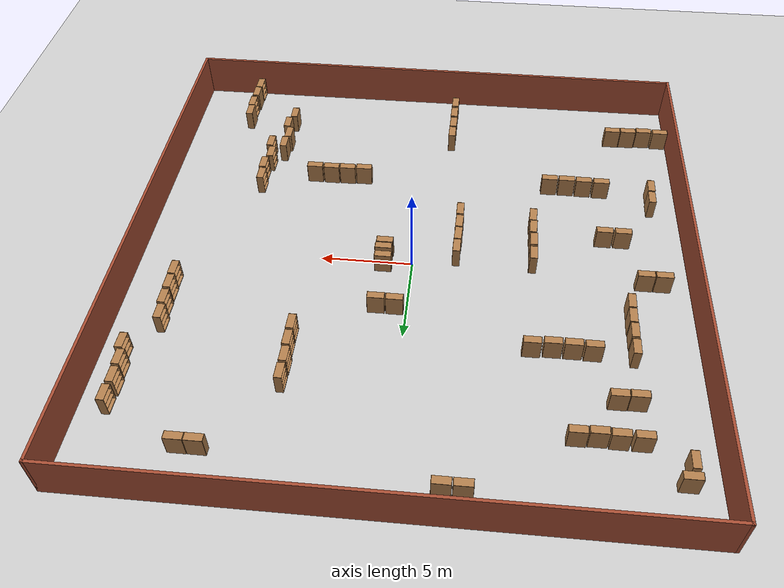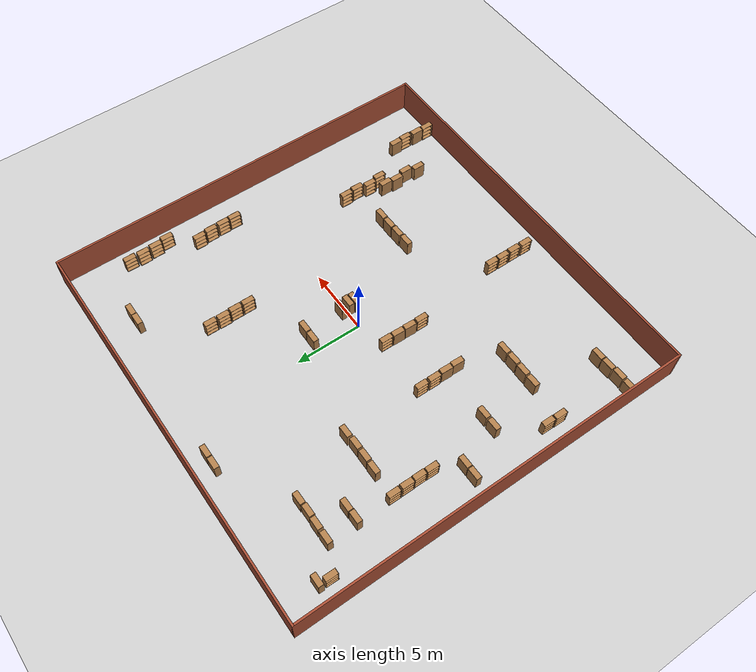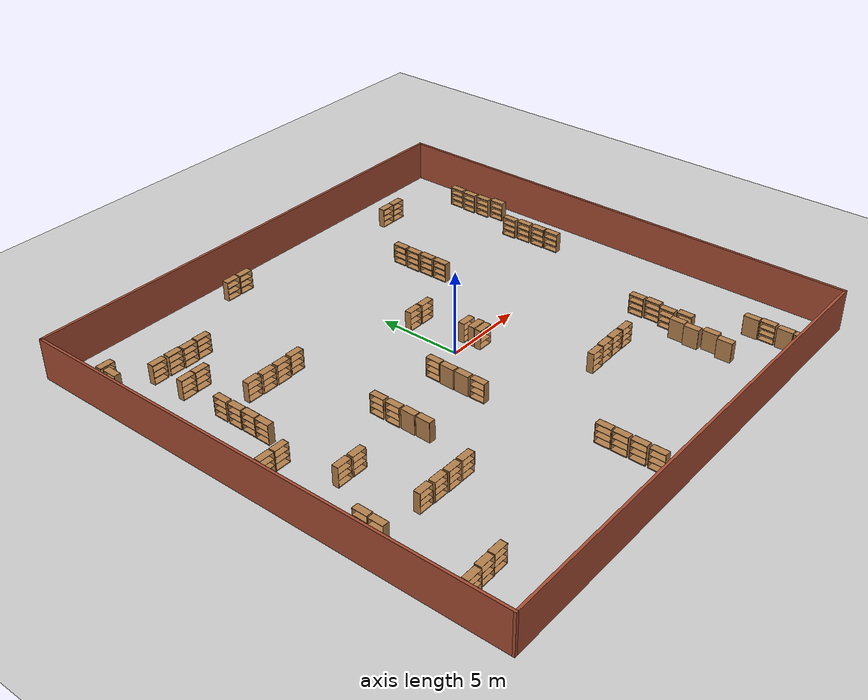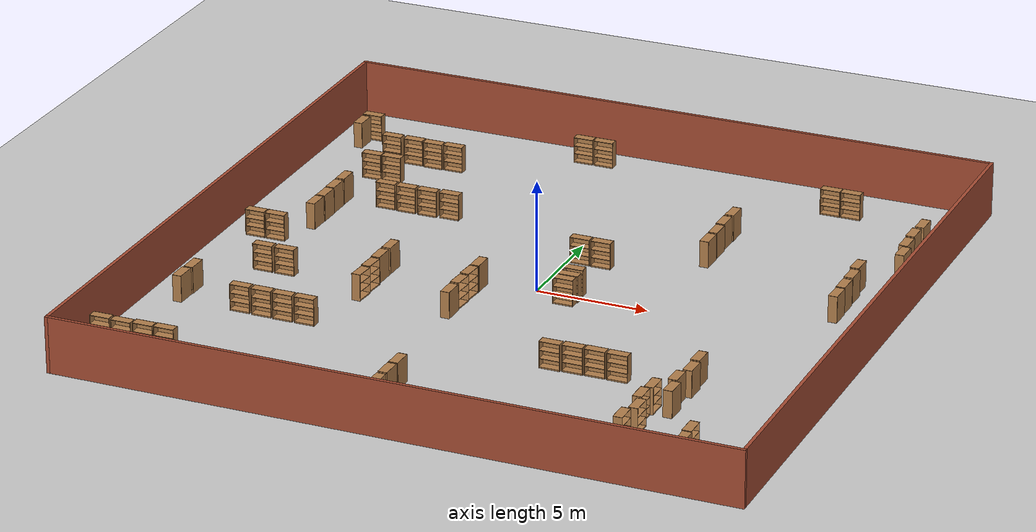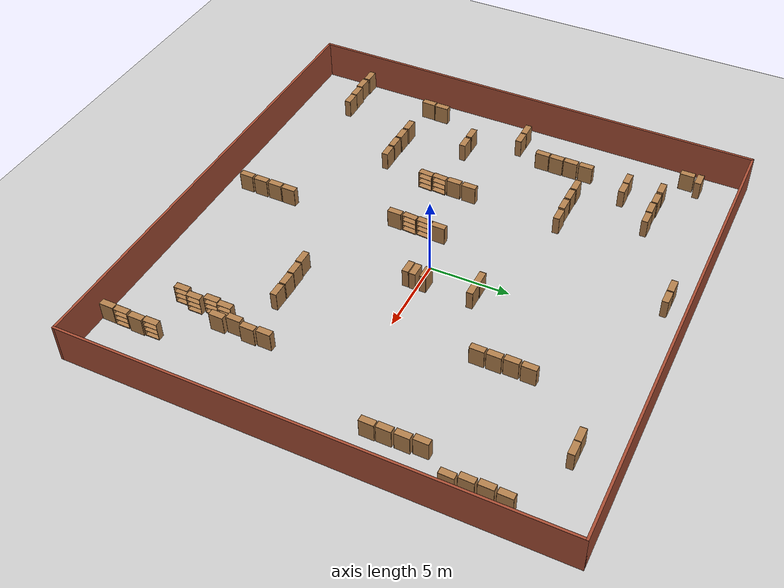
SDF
<sdf version="1.6">
 <world name="default">
  <light name="sun" type="directional">
   <pose>0 0 10 0 -0 0</pose>
   <diffuse>0.8 0.8 0.8 1</diffuse>
   <specular>0.2 0.2 0.2 1</specular>
   <attenuation>
    <range>1000</range>
    <constant>0.9</constant>
    <linear>0.01</linear>
    <quadratic>0.001</quadratic>
   </attenuation>
   <direction>-0.5 0.1 -0.9</direction>
  </light>
  <model name="ground_plane">
   <static>1</static>
   <link name="link">
    <collision name="collision">
     <geometry><plane><normal>0 0 1</normal><size>100 100</size></plane></geometry>
     <surface>
      <contact><collide_bitmask>65535</collide_bitmask></contact>
      <friction><ode><mu>100</mu><mu2>50</mu2></ode></friction>
     </surface>
    </collision>
    <visual name="visual">
     <cast_shadows>0</cast_shadows>
     <geometry><plane><normal>0 0 1</normal><size>100 100</size></plane></geometry>
     <material>
      <script><uri>file://media/materials/scripts/gazebo.material</uri><name>Gazebo/Grey</name></script>
     </material>
    </visual>
   </link>
  </model>
  <gravity>0 0 -9.8</gravity>
  <magnetic_field>6e-06 2.3e-05 -4.2e-05</magnetic_field>
  <atmosphere type="adiabatic"/>
  <physics name="default_physics" default="0" type="ode">
   <max_step_size>0.001</max_step_size>
   <real_time_factor>1</real_time_factor>
   <real_time_update_rate>1000</real_time_update_rate>
  </physics>
  <scene><ambient>0.4 0.4 0.4 1</ambient><background>0.7 0.7 0.7 1</background><shadows>1</shadows></scene>
  <spherical_coordinates>
   <surface_model>EARTH_WGS84</surface_model>
   <latitude_deg>0</latitude_deg>
   <longitude_deg>0</longitude_deg>
   <elevation>0</elevation>
   <heading_deg>0</heading_deg>
  </spherical_coordinates>
  <model name="30x30env"><static>0</static><pose>32.1206 3.39752 0 0 -0 0</pose></model>
  <model name="30x30_0">
   <link name="Wall_0">
    <collision name="Wall_0_Collision">
     <geometry><box><size>30.15 0.15 2.5</size></box></geometry>
     <pose>0 0 1.25 0 -0 0</pose>
    </collision>
    <visual name="Wall_0_Visual">
     <pose>0 0 1.25 0 -0 0</pose>
     <geometry><box><size>30.15 0.15 2.5</size></box></geometry>
     <material>
      <script><uri>file://media/materials/scripts/gazebo.material</uri><name>Gazebo/Bricks</name></script>
      <ambient>1 1 1 1</ambient>
     </material>
     <meta><layer>0</layer></meta>
    </visual>
    <pose>-15 0 0 0 -0 1.5708</pose>
   </link>
   <link name="Wall_1">
    <collision name="Wall_1_Collision">
     <geometry><box><size>30.15 0.15 2.5</size></box></geometry>
     <pose>0 0 1.25 0 -0 0</pose>
    </collision>
    <visual name="Wall_1_Visual">
     <pose>0 0 1.25 0 -0 0</pose>
     <geometry><box><size>30.15 0.15 2.5</size></box></geometry>
     <material>
      <script><uri>file://media/materials/scripts/gazebo.material</uri><name>Gazebo/Bricks</name></script>
      <ambient>1 1 1 1</ambient>
     </material>
     <meta><layer>0</layer></meta>
    </visual>
    <pose>0 15 0 0 -0 0</pose>
   </link>
   <link name="Wall_2">
    <collision name="Wall_2_Collision">
     <geometry><box><size>30.15 0.15 2.5</size></box></geometry>
     <pose>0 0 1.25 0 -0 0</pose>
    </collision>
    <visual name="Wall_2_Visual">
     <pose>0 0 1.25 0 -0 0</pose>
     <geometry><box><size>30.15 0.15 2.5</size></box></geometry>
     <material>
      <script><uri>file://media/materials/scripts/gazebo.material</uri><name>Gazebo/Bricks</name></script>
      <ambient>1 1 1 1</ambient>
     </material>
     <meta><layer>0</layer></meta>
    </visual>
    <pose>15 0 0 0 -0 -1.5708</pose>
   </link>
   <link name="Wall_3">
    <collision name="Wall_3_Collision">
     <geometry><box><size>30.15 0.15 2.5</size></box></geometry>
     <pose>0 0 1.25 0 -0 0</pose>
    </collision>
    <visual name="Wall_3_Visual">
     <pose>0 0 1.25 0 -0 0</pose>
     <geometry><box><size>30.15 0.15 2.5</size></box></geometry>
     <material>
      <script><uri>file://media/materials/scripts/gazebo.material</uri><name>Gazebo/Bricks</name></script>
      <ambient>1 1 1 1</ambient>
     </material>
     <meta><layer>0</layer></meta>
    </visual>
    <pose>0 -15 0 0 -0 3.14159</pose>
   </link>
   <static>1</static>
  </model>
  <audio><device>default</device></audio>
  <model name="bookshelf_clone">
   <static>1</static>
   <link name="link">
    <inertial><mass>1</mass></inertial>
    <collision name="back">
     <pose>0 0.005 0.6 0 -0 0</pose>
     <geometry><box><size>0.9 0.01 1.2</size></box></geometry>
    </collision>
    <visual name="visual1">
     <pose>0 0.005 0.6 0 -0 0</pose>
     <geometry><box><size>0.9 0.01 1.2</size></box></geometry>
     <material>
      <script><uri>file://media/materials/scripts/gazebo.material</uri><name>Gazebo/Wood</name></script>
     </material>
    </visual>
    <collision name="left_side">
     <pose>0.45 -0.195 0.6 0 -0 0</pose>
     <geometry><box><size>0.02 0.4 1.2</size></box></geometry>
    </collision>
    <visual name="visual2">
     <pose>0.45 -0.195 0.6 0 -0 0</pose>
     <geometry><box><size>0.02 0.4 1.2</size></box></geometry>
     <material>
      <script><uri>file://media/materials/scripts/gazebo.material</uri><name>Gazebo/Wood</name></script>
     </material>
    </visual>
    <collision name="right_side">
     <pose>-0.45 -0.195 0.6 0 -0 0</pose>
     <geometry><box><size>0.02 0.4 1.2</size></box></geometry>
    </collision>
    <visual name="visual3">
     <pose>-0.45 -0.195 0.6 0 -0 0</pose>
     <geometry><box><size>0.02 0.4 1.2</size></box></geometry>
     <material>
      <script><uri>file://media/materials/scripts/gazebo.material</uri><name>Gazebo/Wood</name></script>
     </material>
    </visual>
    <collision name="bottom">
     <pose>0 -0.195 0.03 0 -0 0</pose>
     <geometry><box><size>0.88 0.4 0.06</size></box></geometry>
    </collision>
    <visual name="visual4">
     <pose>0 -0.195 0.03 0 -0 0</pose>
     <geometry><box><size>0.88 0.4 0.06</size></box></geometry>
     <material>
      <script><uri>file://media/materials/scripts/gazebo.material</uri><name>Gazebo/Wood</name></script>
     </material>
    </visual>
    <collision name="top">
     <pose>0 -0.195 1.19 0 -0 0</pose>
     <geometry><box><size>0.88 0.4 0.02</size></box></geometry>
    </collision>
    <visual name="visual5">
     <pose>0 -0.195 1.19 0 -0 0</pose>
     <geometry><box><size>0.88 0.4 0.02</size></box></geometry>
     <material>
      <script><uri>file://media/materials/scripts/gazebo.material</uri><name>Gazebo/Wood</name></script>
     </material>
    </visual>
    <collision name="low_shelf">
     <pose>0 -0.195 0.43 0 -0 0</pose>
     <geometry><box><size>0.88 0.4 0.02</size></box></geometry>
    </collision>
    <visual name="visual6">
     <pose>0 -0.195 0.43 0 -0 0</pose>
     <geometry><box><size>0.88 0.4 0.02</size></box></geometry>
     <material>
      <script><uri>file://media/materials/scripts/gazebo.material</uri><name>Gazebo/Wood</name></script>
     </material>
    </visual>
    <collision name="high_shelf">
     <pose>0 -0.195 0.8 0 -0 0</pose>
     <geometry><box><size>0.88 0.4 0.02</size></box></geometry>
    </collision>
    <visual name="visual7">
     <pose>0 -0.195 0.8 0 -0 0</pose>
     <geometry><box><size>0.88 0.4 0.02</size></box></geometry>
     <material>
      <script><uri>file://media/materials/scripts/gazebo.material</uri><name>Gazebo/Wood</name></script>
     </material>
    </visual>
   </link>
   <pose>-11.4672 8.45136 0 0 -0 0</pose>
  </model>
  <model name="bookshelf_clone_clone">
   <static>1</static>
   <link name="link">
    <inertial><mass>1</mass></inertial>
    <collision name="back">
     <pose>0 0.005 0.6 0 -0 0</pose>
     <geometry><box><size>0.9 0.01 1.2</size></box></geometry>
    </collision>
    <visual name="visual1">
     <pose>0 0.005 0.6 0 -0 0</pose>
     <geometry><box><size>0.9 0.01 1.2</size></box></geometry>
     <material>
      <script><uri>file://media/materials/scripts/gazebo.material</uri><name>Gazebo/Wood</name></script>
     </material>
    </visual>
    <collision name="left_side">
     <pose>0.45 -0.195 0.6 0 -0 0</pose>
     <geometry><box><size>0.02 0.4 1.2</size></box></geometry>
    </collision>
    <visual name="visual2">
     <pose>0.45 -0.195 0.6 0 -0 0</pose>
     <geometry><box><size>0.02 0.4 1.2</size></box></geometry>
     <material>
      <script><uri>file://media/materials/scripts/gazebo.material</uri><name>Gazebo/Wood</name></script>
     </material>
    </visual>
    <collision name="right_side">
     <pose>-0.45 -0.195 0.6 0 -0 0</pose>
     <geometry><box><size>0.02 0.4 1.2</size></box></geometry>
    </collision>
    <visual name="visual3">
     <pose>-0.45 -0.195 0.6 0 -0 0</pose>
     <geometry><box><size>0.02 0.4 1.2</size></box></geometry>
     <material>
      <script><uri>file://media/materials/scripts/gazebo.material</uri><name>Gazebo/Wood</name></script>
     </material>
    </visual>
    <collision name="bottom">
     <pose>0 -0.195 0.03 0 -0 0</pose>
     <geometry><box><size>0.88 0.4 0.06</size></box></geometry>
    </collision>
    <visual name="visual4">
     <pose>0 -0.195 0.03 0 -0 0</pose>
     <geometry><box><size>0.88 0.4 0.06</size></box></geometry>
     <material>
      <script><uri>file://media/materials/scripts/gazebo.material</uri><name>Gazebo/Wood</name></script>
     </material>
    </visual>
    <collision name="top">
     <pose>0 -0.195 1.19 0 -0 0</pose>
     <geometry><box><size>0.88 0.4 0.02</size></box></geometry>
    </collision>
    <visual name="visual5">
     <pose>0 -0.195 1.19 0 -0 0</pose>
     <geometry><box><size>0.88 0.4 0.02</size></box></geometry>
     <material>
      <script><uri>file://media/materials/scripts/gazebo.material</uri><name>Gazebo/Wood</name></script>
     </material>
    </visual>
    <collision name="low_shelf">
     <pose>0 -0.195 0.43 0 -0 0</pose>
     <geometry><box><size>0.88 0.4 0.02</size></box></geometry>
    </collision>
    <visual name="visual6">
     <pose>0 -0.195 0.43 0 -0 0</pose>
     <geometry><box><size>0.88 0.4 0.02</size></box></geometry>
     <material>
      <script><uri>file://media/materials/scripts/gazebo.material</uri><name>Gazebo/Wood</name></script>
     </material>
    </visual>
    <collision name="high_shelf">
     <pose>0 -0.195 0.8 0 -0 0</pose>
     <geometry><box><size>0.88 0.4 0.02</size></box></geometry>
    </collision>
    <visual name="visual7">
     <pose>0 -0.195 0.8 0 -0 0</pose>
     <geometry><box><size>0.88 0.4 0.02</size></box></geometry>
     <material>
      <script><uri>file://media/materials/scripts/gazebo.material</uri><name>Gazebo/Wood</name></script>
     </material>
    </visual>
   </link>
   <pose>-10.5181 8.47539 0 0 -0 0</pose>
  </model>
  <model name="bookshelf_clone_0">
   <static>1</static>
   <link name="link">
    <inertial><mass>1</mass></inertial>
    <collision name="back">
     <pose>0 0.005 0.6 0 -0 0</pose>
     <geometry><box><size>0.9 0.01 1.2</size></box></geometry>
    </collision>
    <visual name="visual1">
     <pose>0 0.005 0.6 0 -0 0</pose>
     <geometry><box><size>0.9 0.01 1.2</size></box></geometry>
     <material>
      <script><uri>file://media/materials/scripts/gazebo.material</uri><name>Gazebo/Wood</name></script>
     </material>
    </visual>
    <collision name="left_side">
     <pose>0.45 -0.195 0.6 0 -0 0</pose>
     <geometry><box><size>0.02 0.4 1.2</size></box></geometry>
    </collision>
    <visual name="visual2">
     <pose>0.45 -0.195 0.6 0 -0 0</pose>
     <geometry><box><size>0.02 0.4 1.2</size></box></geometry>
     <material>
      <script><uri>file://media/materials/scripts/gazebo.material</uri><name>Gazebo/Wood</name></script>
     </material>
    </visual>
    <collision name="right_side">
     <pose>-0.45 -0.195 0.6 0 -0 0</pose>
     <geometry><box><size>0.02 0.4 1.2</size></box></geometry>
    </collision>
    <visual name="visual3">
     <pose>-0.45 -0.195 0.6 0 -0 0</pose>
     <geometry><box><size>0.02 0.4 1.2</size></box></geometry>
     <material>
      <script><uri>file://media/materials/scripts/gazebo.material</uri><name>Gazebo/Wood</name></script>
     </material>
    </visual>
    <collision name="bottom">
     <pose>0 -0.195 0.03 0 -0 0</pose>
     <geometry><box><size>0.88 0.4 0.06</size></box></geometry>
    </collision>
    <visual name="visual4">
     <pose>0 -0.195 0.03 0 -0 0</pose>
     <geometry><box><size>0.88 0.4 0.06</size></box></geometry>
     <material>
      <script><uri>file://media/materials/scripts/gazebo.material</uri><name>Gazebo/Wood</name></script>
     </material>
    </visual>
    <collision name="top">
     <pose>0 -0.195 1.19 0 -0 0</pose>
     <geometry><box><size>0.88 0.4 0.02</size></box></geometry>
    </collision>
    <visual name="visual5">
     <pose>0 -0.195 1.19 0 -0 0</pose>
     <geometry><box><size>0.88 0.4 0.02</size></box></geometry>
     <material>
      <script><uri>file://media/materials/scripts/gazebo.material</uri><name>Gazebo/Wood</name></script>
     </material>
    </visual>
    <collision name="low_shelf">
     <pose>0 -0.195 0.43 0 -0 0</pose>
     <geometry><box><size>0.88 0.4 0.02</size></box></geometry>
    </collision>
    <visual name="visual6">
     <pose>0 -0.195 0.43 0 -0 0</pose>
     <geometry><box><size>0.88 0.4 0.02</size></box></geometry>
     <material>
      <script><uri>file://media/materials/scripts/gazebo.material</uri><name>Gazebo/Wood</name></script>
     </material>
    </visual>
    <collision name="high_shelf">
     <pose>0 -0.195 0.8 0 -0 0</pose>
     <geometry><box><size>0.88 0.4 0.02</size></box></geometry>
    </collision>
    <visual name="visual7">
     <pose>0 -0.195 0.8 0 -0 0</pose>
     <geometry><box><size>0.88 0.4 0.02</size></box></geometry>
     <material>
      <script><uri>file://media/materials/scripts/gazebo.material</uri><name>Gazebo/Wood</name></script>
     </material>
    </visual>
   </link>
   <pose>-13.3299 12.5056 0 0 -0 0</pose>
  </model>
  <model name="bookshelf_clone_0_clone">
   <static>1</static>
   <link name="link">
    <inertial><mass>1</mass></inertial>
    <collision name="back">
     <pose>0 0.005 0.6 0 -0 0</pose>
     <geometry><box><size>0.9 0.01 1.2</size></box></geometry>
    </collision>
    <visual name="visual1">
     <pose>0 0.005 0.6 0 -0 0</pose>
     <geometry><box><size>0.9 0.01 1.2</size></box></geometry>
     <material>
      <script><uri>file://media/materials/scripts/gazebo.material</uri><name>Gazebo/Wood</name></script>
     </material>
    </visual>
    <collision name="left_side">
     <pose>0.45 -0.195 0.6 0 -0 0</pose>
     <geometry><box><size>0.02 0.4 1.2</size></box></geometry>
    </collision>
    <visual name="visual2">
     <pose>0.45 -0.195 0.6 0 -0 0</pose>
     <geometry><box><size>0.02 0.4 1.2</size></box></geometry>
     <material>
      <script><uri>file://media/materials/scripts/gazebo.material</uri><name>Gazebo/Wood</name></script>
     </material>
    </visual>
    <collision name="right_side">
     <pose>-0.45 -0.195 0.6 0 -0 0</pose>
     <geometry><box><size>0.02 0.4 1.2</size></box></geometry>
    </collision>
    <visual name="visual3">
     <pose>-0.45 -0.195 0.6 0 -0 0</pose>
     <geometry><box><size>0.02 0.4 1.2</size></box></geometry>
     <material>
      <script><uri>file://media/materials/scripts/gazebo.material</uri><name>Gazebo/Wood</name></script>
     </material>
    </visual>
    <collision name="bottom">
     <pose>0 -0.195 0.03 0 -0 0</pose>
     <geometry><box><size>0.88 0.4 0.06</size></box></geometry>
    </collision>
    <visual name="visual4">
     <pose>0 -0.195 0.03 0 -0 0</pose>
     <geometry><box><size>0.88 0.4 0.06</size></box></geometry>
     <material>
      <script><uri>file://media/materials/scripts/gazebo.material</uri><name>Gazebo/Wood</name></script>
     </material>
    </visual>
    <collision name="top">
     <pose>0 -0.195 1.19 0 -0 0</pose>
     <geometry><box><size>0.88 0.4 0.02</size></box></geometry>
    </collision>
    <visual name="visual5">
     <pose>0 -0.195 1.19 0 -0 0</pose>
     <geometry><box><size>0.88 0.4 0.02</size></box></geometry>
     <material>
      <script><uri>file://media/materials/scripts/gazebo.material</uri><name>Gazebo/Wood</name></script>
     </material>
    </visual>
    <collision name="low_shelf">
     <pose>0 -0.195 0.43 0 -0 0</pose>
     <geometry><box><size>0.88 0.4 0.02</size></box></geometry>
    </collision>
    <visual name="visual6">
     <pose>0 -0.195 0.43 0 -0 0</pose>
     <geometry><box><size>0.88 0.4 0.02</size></box></geometry>
     <material>
      <script><uri>file://media/materials/scripts/gazebo.material</uri><name>Gazebo/Wood</name></script>
     </material>
    </visual>
    <collision name="high_shelf">
     <pose>0 -0.195 0.8 0 -0 0</pose>
     <geometry><box><size>0.88 0.4 0.02</size></box></geometry>
    </collision>
    <visual name="visual7">
     <pose>0 -0.195 0.8 0 -0 0</pose>
     <geometry><box><size>0.88 0.4 0.02</size></box></geometry>
     <material>
      <script><uri>file://media/materials/scripts/gazebo.material</uri><name>Gazebo/Wood</name></script>
     </material>
    </visual>
   </link>
   <pose>-13.352 11.5068 0 0 0 -1.58271</pose>
  </model>
  <model name="bookshelf_clone_clone_clone">
   <static>1</static>
   <link name="link">
    <inertial><mass>1</mass></inertial>
    <collision name="back">
     <pose>0 0.005 0.6 0 -0 0</pose>
     <geometry><box><size>0.9 0.01 1.2</size></box></geometry>
    </collision>
    <visual name="visual1">
     <pose>0 0.005 0.6 0 -0 0</pose>
     <geometry><box><size>0.9 0.01 1.2</size></box></geometry>
     <material>
      <script><uri>file://media/materials/scripts/gazebo.material</uri><name>Gazebo/Wood</name></script>
     </material>
    </visual>
    <collision name="left_side">
     <pose>0.45 -0.195 0.6 0 -0 0</pose>
     <geometry><box><size>0.02 0.4 1.2</size></box></geometry>
    </collision>
    <visual name="visual2">
     <pose>0.45 -0.195 0.6 0 -0 0</pose>
     <geometry><box><size>0.02 0.4 1.2</size></box></geometry>
     <material>
      <script><uri>file://media/materials/scripts/gazebo.material</uri><name>Gazebo/Wood</name></script>
     </material>
    </visual>
    <collision name="right_side">
     <pose>-0.45 -0.195 0.6 0 -0 0</pose>
     <geometry><box><size>0.02 0.4 1.2</size></box></geometry>
    </collision>
    <visual name="visual3">
     <pose>-0.45 -0.195 0.6 0 -0 0</pose>
     <geometry><box><size>0.02 0.4 1.2</size></box></geometry>
     <material>
      <script><uri>file://media/materials/scripts/gazebo.material</uri><name>Gazebo/Wood</name></script>
     </material>
    </visual>
    <collision name="bottom">
     <pose>0 -0.195 0.03 0 -0 0</pose>
     <geometry><box><size>0.88 0.4 0.06</size></box></geometry>
    </collision>
    <visual name="visual4">
     <pose>0 -0.195 0.03 0 -0 0</pose>
     <geometry><box><size>0.88 0.4 0.06</size></box></geometry>
     <material>
      <script><uri>file://media/materials/scripts/gazebo.material</uri><name>Gazebo/Wood</name></script>
     </material>
    </visual>
    <collision name="top">
     <pose>0 -0.195 1.19 0 -0 0</pose>
     <geometry><box><size>0.88 0.4 0.02</size></box></geometry>
    </collision>
    <visual name="visual5">
     <pose>0 -0.195 1.19 0 -0 0</pose>
     <geometry><box><size>0.88 0.4 0.02</size></box></geometry>
     <material>
      <script><uri>file://media/materials/scripts/gazebo.material</uri><name>Gazebo/Wood</name></script>
     </material>
    </visual>
    <collision name="low_shelf">
     <pose>0 -0.195 0.43 0 -0 0</pose>
     <geometry><box><size>0.88 0.4 0.02</size></box></geometry>
    </collision>
    <visual name="visual6">
     <pose>0 -0.195 0.43 0 -0 0</pose>
     <geometry><box><size>0.88 0.4 0.02</size></box></geometry>
     <material>
      <script><uri>file://media/materials/scripts/gazebo.material</uri><name>Gazebo/Wood</name></script>
     </material>
    </visual>
    <collision name="high_shelf">
     <pose>0 -0.195 0.8 0 -0 0</pose>
     <geometry><box><size>0.88 0.4 0.02</size></box></geometry>
    </collision>
    <visual name="visual7">
     <pose>0 -0.195 0.8 0 -0 0</pose>
     <geometry><box><size>0.88 0.4 0.02</size></box></geometry>
     <material>
      <script><uri>file://media/materials/scripts/gazebo.material</uri><name>Gazebo/Wood</name></script>
     </material>
    </visual>
   </link>
   <pose>-3.50081 13.74 0 0 -0 0</pose>
  </model>
  <model name="bookshelf_clone_clone_clone_0">
   <static>1</static>
   <link name="link">
    <inertial><mass>1</mass></inertial>
    <collision name="back">
     <pose>0 0.005 0.6 0 -0 0</pose>
     <geometry><box><size>0.9 0.01 1.2</size></box></geometry>
    </collision>
    <visual name="visual1">
     <pose>0 0.005 0.6 0 -0 0</pose>
     <geometry><box><size>0.9 0.01 1.2</size></box></geometry>
     <material>
      <script><uri>file://media/materials/scripts/gazebo.material</uri><name>Gazebo/Wood</name></script>
     </material>
    </visual>
    <collision name="left_side">
     <pose>0.45 -0.195 0.6 0 -0 0</pose>
     <geometry><box><size>0.02 0.4 1.2</size></box></geometry>
    </collision>
    <visual name="visual2">
     <pose>0.45 -0.195 0.6 0 -0 0</pose>
     <geometry><box><size>0.02 0.4 1.2</size></box></geometry>
     <material>
      <script><uri>file://media/materials/scripts/gazebo.material</uri><name>Gazebo/Wood</name></script>
     </material>
    </visual>
    <collision name="right_side">
     <pose>-0.45 -0.195 0.6 0 -0 0</pose>
     <geometry><box><size>0.02 0.4 1.2</size></box></geometry>
    </collision>
    <visual name="visual3">
     <pose>-0.45 -0.195 0.6 0 -0 0</pose>
     <geometry><box><size>0.02 0.4 1.2</size></box></geometry>
     <material>
      <script><uri>file://media/materials/scripts/gazebo.material</uri><name>Gazebo/Wood</name></script>
     </material>
    </visual>
    <collision name="bottom">
     <pose>0 -0.195 0.03 0 -0 0</pose>
     <geometry><box><size>0.88 0.4 0.06</size></box></geometry>
    </collision>
    <visual name="visual4">
     <pose>0 -0.195 0.03 0 -0 0</pose>
     <geometry><box><size>0.88 0.4 0.06</size></box></geometry>
     <material>
      <script><uri>file://media/materials/scripts/gazebo.material</uri><name>Gazebo/Wood</name></script>
     </material>
    </visual>
    <collision name="top">
     <pose>0 -0.195 1.19 0 -0 0</pose>
     <geometry><box><size>0.88 0.4 0.02</size></box></geometry>
    </collision>
    <visual name="visual5">
     <pose>0 -0.195 1.19 0 -0 0</pose>
     <geometry><box><size>0.88 0.4 0.02</size></box></geometry>
     <material>
      <script><uri>file://media/materials/scripts/gazebo.material</uri><name>Gazebo/Wood</name></script>
     </material>
    </visual>
    <collision name="low_shelf">
     <pose>0 -0.195 0.43 0 -0 0</pose>
     <geometry><box><size>0.88 0.4 0.02</size></box></geometry>
    </collision>
    <visual name="visual6">
     <pose>0 -0.195 0.43 0 -0 0</pose>
     <geometry><box><size>0.88 0.4 0.02</size></box></geometry>
     <material>
      <script><uri>file://media/materials/scripts/gazebo.material</uri><name>Gazebo/Wood</name></script>
     </material>
    </visual>
    <collision name="high_shelf">
     <pose>0 -0.195 0.8 0 -0 0</pose>
     <geometry><box><size>0.88 0.4 0.02</size></box></geometry>
    </collision>
    <visual name="visual7">
     <pose>0 -0.195 0.8 0 -0 0</pose>
     <geometry><box><size>0.88 0.4 0.02</size></box></geometry>
     <material>
      <script><uri>file://media/materials/scripts/gazebo.material</uri><name>Gazebo/Wood</name></script>
     </material>
    </visual>
   </link>
   <pose>-2.53899 13.7368 0 0 -0 0</pose>
  </model>
  <model name="bookshelf_clone_clone_clone_0_clone_clone">
   <static>1</static>
   <link name="link">
    <inertial><mass>1</mass></inertial>
    <collision name="back">
     <pose>0 0.005 0.6 0 -0 0</pose>
     <geometry><box><size>0.9 0.01 1.2</size></box></geometry>
    </collision>
    <visual name="visual1">
     <pose>0 0.005 0.6 0 -0 0</pose>
     <geometry><box><size>0.9 0.01 1.2</size></box></geometry>
     <material>
      <script><uri>file://media/materials/scripts/gazebo.material</uri><name>Gazebo/Wood</name></script>
     </material>
    </visual>
    <collision name="left_side">
     <pose>0.45 -0.195 0.6 0 -0 0</pose>
     <geometry><box><size>0.02 0.4 1.2</size></box></geometry>
    </collision>
    <visual name="visual2">
     <pose>0.45 -0.195 0.6 0 -0 0</pose>
     <geometry><box><size>0.02 0.4 1.2</size></box></geometry>
     <material>
      <script><uri>file://media/materials/scripts/gazebo.material</uri><name>Gazebo/Wood</name></script>
     </material>
    </visual>
    <collision name="right_side">
     <pose>-0.45 -0.195 0.6 0 -0 0</pose>
     <geometry><box><size>0.02 0.4 1.2</size></box></geometry>
    </collision>
    <visual name="visual3">
     <pose>-0.45 -0.195 0.6 0 -0 0</pose>
     <geometry><box><size>0.02 0.4 1.2</size></box></geometry>
     <material>
      <script><uri>file://media/materials/scripts/gazebo.material</uri><name>Gazebo/Wood</name></script>
     </material>
    </visual>
    <collision name="bottom">
     <pose>0 -0.195 0.03 0 -0 0</pose>
     <geometry><box><size>0.88 0.4 0.06</size></box></geometry>
    </collision>
    <visual name="visual4">
     <pose>0 -0.195 0.03 0 -0 0</pose>
     <geometry><box><size>0.88 0.4 0.06</size></box></geometry>
     <material>
      <script><uri>file://media/materials/scripts/gazebo.material</uri><name>Gazebo/Wood</name></script>
     </material>
    </visual>
    <collision name="top">
     <pose>0 -0.195 1.19 0 -0 0</pose>
     <geometry><box><size>0.88 0.4 0.02</size></box></geometry>
    </collision>
    <visual name="visual5">
     <pose>0 -0.195 1.19 0 -0 0</pose>
     <geometry><box><size>0.88 0.4 0.02</size></box></geometry>
     <material>
      <script><uri>file://media/materials/scripts/gazebo.material</uri><name>Gazebo/Wood</name></script>
     </material>
    </visual>
    <collision name="low_shelf">
     <pose>0 -0.195 0.43 0 -0 0</pose>
     <geometry><box><size>0.88 0.4 0.02</size></box></geometry>
    </collision>
    <visual name="visual6">
     <pose>0 -0.195 0.43 0 -0 0</pose>
     <geometry><box><size>0.88 0.4 0.02</size></box></geometry>
     <material>
      <script><uri>file://media/materials/scripts/gazebo.material</uri><name>Gazebo/Wood</name></script>
     </material>
    </visual>
    <collision name="high_shelf">
     <pose>0 -0.195 0.8 0 -0 0</pose>
     <geometry><box><size>0.88 0.4 0.02</size></box></geometry>
    </collision>
    <visual name="visual7">
     <pose>0 -0.195 0.8 0 -0 0</pose>
     <geometry><box><size>0.88 0.4 0.02</size></box></geometry>
     <material>
      <script><uri>file://media/materials/scripts/gazebo.material</uri><name>Gazebo/Wood</name></script>
     </material>
    </visual>
   </link>
   <pose>8.60542 12.6452 0 0 -0 0</pose>
  </model>
  <model name="bookshelf_clone_clone_clone_0_clone_clone_0">
   <static>1</static>
   <link name="link">
    <inertial><mass>1</mass></inertial>
    <collision name="back">
     <pose>0 0.005 0.6 0 -0 0</pose>
     <geometry><box><size>0.9 0.01 1.2</size></box></geometry>
    </collision>
    <visual name="visual1">
     <pose>0 0.005 0.6 0 -0 0</pose>
     <geometry><box><size>0.9 0.01 1.2</size></box></geometry>
     <material>
      <script><uri>file://media/materials/scripts/gazebo.material</uri><name>Gazebo/Wood</name></script>
     </material>
    </visual>
    <collision name="left_side">
     <pose>0.45 -0.195 0.6 0 -0 0</pose>
     <geometry><box><size>0.02 0.4 1.2</size></box></geometry>
    </collision>
    <visual name="visual2">
     <pose>0.45 -0.195 0.6 0 -0 0</pose>
     <geometry><box><size>0.02 0.4 1.2</size></box></geometry>
     <material>
      <script><uri>file://media/materials/scripts/gazebo.material</uri><name>Gazebo/Wood</name></script>
     </material>
    </visual>
    <collision name="right_side">
     <pose>-0.45 -0.195 0.6 0 -0 0</pose>
     <geometry><box><size>0.02 0.4 1.2</size></box></geometry>
    </collision>
    <visual name="visual3">
     <pose>-0.45 -0.195 0.6 0 -0 0</pose>
     <geometry><box><size>0.02 0.4 1.2</size></box></geometry>
     <material>
      <script><uri>file://media/materials/scripts/gazebo.material</uri><name>Gazebo/Wood</name></script>
     </material>
    </visual>
    <collision name="bottom">
     <pose>0 -0.195 0.03 0 -0 0</pose>
     <geometry><box><size>0.88 0.4 0.06</size></box></geometry>
    </collision>
    <visual name="visual4">
     <pose>0 -0.195 0.03 0 -0 0</pose>
     <geometry><box><size>0.88 0.4 0.06</size></box></geometry>
     <material>
      <script><uri>file://media/materials/scripts/gazebo.material</uri><name>Gazebo/Wood</name></script>
     </material>
    </visual>
    <collision name="top">
     <pose>0 -0.195 1.19 0 -0 0</pose>
     <geometry><box><size>0.88 0.4 0.02</size></box></geometry>
    </collision>
    <visual name="visual5">
     <pose>0 -0.195 1.19 0 -0 0</pose>
     <geometry><box><size>0.88 0.4 0.02</size></box></geometry>
     <material>
      <script><uri>file://media/materials/scripts/gazebo.material</uri><name>Gazebo/Wood</name></script>
     </material>
    </visual>
    <collision name="low_shelf">
     <pose>0 -0.195 0.43 0 -0 0</pose>
     <geometry><box><size>0.88 0.4 0.02</size></box></geometry>
    </collision>
    <visual name="visual6">
     <pose>0 -0.195 0.43 0 -0 0</pose>
     <geometry><box><size>0.88 0.4 0.02</size></box></geometry>
     <material>
      <script><uri>file://media/materials/scripts/gazebo.material</uri><name>Gazebo/Wood</name></script>
     </material>
    </visual>
    <collision name="high_shelf">
     <pose>0 -0.195 0.8 0 -0 0</pose>
     <geometry><box><size>0.88 0.4 0.02</size></box></geometry>
    </collision>
    <visual name="visual7">
     <pose>0 -0.195 0.8 0 -0 0</pose>
     <geometry><box><size>0.88 0.4 0.02</size></box></geometry>
     <material>
      <script><uri>file://media/materials/scripts/gazebo.material</uri><name>Gazebo/Wood</name></script>
     </material>
    </visual>
   </link>
   <pose>9.53734 12.6485 0 0 -0 0</pose>
  </model>
  <model name="bookshelf_clone_0_clone_clone">
   <static>1</static>
   <link name="link">
    <inertial><mass>1</mass></inertial>
    <collision name="back">
     <pose>0 0.005 0.6 0 -0 0</pose>
     <geometry><box><size>0.9 0.01 1.2</size></box></geometry>
    </collision>
    <visual name="visual1">
     <pose>0 0.005 0.6 0 -0 0</pose>
     <geometry><box><size>0.9 0.01 1.2</size></box></geometry>
     <material>
      <script><uri>file://media/materials/scripts/gazebo.material</uri><name>Gazebo/Wood</name></script>
     </material>
    </visual>
    <collision name="left_side">
     <pose>0.45 -0.195 0.6 0 -0 0</pose>
     <geometry><box><size>0.02 0.4 1.2</size></box></geometry>
    </collision>
    <visual name="visual2">
     <pose>0.45 -0.195 0.6 0 -0 0</pose>
     <geometry><box><size>0.02 0.4 1.2</size></box></geometry>
     <material>
      <script><uri>file://media/materials/scripts/gazebo.material</uri><name>Gazebo/Wood</name></script>
     </material>
    </visual>
    <collision name="right_side">
     <pose>-0.45 -0.195 0.6 0 -0 0</pose>
     <geometry><box><size>0.02 0.4 1.2</size></box></geometry>
    </collision>
    <visual name="visual3">
     <pose>-0.45 -0.195 0.6 0 -0 0</pose>
     <geometry><box><size>0.02 0.4 1.2</size></box></geometry>
     <material>
      <script><uri>file://media/materials/scripts/gazebo.material</uri><name>Gazebo/Wood</name></script>
     </material>
    </visual>
    <collision name="bottom">
     <pose>0 -0.195 0.03 0 -0 0</pose>
     <geometry><box><size>0.88 0.4 0.06</size></box></geometry>
    </collision>
    <visual name="visual4">
     <pose>0 -0.195 0.03 0 -0 0</pose>
     <geometry><box><size>0.88 0.4 0.06</size></box></geometry>
     <material>
      <script><uri>file://media/materials/scripts/gazebo.material</uri><name>Gazebo/Wood</name></script>
     </material>
    </visual>
    <collision name="top">
     <pose>0 -0.195 1.19 0 -0 0</pose>
     <geometry><box><size>0.88 0.4 0.02</size></box></geometry>
    </collision>
    <visual name="visual5">
     <pose>0 -0.195 1.19 0 -0 0</pose>
     <geometry><box><size>0.88 0.4 0.02</size></box></geometry>
     <material>
      <script><uri>file://media/materials/scripts/gazebo.material</uri><name>Gazebo/Wood</name></script>
     </material>
    </visual>
    <collision name="low_shelf">
     <pose>0 -0.195 0.43 0 -0 0</pose>
     <geometry><box><size>0.88 0.4 0.02</size></box></geometry>
    </collision>
    <visual name="visual6">
     <pose>0 -0.195 0.43 0 -0 0</pose>
     <geometry><box><size>0.88 0.4 0.02</size></box></geometry>
     <material>
      <script><uri>file://media/materials/scripts/gazebo.material</uri><name>Gazebo/Wood</name></script>
     </material>
    </visual>
    <collision name="high_shelf">
     <pose>0 -0.195 0.8 0 -0 0</pose>
     <geometry><box><size>0.88 0.4 0.02</size></box></geometry>
    </collision>
    <visual name="visual7">
     <pose>0 -0.195 0.8 0 -0 0</pose>
     <geometry><box><size>0.88 0.4 0.02</size></box></geometry>
     <material>
      <script><uri>file://media/materials/scripts/gazebo.material</uri><name>Gazebo/Wood</name></script>
     </material>
    </visual>
   </link>
   <pose>-13.1951 -6.44439 0 0 0 -1.58271</pose>
  </model>
  <model name="bookshelf_clone_0_clone_clone_0">
   <static>1</static>
   <link name="link">
    <inertial><mass>1</mass></inertial>
    <collision name="back">
     <pose>0 0.005 0.6 0 -0 0</pose>
     <geometry><box><size>0.9 0.01 1.2</size></box></geometry>
    </collision>
    <visual name="visual1">
     <pose>0 0.005 0.6 0 -0 0</pose>
     <geometry><box><size>0.9 0.01 1.2</size></box></geometry>
     <material>
      <script><uri>file://media/materials/scripts/gazebo.material</uri><name>Gazebo/Wood</name></script>
     </material>
    </visual>
    <collision name="left_side">
     <pose>0.45 -0.195 0.6 0 -0 0</pose>
     <geometry><box><size>0.02 0.4 1.2</size></box></geometry>
    </collision>
    <visual name="visual2">
     <pose>0.45 -0.195 0.6 0 -0 0</pose>
     <geometry><box><size>0.02 0.4 1.2</size></box></geometry>
     <material>
      <script><uri>file://media/materials/scripts/gazebo.material</uri><name>Gazebo/Wood</name></script>
     </material>
    </visual>
    <collision name="right_side">
     <pose>-0.45 -0.195 0.6 0 -0 0</pose>
     <geometry><box><size>0.02 0.4 1.2</size></box></geometry>
    </collision>
    <visual name="visual3">
     <pose>-0.45 -0.195 0.6 0 -0 0</pose>
     <geometry><box><size>0.02 0.4 1.2</size></box></geometry>
     <material>
      <script><uri>file://media/materials/scripts/gazebo.material</uri><name>Gazebo/Wood</name></script>
     </material>
    </visual>
    <collision name="bottom">
     <pose>0 -0.195 0.03 0 -0 0</pose>
     <geometry><box><size>0.88 0.4 0.06</size></box></geometry>
    </collision>
    <visual name="visual4">
     <pose>0 -0.195 0.03 0 -0 0</pose>
     <geometry><box><size>0.88 0.4 0.06</size></box></geometry>
     <material>
      <script><uri>file://media/materials/scripts/gazebo.material</uri><name>Gazebo/Wood</name></script>
     </material>
    </visual>
    <collision name="top">
     <pose>0 -0.195 1.19 0 -0 0</pose>
     <geometry><box><size>0.88 0.4 0.02</size></box></geometry>
    </collision>
    <visual name="visual5">
     <pose>0 -0.195 1.19 0 -0 0</pose>
     <geometry><box><size>0.88 0.4 0.02</size></box></geometry>
     <material>
      <script><uri>file://media/materials/scripts/gazebo.material</uri><name>Gazebo/Wood</name></script>
     </material>
    </visual>
    <collision name="low_shelf">
     <pose>0 -0.195 0.43 0 -0 0</pose>
     <geometry><box><size>0.88 0.4 0.02</size></box></geometry>
    </collision>
    <visual name="visual6">
     <pose>0 -0.195 0.43 0 -0 0</pose>
     <geometry><box><size>0.88 0.4 0.02</size></box></geometry>
     <material>
      <script><uri>file://media/materials/scripts/gazebo.material</uri><name>Gazebo/Wood</name></script>
     </material>
    </visual>
    <collision name="high_shelf">
     <pose>0 -0.195 0.8 0 -0 0</pose>
     <geometry><box><size>0.88 0.4 0.02</size></box></geometry>
    </collision>
    <visual name="visual7">
     <pose>0 -0.195 0.8 0 -0 0</pose>
     <geometry><box><size>0.88 0.4 0.02</size></box></geometry>
     <material>
      <script><uri>file://media/materials/scripts/gazebo.material</uri><name>Gazebo/Wood</name></script>
     </material>
    </visual>
   </link>
   <pose>-13.1543 -5.46982 0 0 0 -1.58271</pose>
  </model>
  <model name="bookshelf_clone_0_clone_clone_1">
   <static>1</static>
   <link name="link">
    <inertial><mass>1</mass></inertial>
    <collision name="back">
     <pose>0 0.005 0.6 0 -0 0</pose>
     <geometry><box><size>0.9 0.01 1.2</size></box></geometry>
    </collision>
    <visual name="visual1">
     <pose>0 0.005 0.6 0 -0 0</pose>
     <geometry><box><size>0.9 0.01 1.2</size></box></geometry>
     <material>
      <script><uri>file://media/materials/scripts/gazebo.material</uri><name>Gazebo/Wood</name></script>
     </material>
    </visual>
    <collision name="left_side">
     <pose>0.45 -0.195 0.6 0 -0 0</pose>
     <geometry><box><size>0.02 0.4 1.2</size></box></geometry>
    </collision>
    <visual name="visual2">
     <pose>0.45 -0.195 0.6 0 -0 0</pose>
     <geometry><box><size>0.02 0.4 1.2</size></box></geometry>
     <material>
      <script><uri>file://media/materials/scripts/gazebo.material</uri><name>Gazebo/Wood</name></script>
     </material>
    </visual>
    <collision name="right_side">
     <pose>-0.45 -0.195 0.6 0 -0 0</pose>
     <geometry><box><size>0.02 0.4 1.2</size></box></geometry>
    </collision>
    <visual name="visual3">
     <pose>-0.45 -0.195 0.6 0 -0 0</pose>
     <geometry><box><size>0.02 0.4 1.2</size></box></geometry>
     <material>
      <script><uri>file://media/materials/scripts/gazebo.material</uri><name>Gazebo/Wood</name></script>
     </material>
    </visual>
    <collision name="bottom">
     <pose>0 -0.195 0.03 0 -0 0</pose>
     <geometry><box><size>0.88 0.4 0.06</size></box></geometry>
    </collision>
    <visual name="visual4">
     <pose>0 -0.195 0.03 0 -0 0</pose>
     <geometry><box><size>0.88 0.4 0.06</size></box></geometry>
     <material>
      <script><uri>file://media/materials/scripts/gazebo.material</uri><name>Gazebo/Wood</name></script>
     </material>
    </visual>
    <collision name="top">
     <pose>0 -0.195 1.19 0 -0 0</pose>
     <geometry><box><size>0.88 0.4 0.02</size></box></geometry>
    </collision>
    <visual name="visual5">
     <pose>0 -0.195 1.19 0 -0 0</pose>
     <geometry><box><size>0.88 0.4 0.02</size></box></geometry>
     <material>
      <script><uri>file://media/materials/scripts/gazebo.material</uri><name>Gazebo/Wood</name></script>
     </material>
    </visual>
    <collision name="low_shelf">
     <pose>0 -0.195 0.43 0 -0 0</pose>
     <geometry><box><size>0.88 0.4 0.02</size></box></geometry>
    </collision>
    <visual name="visual6">
     <pose>0 -0.195 0.43 0 -0 0</pose>
     <geometry><box><size>0.88 0.4 0.02</size></box></geometry>
     <material>
      <script><uri>file://media/materials/scripts/gazebo.material</uri><name>Gazebo/Wood</name></script>
     </material>
    </visual>
    <collision name="high_shelf">
     <pose>0 -0.195 0.8 0 -0 0</pose>
     <geometry><box><size>0.88 0.4 0.02</size></box></geometry>
    </collision>
    <visual name="visual7">
     <pose>0 -0.195 0.8 0 -0 0</pose>
     <geometry><box><size>0.88 0.4 0.02</size></box></geometry>
     <material>
      <script><uri>file://media/materials/scripts/gazebo.material</uri><name>Gazebo/Wood</name></script>
     </material>
    </visual>
   </link>
   <pose>11.7125 -12.4697 0 0 0 -1.58271</pose>
  </model>
  <model name="bookshelf_clone_0_clone_clone_2">
   <static>1</static>
   <link name="link">
    <inertial><mass>1</mass></inertial>
    <collision name="back">
     <pose>0 0.005 0.6 0 -0 0</pose>
     <geometry><box><size>0.9 0.01 1.2</size></box></geometry>
    </collision>
    <visual name="visual1">
     <pose>0 0.005 0.6 0 -0 0</pose>
     <geometry><box><size>0.9 0.01 1.2</size></box></geometry>
     <material>
      <script><uri>file://media/materials/scripts/gazebo.material</uri><name>Gazebo/Wood</name></script>
     </material>
    </visual>
    <collision name="left_side">
     <pose>0.45 -0.195 0.6 0 -0 0</pose>
     <geometry><box><size>0.02 0.4 1.2</size></box></geometry>
    </collision>
    <visual name="visual2">
     <pose>0.45 -0.195 0.6 0 -0 0</pose>
     <geometry><box><size>0.02 0.4 1.2</size></box></geometry>
     <material>
      <script><uri>file://media/materials/scripts/gazebo.material</uri><name>Gazebo/Wood</name></script>
     </material>
    </visual>
    <collision name="right_side">
     <pose>-0.45 -0.195 0.6 0 -0 0</pose>
     <geometry><box><size>0.02 0.4 1.2</size></box></geometry>
    </collision>
    <visual name="visual3">
     <pose>-0.45 -0.195 0.6 0 -0 0</pose>
     <geometry><box><size>0.02 0.4 1.2</size></box></geometry>
     <material>
      <script><uri>file://media/materials/scripts/gazebo.material</uri><name>Gazebo/Wood</name></script>
     </material>
    </visual>
    <collision name="bottom">
     <pose>0 -0.195 0.03 0 -0 0</pose>
     <geometry><box><size>0.88 0.4 0.06</size></box></geometry>
    </collision>
    <visual name="visual4">
     <pose>0 -0.195 0.03 0 -0 0</pose>
     <geometry><box><size>0.88 0.4 0.06</size></box></geometry>
     <material>
      <script><uri>file://media/materials/scripts/gazebo.material</uri><name>Gazebo/Wood</name></script>
     </material>
    </visual>
    <collision name="top">
     <pose>0 -0.195 1.19 0 -0 0</pose>
     <geometry><box><size>0.88 0.4 0.02</size></box></geometry>
    </collision>
    <visual name="visual5">
     <pose>0 -0.195 1.19 0 -0 0</pose>
     <geometry><box><size>0.88 0.4 0.02</size></box></geometry>
     <material>
      <script><uri>file://media/materials/scripts/gazebo.material</uri><name>Gazebo/Wood</name></script>
     </material>
    </visual>
    <collision name="low_shelf">
     <pose>0 -0.195 0.43 0 -0 0</pose>
     <geometry><box><size>0.88 0.4 0.02</size></box></geometry>
    </collision>
    <visual name="visual6">
     <pose>0 -0.195 0.43 0 -0 0</pose>
     <geometry><box><size>0.88 0.4 0.02</size></box></geometry>
     <material>
      <script><uri>file://media/materials/scripts/gazebo.material</uri><name>Gazebo/Wood</name></script>
     </material>
    </visual>
    <collision name="high_shelf">
     <pose>0 -0.195 0.8 0 -0 0</pose>
     <geometry><box><size>0.88 0.4 0.02</size></box></geometry>
    </collision>
    <visual name="visual7">
     <pose>0 -0.195 0.8 0 -0 0</pose>
     <geometry><box><size>0.88 0.4 0.02</size></box></geometry>
     <material>
      <script><uri>file://media/materials/scripts/gazebo.material</uri><name>Gazebo/Wood</name></script>
     </material>
    </visual>
   </link>
   <pose>11.27 -11.5177 0 0 -0 1.58</pose>
  </model>
  <model name="bookshelf_clone_clone_clone_0_clone_0_clone">
   <static>1</static>
   <link name="link">
    <inertial><mass>1</mass></inertial>
    <collision name="back">
     <pose>0 0.005 0.6 0 -0 0</pose>
     <geometry><box><size>0.9 0.01 1.2</size></box></geometry>
    </collision>
    <visual name="visual1">
     <pose>0 0.005 0.6 0 -0 0</pose>
     <geometry><box><size>0.9 0.01 1.2</size></box></geometry>
     <material>
      <script><uri>file://media/materials/scripts/gazebo.material</uri><name>Gazebo/Wood</name></script>
     </material>
    </visual>
    <collision name="left_side">
     <pose>0.45 -0.195 0.6 0 -0 0</pose>
     <geometry><box><size>0.02 0.4 1.2</size></box></geometry>
    </collision>
    <visual name="visual2">
     <pose>0.45 -0.195 0.6 0 -0 0</pose>
     <geometry><box><size>0.02 0.4 1.2</size></box></geometry>
     <material>
      <script><uri>file://media/materials/scripts/gazebo.material</uri><name>Gazebo/Wood</name></script>
     </material>
    </visual>
    <collision name="right_side">
     <pose>-0.45 -0.195 0.6 0 -0 0</pose>
     <geometry><box><size>0.02 0.4 1.2</size></box></geometry>
    </collision>
    <visual name="visual3">
     <pose>-0.45 -0.195 0.6 0 -0 0</pose>
     <geometry><box><size>0.02 0.4 1.2</size></box></geometry>
     <material>
      <script><uri>file://media/materials/scripts/gazebo.material</uri><name>Gazebo/Wood</name></script>
     </material>
    </visual>
    <collision name="bottom">
     <pose>0 -0.195 0.03 0 -0 0</pose>
     <geometry><box><size>0.88 0.4 0.06</size></box></geometry>
    </collision>
    <visual name="visual4">
     <pose>0 -0.195 0.03 0 -0 0</pose>
     <geometry><box><size>0.88 0.4 0.06</size></box></geometry>
     <material>
      <script><uri>file://media/materials/scripts/gazebo.material</uri><name>Gazebo/Wood</name></script>
     </material>
    </visual>
    <collision name="top">
     <pose>0 -0.195 1.19 0 -0 0</pose>
     <geometry><box><size>0.88 0.4 0.02</size></box></geometry>
    </collision>
    <visual name="visual5">
     <pose>0 -0.195 1.19 0 -0 0</pose>
     <geometry><box><size>0.88 0.4 0.02</size></box></geometry>
     <material>
      <script><uri>file://media/materials/scripts/gazebo.material</uri><name>Gazebo/Wood</name></script>
     </material>
    </visual>
    <collision name="low_shelf">
     <pose>0 -0.195 0.43 0 -0 0</pose>
     <geometry><box><size>0.88 0.4 0.02</size></box></geometry>
    </collision>
    <visual name="visual6">
     <pose>0 -0.195 0.43 0 -0 0</pose>
     <geometry><box><size>0.88 0.4 0.02</size></box></geometry>
     <material>
      <script><uri>file://media/materials/scripts/gazebo.material</uri><name>Gazebo/Wood</name></script>
     </material>
    </visual>
    <collision name="high_shelf">
     <pose>0 -0.195 0.8 0 -0 0</pose>
     <geometry><box><size>0.88 0.4 0.02</size></box></geometry>
    </collision>
    <visual name="visual7">
     <pose>0 -0.195 0.8 0 -0 0</pose>
     <geometry><box><size>0.88 0.4 0.02</size></box></geometry>
     <material>
      <script><uri>file://media/materials/scripts/gazebo.material</uri><name>Gazebo/Wood</name></script>
     </material>
    </visual>
   </link>
   <pose>-10.533 -6.39963 0 0 -0 0</pose>
  </model>
  <model name="bookshelf_clone_clone_clone_0_clone_0_clone_0">
   <static>1</static>
   <link name="link">
    <inertial><mass>1</mass></inertial>
    <collision name="back">
     <pose>0 0.005 0.6 0 -0 0</pose>
     <geometry><box><size>0.9 0.01 1.2</size></box></geometry>
    </collision>
    <visual name="visual1">
     <pose>0 0.005 0.6 0 -0 0</pose>
     <geometry><box><size>0.9 0.01 1.2</size></box></geometry>
     <material>
      <script><uri>file://media/materials/scripts/gazebo.material</uri><name>Gazebo/Wood</name></script>
     </material>
    </visual>
    <collision name="left_side">
     <pose>0.45 -0.195 0.6 0 -0 0</pose>
     <geometry><box><size>0.02 0.4 1.2</size></box></geometry>
    </collision>
    <visual name="visual2">
     <pose>0.45 -0.195 0.6 0 -0 0</pose>
     <geometry><box><size>0.02 0.4 1.2</size></box></geometry>
     <material>
      <script><uri>file://media/materials/scripts/gazebo.material</uri><name>Gazebo/Wood</name></script>
     </material>
    </visual>
    <collision name="right_side">
     <pose>-0.45 -0.195 0.6 0 -0 0</pose>
     <geometry><box><size>0.02 0.4 1.2</size></box></geometry>
    </collision>
    <visual name="visual3">
     <pose>-0.45 -0.195 0.6 0 -0 0</pose>
     <geometry><box><size>0.02 0.4 1.2</size></box></geometry>
     <material>
      <script><uri>file://media/materials/scripts/gazebo.material</uri><name>Gazebo/Wood</name></script>
     </material>
    </visual>
    <collision name="bottom">
     <pose>0 -0.195 0.03 0 -0 0</pose>
     <geometry><box><size>0.88 0.4 0.06</size></box></geometry>
    </collision>
    <visual name="visual4">
     <pose>0 -0.195 0.03 0 -0 0</pose>
     <geometry><box><size>0.88 0.4 0.06</size></box></geometry>
     <material>
      <script><uri>file://media/materials/scripts/gazebo.material</uri><name>Gazebo/Wood</name></script>
     </material>
    </visual>
    <collision name="top">
     <pose>0 -0.195 1.19 0 -0 0</pose>
     <geometry><box><size>0.88 0.4 0.02</size></box></geometry>
    </collision>
    <visual name="visual5">
     <pose>0 -0.195 1.19 0 -0 0</pose>
     <geometry><box><size>0.88 0.4 0.02</size></box></geometry>
     <material>
      <script><uri>file://media/materials/scripts/gazebo.material</uri><name>Gazebo/Wood</name></script>
     </material>
    </visual>
    <collision name="low_shelf">
     <pose>0 -0.195 0.43 0 -0 0</pose>
     <geometry><box><size>0.88 0.4 0.02</size></box></geometry>
    </collision>
    <visual name="visual6">
     <pose>0 -0.195 0.43 0 -0 0</pose>
     <geometry><box><size>0.88 0.4 0.02</size></box></geometry>
     <material>
      <script><uri>file://media/materials/scripts/gazebo.material</uri><name>Gazebo/Wood</name></script>
     </material>
    </visual>
    <collision name="high_shelf">
     <pose>0 -0.195 0.8 0 -0 0</pose>
     <geometry><box><size>0.88 0.4 0.02</size></box></geometry>
    </collision>
    <visual name="visual7">
     <pose>0 -0.195 0.8 0 -0 0</pose>
     <geometry><box><size>0.88 0.4 0.02</size></box></geometry>
     <material>
      <script><uri>file://media/materials/scripts/gazebo.material</uri><name>Gazebo/Wood</name></script>
     </material>
    </visual>
   </link>
   <pose>-9.52322 -6.42701 0 0 -0 0</pose>
  </model>
  <model name="bookshelf_clone_clone_clone_0_clone_0_clone_1">
   <static>1</static>
   <link name="link">
    <inertial><mass>1</mass></inertial>
    <collision name="back">
     <pose>0 0.005 0.6 0 -0 0</pose>
     <geometry><box><size>0.9 0.01 1.2</size></box></geometry>
    </collision>
    <visual name="visual1">
     <pose>0 0.005 0.6 0 -0 0</pose>
     <geometry><box><size>0.9 0.01 1.2</size></box></geometry>
     <material>
      <script><uri>file://media/materials/scripts/gazebo.material</uri><name>Gazebo/Wood</name></script>
     </material>
    </visual>
    <collision name="left_side">
     <pose>0.45 -0.195 0.6 0 -0 0</pose>
     <geometry><box><size>0.02 0.4 1.2</size></box></geometry>
    </collision>
    <visual name="visual2">
     <pose>0.45 -0.195 0.6 0 -0 0</pose>
     <geometry><box><size>0.02 0.4 1.2</size></box></geometry>
     <material>
      <script><uri>file://media/materials/scripts/gazebo.material</uri><name>Gazebo/Wood</name></script>
     </material>
    </visual>
    <collision name="right_side">
     <pose>-0.45 -0.195 0.6 0 -0 0</pose>
     <geometry><box><size>0.02 0.4 1.2</size></box></geometry>
    </collision>
    <visual name="visual3">
     <pose>-0.45 -0.195 0.6 0 -0 0</pose>
     <geometry><box><size>0.02 0.4 1.2</size></box></geometry>
     <material>
      <script><uri>file://media/materials/scripts/gazebo.material</uri><name>Gazebo/Wood</name></script>
     </material>
    </visual>
    <collision name="bottom">
     <pose>0 -0.195 0.03 0 -0 0</pose>
     <geometry><box><size>0.88 0.4 0.06</size></box></geometry>
    </collision>
    <visual name="visual4">
     <pose>0 -0.195 0.03 0 -0 0</pose>
     <geometry><box><size>0.88 0.4 0.06</size></box></geometry>
     <material>
      <script><uri>file://media/materials/scripts/gazebo.material</uri><name>Gazebo/Wood</name></script>
     </material>
    </visual>
    <collision name="top">
     <pose>0 -0.195 1.19 0 -0 0</pose>
     <geometry><box><size>0.88 0.4 0.02</size></box></geometry>
    </collision>
    <visual name="visual5">
     <pose>0 -0.195 1.19 0 -0 0</pose>
     <geometry><box><size>0.88 0.4 0.02</size></box></geometry>
     <material>
      <script><uri>file://media/materials/scripts/gazebo.material</uri><name>Gazebo/Wood</name></script>
     </material>
    </visual>
    <collision name="low_shelf">
     <pose>0 -0.195 0.43 0 -0 0</pose>
     <geometry><box><size>0.88 0.4 0.02</size></box></geometry>
    </collision>
    <visual name="visual6">
     <pose>0 -0.195 0.43 0 -0 0</pose>
     <geometry><box><size>0.88 0.4 0.02</size></box></geometry>
     <material>
      <script><uri>file://media/materials/scripts/gazebo.material</uri><name>Gazebo/Wood</name></script>
     </material>
    </visual>
    <collision name="high_shelf">
     <pose>0 -0.195 0.8 0 -0 0</pose>
     <geometry><box><size>0.88 0.4 0.02</size></box></geometry>
    </collision>
    <visual name="visual7">
     <pose>0 -0.195 0.8 0 -0 0</pose>
     <geometry><box><size>0.88 0.4 0.02</size></box></geometry>
     <material>
      <script><uri>file://media/materials/scripts/gazebo.material</uri><name>Gazebo/Wood</name></script>
     </material>
    </visual>
   </link>
   <pose>-8.53102 -6.45354 0 0 -0 0</pose>
  </model>
  <model name="bookshelf_clone_clone_clone_0_clone_0_clone_2">
   <static>1</static>
   <link name="link">
    <inertial><mass>1</mass></inertial>
    <collision name="back">
     <pose>0 0.005 0.6 0 -0 0</pose>
     <geometry><box><size>0.9 0.01 1.2</size></box></geometry>
    </collision>
    <visual name="visual1">
     <pose>0 0.005 0.6 0 -0 0</pose>
     <geometry><box><size>0.9 0.01 1.2</size></box></geometry>
     <material>
      <script><uri>file://media/materials/scripts/gazebo.material</uri><name>Gazebo/Wood</name></script>
     </material>
    </visual>
    <collision name="left_side">
     <pose>0.45 -0.195 0.6 0 -0 0</pose>
     <geometry><box><size>0.02 0.4 1.2</size></box></geometry>
    </collision>
    <visual name="visual2">
     <pose>0.45 -0.195 0.6 0 -0 0</pose>
     <geometry><box><size>0.02 0.4 1.2</size></box></geometry>
     <material>
      <script><uri>file://media/materials/scripts/gazebo.material</uri><name>Gazebo/Wood</name></script>
     </material>
    </visual>
    <collision name="right_side">
     <pose>-0.45 -0.195 0.6 0 -0 0</pose>
     <geometry><box><size>0.02 0.4 1.2</size></box></geometry>
    </collision>
    <visual name="visual3">
     <pose>-0.45 -0.195 0.6 0 -0 0</pose>
     <geometry><box><size>0.02 0.4 1.2</size></box></geometry>
     <material>
      <script><uri>file://media/materials/scripts/gazebo.material</uri><name>Gazebo/Wood</name></script>
     </material>
    </visual>
    <collision name="bottom">
     <pose>0 -0.195 0.03 0 -0 0</pose>
     <geometry><box><size>0.88 0.4 0.06</size></box></geometry>
    </collision>
    <visual name="visual4">
     <pose>0 -0.195 0.03 0 -0 0</pose>
     <geometry><box><size>0.88 0.4 0.06</size></box></geometry>
     <material>
      <script><uri>file://media/materials/scripts/gazebo.material</uri><name>Gazebo/Wood</name></script>
     </material>
    </visual>
    <collision name="top">
     <pose>0 -0.195 1.19 0 -0 0</pose>
     <geometry><box><size>0.88 0.4 0.02</size></box></geometry>
    </collision>
    <visual name="visual5">
     <pose>0 -0.195 1.19 0 -0 0</pose>
     <geometry><box><size>0.88 0.4 0.02</size></box></geometry>
     <material>
      <script><uri>file://media/materials/scripts/gazebo.material</uri><name>Gazebo/Wood</name></script>
     </material>
    </visual>
    <collision name="low_shelf">
     <pose>0 -0.195 0.43 0 -0 0</pose>
     <geometry><box><size>0.88 0.4 0.02</size></box></geometry>
    </collision>
    <visual name="visual6">
     <pose>0 -0.195 0.43 0 -0 0</pose>
     <geometry><box><size>0.88 0.4 0.02</size></box></geometry>
     <material>
      <script><uri>file://media/materials/scripts/gazebo.material</uri><name>Gazebo/Wood</name></script>
     </material>
    </visual>
    <collision name="high_shelf">
     <pose>0 -0.195 0.8 0 -0 0</pose>
     <geometry><box><size>0.88 0.4 0.02</size></box></geometry>
    </collision>
    <visual name="visual7">
     <pose>0 -0.195 0.8 0 -0 0</pose>
     <geometry><box><size>0.88 0.4 0.02</size></box></geometry>
     <material>
      <script><uri>file://media/materials/scripts/gazebo.material</uri><name>Gazebo/Wood</name></script>
     </material>
    </visual>
   </link>
   <pose>-7.53666 -6.44553 0 0 -0 0</pose>
  </model>
  <model name="bookshelf_clone_clone_clone_0_clone_0_clone_3">
   <static>1</static>
   <link name="link">
    <inertial><mass>1</mass></inertial>
    <collision name="back">
     <pose>0 0.005 0.6 0 -0 0</pose>
     <geometry><box><size>0.9 0.01 1.2</size></box></geometry>
    </collision>
    <visual name="visual1">
     <pose>0 0.005 0.6 0 -0 0</pose>
     <geometry><box><size>0.9 0.01 1.2</size></box></geometry>
     <material>
      <script><uri>file://media/materials/scripts/gazebo.material</uri><name>Gazebo/Wood</name></script>
     </material>
    </visual>
    <collision name="left_side">
     <pose>0.45 -0.195 0.6 0 -0 0</pose>
     <geometry><box><size>0.02 0.4 1.2</size></box></geometry>
    </collision>
    <visual name="visual2">
     <pose>0.45 -0.195 0.6 0 -0 0</pose>
     <geometry><box><size>0.02 0.4 1.2</size></box></geometry>
     <material>
      <script><uri>file://media/materials/scripts/gazebo.material</uri><name>Gazebo/Wood</name></script>
     </material>
    </visual>
    <collision name="right_side">
     <pose>-0.45 -0.195 0.6 0 -0 0</pose>
     <geometry><box><size>0.02 0.4 1.2</size></box></geometry>
    </collision>
    <visual name="visual3">
     <pose>-0.45 -0.195 0.6 0 -0 0</pose>
     <geometry><box><size>0.02 0.4 1.2</size></box></geometry>
     <material>
      <script><uri>file://media/materials/scripts/gazebo.material</uri><name>Gazebo/Wood</name></script>
     </material>
    </visual>
    <collision name="bottom">
     <pose>0 -0.195 0.03 0 -0 0</pose>
     <geometry><box><size>0.88 0.4 0.06</size></box></geometry>
    </collision>
    <visual name="visual4">
     <pose>0 -0.195 0.03 0 -0 0</pose>
     <geometry><box><size>0.88 0.4 0.06</size></box></geometry>
     <material>
      <script><uri>file://media/materials/scripts/gazebo.material</uri><name>Gazebo/Wood</name></script>
     </material>
    </visual>
    <collision name="top">
     <pose>0 -0.195 1.19 0 -0 0</pose>
     <geometry><box><size>0.88 0.4 0.02</size></box></geometry>
    </collision>
    <visual name="visual5">
     <pose>0 -0.195 1.19 0 -0 0</pose>
     <geometry><box><size>0.88 0.4 0.02</size></box></geometry>
     <material>
      <script><uri>file://media/materials/scripts/gazebo.material</uri><name>Gazebo/Wood</name></script>
     </material>
    </visual>
    <collision name="low_shelf">
     <pose>0 -0.195 0.43 0 -0 0</pose>
     <geometry><box><size>0.88 0.4 0.02</size></box></geometry>
    </collision>
    <visual name="visual6">
     <pose>0 -0.195 0.43 0 -0 0</pose>
     <geometry><box><size>0.88 0.4 0.02</size></box></geometry>
     <material>
      <script><uri>file://media/materials/scripts/gazebo.material</uri><name>Gazebo/Wood</name></script>
     </material>
    </visual>
    <collision name="high_shelf">
     <pose>0 -0.195 0.8 0 -0 0</pose>
     <geometry><box><size>0.88 0.4 0.02</size></box></geometry>
    </collision>
    <visual name="visual7">
     <pose>0 -0.195 0.8 0 -0 0</pose>
     <geometry><box><size>0.88 0.4 0.02</size></box></geometry>
     <material>
      <script><uri>file://media/materials/scripts/gazebo.material</uri><name>Gazebo/Wood</name></script>
     </material>
    </visual>
   </link>
   <pose>0.579279 3.6042 0 0 -0 0</pose>
  </model>
  <model name="bookshelf_clone_clone_clone_0_clone_0_clone_4">
   <static>1</static>
   <link name="link">
    <inertial><mass>1</mass></inertial>
    <collision name="back">
     <pose>0 0.005 0.6 0 -0 0</pose>
     <geometry><box><size>0.9 0.01 1.2</size></box></geometry>
    </collision>
    <visual name="visual1">
     <pose>0 0.005 0.6 0 -0 0</pose>
     <geometry><box><size>0.9 0.01 1.2</size></box></geometry>
     <material>
      <script><uri>file://media/materials/scripts/gazebo.material</uri><name>Gazebo/Wood</name></script>
     </material>
    </visual>
    <collision name="left_side">
     <pose>0.45 -0.195 0.6 0 -0 0</pose>
     <geometry><box><size>0.02 0.4 1.2</size></box></geometry>
    </collision>
    <visual name="visual2">
     <pose>0.45 -0.195 0.6 0 -0 0</pose>
     <geometry><box><size>0.02 0.4 1.2</size></box></geometry>
     <material>
      <script><uri>file://media/materials/scripts/gazebo.material</uri><name>Gazebo/Wood</name></script>
     </material>
    </visual>
    <collision name="right_side">
     <pose>-0.45 -0.195 0.6 0 -0 0</pose>
     <geometry><box><size>0.02 0.4 1.2</size></box></geometry>
    </collision>
    <visual name="visual3">
     <pose>-0.45 -0.195 0.6 0 -0 0</pose>
     <geometry><box><size>0.02 0.4 1.2</size></box></geometry>
     <material>
      <script><uri>file://media/materials/scripts/gazebo.material</uri><name>Gazebo/Wood</name></script>
     </material>
    </visual>
    <collision name="bottom">
     <pose>0 -0.195 0.03 0 -0 0</pose>
     <geometry><box><size>0.88 0.4 0.06</size></box></geometry>
    </collision>
    <visual name="visual4">
     <pose>0 -0.195 0.03 0 -0 0</pose>
     <geometry><box><size>0.88 0.4 0.06</size></box></geometry>
     <material>
      <script><uri>file://media/materials/scripts/gazebo.material</uri><name>Gazebo/Wood</name></script>
     </material>
    </visual>
    <collision name="top">
     <pose>0 -0.195 1.19 0 -0 0</pose>
     <geometry><box><size>0.88 0.4 0.02</size></box></geometry>
    </collision>
    <visual name="visual5">
     <pose>0 -0.195 1.19 0 -0 0</pose>
     <geometry><box><size>0.88 0.4 0.02</size></box></geometry>
     <material>
      <script><uri>file://media/materials/scripts/gazebo.material</uri><name>Gazebo/Wood</name></script>
     </material>
    </visual>
    <collision name="low_shelf">
     <pose>0 -0.195 0.43 0 -0 0</pose>
     <geometry><box><size>0.88 0.4 0.02</size></box></geometry>
    </collision>
    <visual name="visual6">
     <pose>0 -0.195 0.43 0 -0 0</pose>
     <geometry><box><size>0.88 0.4 0.02</size></box></geometry>
     <material>
      <script><uri>file://media/materials/scripts/gazebo.material</uri><name>Gazebo/Wood</name></script>
     </material>
    </visual>
    <collision name="high_shelf">
     <pose>0 -0.195 0.8 0 -0 0</pose>
     <geometry><box><size>0.88 0.4 0.02</size></box></geometry>
    </collision>
    <visual name="visual7">
     <pose>0 -0.195 0.8 0 -0 0</pose>
     <geometry><box><size>0.88 0.4 0.02</size></box></geometry>
     <material>
      <script><uri>file://media/materials/scripts/gazebo.material</uri><name>Gazebo/Wood</name></script>
     </material>
    </visual>
   </link>
   <pose>1.5509 3.59138 0 0 -0 0</pose>
  </model>
  <model name="bookshelf_clone_clone_clone_0_clone_0_clone_5">
   <static>1</static>
   <link name="link">
    <inertial><mass>1</mass></inertial>
    <collision name="back">
     <pose>0 0.005 0.6 0 -0 0</pose>
     <geometry><box><size>0.9 0.01 1.2</size></box></geometry>
    </collision>
    <visual name="visual1">
     <pose>0 0.005 0.6 0 -0 0</pose>
     <geometry><box><size>0.9 0.01 1.2</size></box></geometry>
     <material>
      <script><uri>file://media/materials/scripts/gazebo.material</uri><name>Gazebo/Wood</name></script>
     </material>
    </visual>
    <collision name="left_side">
     <pose>0.45 -0.195 0.6 0 -0 0</pose>
     <geometry><box><size>0.02 0.4 1.2</size></box></geometry>
    </collision>
    <visual name="visual2">
     <pose>0.45 -0.195 0.6 0 -0 0</pose>
     <geometry><box><size>0.02 0.4 1.2</size></box></geometry>
     <material>
      <script><uri>file://media/materials/scripts/gazebo.material</uri><name>Gazebo/Wood</name></script>
     </material>
    </visual>
    <collision name="right_side">
     <pose>-0.45 -0.195 0.6 0 -0 0</pose>
     <geometry><box><size>0.02 0.4 1.2</size></box></geometry>
    </collision>
    <visual name="visual3">
     <pose>-0.45 -0.195 0.6 0 -0 0</pose>
     <geometry><box><size>0.02 0.4 1.2</size></box></geometry>
     <material>
      <script><uri>file://media/materials/scripts/gazebo.material</uri><name>Gazebo/Wood</name></script>
     </material>
    </visual>
    <collision name="bottom">
     <pose>0 -0.195 0.03 0 -0 0</pose>
     <geometry><box><size>0.88 0.4 0.06</size></box></geometry>
    </collision>
    <visual name="visual4">
     <pose>0 -0.195 0.03 0 -0 0</pose>
     <geometry><box><size>0.88 0.4 0.06</size></box></geometry>
     <material>
      <script><uri>file://media/materials/scripts/gazebo.material</uri><name>Gazebo/Wood</name></script>
     </material>
    </visual>
    <collision name="top">
     <pose>0 -0.195 1.19 0 -0 0</pose>
     <geometry><box><size>0.88 0.4 0.02</size></box></geometry>
    </collision>
    <visual name="visual5">
     <pose>0 -0.195 1.19 0 -0 0</pose>
     <geometry><box><size>0.88 0.4 0.02</size></box></geometry>
     <material>
      <script><uri>file://media/materials/scripts/gazebo.material</uri><name>Gazebo/Wood</name></script>
     </material>
    </visual>
    <collision name="low_shelf">
     <pose>0 -0.195 0.43 0 -0 0</pose>
     <geometry><box><size>0.88 0.4 0.02</size></box></geometry>
    </collision>
    <visual name="visual6">
     <pose>0 -0.195 0.43 0 -0 0</pose>
     <geometry><box><size>0.88 0.4 0.02</size></box></geometry>
     <material>
      <script><uri>file://media/materials/scripts/gazebo.material</uri><name>Gazebo/Wood</name></script>
     </material>
    </visual>
    <collision name="high_shelf">
     <pose>0 -0.195 0.8 0 -0 0</pose>
     <geometry><box><size>0.88 0.4 0.02</size></box></geometry>
    </collision>
    <visual name="visual7">
     <pose>0 -0.195 0.8 0 -0 0</pose>
     <geometry><box><size>0.88 0.4 0.02</size></box></geometry>
     <material>
      <script><uri>file://media/materials/scripts/gazebo.material</uri><name>Gazebo/Wood</name></script>
     </material>
    </visual>
   </link>
   <pose>1.52459 0.634835 0 0 -0 0</pose>
  </model>
  <model name="bookshelf_clone_clone_clone_0_clone_0_clone_6">
   <static>1</static>
   <link name="link">
    <inertial><mass>1</mass></inertial>
    <collision name="back">
     <pose>0 0.005 0.6 0 -0 0</pose>
     <geometry><box><size>0.9 0.01 1.2</size></box></geometry>
    </collision>
    <visual name="visual1">
     <pose>0 0.005 0.6 0 -0 0</pose>
     <geometry><box><size>0.9 0.01 1.2</size></box></geometry>
     <material>
      <script><uri>file://media/materials/scripts/gazebo.material</uri><name>Gazebo/Wood</name></script>
     </material>
    </visual>
    <collision name="left_side">
     <pose>0.45 -0.195 0.6 0 -0 0</pose>
     <geometry><box><size>0.02 0.4 1.2</size></box></geometry>
    </collision>
    <visual name="visual2">
     <pose>0.45 -0.195 0.6 0 -0 0</pose>
     <geometry><box><size>0.02 0.4 1.2</size></box></geometry>
     <material>
      <script><uri>file://media/materials/scripts/gazebo.material</uri><name>Gazebo/Wood</name></script>
     </material>
    </visual>
    <collision name="right_side">
     <pose>-0.45 -0.195 0.6 0 -0 0</pose>
     <geometry><box><size>0.02 0.4 1.2</size></box></geometry>
    </collision>
    <visual name="visual3">
     <pose>-0.45 -0.195 0.6 0 -0 0</pose>
     <geometry><box><size>0.02 0.4 1.2</size></box></geometry>
     <material>
      <script><uri>file://media/materials/scripts/gazebo.material</uri><name>Gazebo/Wood</name></script>
     </material>
    </visual>
    <collision name="bottom">
     <pose>0 -0.195 0.03 0 -0 0</pose>
     <geometry><box><size>0.88 0.4 0.06</size></box></geometry>
    </collision>
    <visual name="visual4">
     <pose>0 -0.195 0.03 0 -0 0</pose>
     <geometry><box><size>0.88 0.4 0.06</size></box></geometry>
     <material>
      <script><uri>file://media/materials/scripts/gazebo.material</uri><name>Gazebo/Wood</name></script>
     </material>
    </visual>
    <collision name="top">
     <pose>0 -0.195 1.19 0 -0 0</pose>
     <geometry><box><size>0.88 0.4 0.02</size></box></geometry>
    </collision>
    <visual name="visual5">
     <pose>0 -0.195 1.19 0 -0 0</pose>
     <geometry><box><size>0.88 0.4 0.02</size></box></geometry>
     <material>
      <script><uri>file://media/materials/scripts/gazebo.material</uri><name>Gazebo/Wood</name></script>
     </material>
    </visual>
    <collision name="low_shelf">
     <pose>0 -0.195 0.43 0 -0 0</pose>
     <geometry><box><size>0.88 0.4 0.02</size></box></geometry>
    </collision>
    <visual name="visual6">
     <pose>0 -0.195 0.43 0 -0 0</pose>
     <geometry><box><size>0.88 0.4 0.02</size></box></geometry>
     <material>
      <script><uri>file://media/materials/scripts/gazebo.material</uri><name>Gazebo/Wood</name></script>
     </material>
    </visual>
    <collision name="high_shelf">
     <pose>0 -0.195 0.8 0 -0 0</pose>
     <geometry><box><size>0.88 0.4 0.02</size></box></geometry>
    </collision>
    <visual name="visual7">
     <pose>0 -0.195 0.8 0 -0 0</pose>
     <geometry><box><size>0.88 0.4 0.02</size></box></geometry>
     <material>
      <script><uri>file://media/materials/scripts/gazebo.material</uri><name>Gazebo/Wood</name></script>
     </material>
    </visual>
   </link>
   <pose>1.53646 -0.471671 0 0 -0 0</pose>
  </model>
  <model name="bookshelf_clone_clone_clone_0_clone_0_clone_7">
   <static>1</static>
   <link name="link">
    <inertial><mass>1</mass></inertial>
    <collision name="back">
     <pose>0 0.005 0.6 0 -0 0</pose>
     <geometry><box><size>0.9 0.01 1.2</size></box></geometry>
    </collision>
    <visual name="visual1">
     <pose>0 0.005 0.6 0 -0 0</pose>
     <geometry><box><size>0.9 0.01 1.2</size></box></geometry>
     <material>
      <script><uri>file://media/materials/scripts/gazebo.material</uri><name>Gazebo/Wood</name></script>
     </material>
    </visual>
    <collision name="left_side">
     <pose>0.45 -0.195 0.6 0 -0 0</pose>
     <geometry><box><size>0.02 0.4 1.2</size></box></geometry>
    </collision>
    <visual name="visual2">
     <pose>0.45 -0.195 0.6 0 -0 0</pose>
     <geometry><box><size>0.02 0.4 1.2</size></box></geometry>
     <material>
      <script><uri>file://media/materials/scripts/gazebo.material</uri><name>Gazebo/Wood</name></script>
     </material>
    </visual>
    <collision name="right_side">
     <pose>-0.45 -0.195 0.6 0 -0 0</pose>
     <geometry><box><size>0.02 0.4 1.2</size></box></geometry>
    </collision>
    <visual name="visual3">
     <pose>-0.45 -0.195 0.6 0 -0 0</pose>
     <geometry><box><size>0.02 0.4 1.2</size></box></geometry>
     <material>
      <script><uri>file://media/materials/scripts/gazebo.material</uri><name>Gazebo/Wood</name></script>
     </material>
    </visual>
    <collision name="bottom">
     <pose>0 -0.195 0.03 0 -0 0</pose>
     <geometry><box><size>0.88 0.4 0.06</size></box></geometry>
    </collision>
    <visual name="visual4">
     <pose>0 -0.195 0.03 0 -0 0</pose>
     <geometry><box><size>0.88 0.4 0.06</size></box></geometry>
     <material>
      <script><uri>file://media/materials/scripts/gazebo.material</uri><name>Gazebo/Wood</name></script>
     </material>
    </visual>
    <collision name="top">
     <pose>0 -0.195 1.19 0 -0 0</pose>
     <geometry><box><size>0.88 0.4 0.02</size></box></geometry>
    </collision>
    <visual name="visual5">
     <pose>0 -0.195 1.19 0 -0 0</pose>
     <geometry><box><size>0.88 0.4 0.02</size></box></geometry>
     <material>
      <script><uri>file://media/materials/scripts/gazebo.material</uri><name>Gazebo/Wood</name></script>
     </material>
    </visual>
    <collision name="low_shelf">
     <pose>0 -0.195 0.43 0 -0 0</pose>
     <geometry><box><size>0.88 0.4 0.02</size></box></geometry>
    </collision>
    <visual name="visual6">
     <pose>0 -0.195 0.43 0 -0 0</pose>
     <geometry><box><size>0.88 0.4 0.02</size></box></geometry>
     <material>
      <script><uri>file://media/materials/scripts/gazebo.material</uri><name>Gazebo/Wood</name></script>
     </material>
    </visual>
    <collision name="high_shelf">
     <pose>0 -0.195 0.8 0 -0 0</pose>
     <geometry><box><size>0.88 0.4 0.02</size></box></geometry>
    </collision>
    <visual name="visual7">
     <pose>0 -0.195 0.8 0 -0 0</pose>
     <geometry><box><size>0.88 0.4 0.02</size></box></geometry>
     <material>
      <script><uri>file://media/materials/scripts/gazebo.material</uri><name>Gazebo/Wood</name></script>
     </material>
    </visual>
   </link>
   <pose>1.56721 -0.006679 0 0 -0 0</pose>
  </model>
  <model name="bookshelf_clone_clone_clone_0_clone_0_clone_6_clone">
   <static>1</static>
   <link name="link">
    <inertial><mass>1</mass></inertial>
    <collision name="back">
     <pose>0 0.005 0.6 0 -0 0</pose>
     <geometry><box><size>0.9 0.01 1.2</size></box></geometry>
    </collision>
    <visual name="visual1">
     <pose>0 0.005 0.6 0 -0 0</pose>
     <geometry><box><size>0.9 0.01 1.2</size></box></geometry>
     <material>
      <script><uri>file://media/materials/scripts/gazebo.material</uri><name>Gazebo/Wood</name></script>
     </material>
    </visual>
    <collision name="left_side">
     <pose>0.45 -0.195 0.6 0 -0 0</pose>
     <geometry><box><size>0.02 0.4 1.2</size></box></geometry>
    </collision>
    <visual name="visual2">
     <pose>0.45 -0.195 0.6 0 -0 0</pose>
     <geometry><box><size>0.02 0.4 1.2</size></box></geometry>
     <material>
      <script><uri>file://media/materials/scripts/gazebo.material</uri><name>Gazebo/Wood</name></script>
     </material>
    </visual>
    <collision name="right_side">
     <pose>-0.45 -0.195 0.6 0 -0 0</pose>
     <geometry><box><size>0.02 0.4 1.2</size></box></geometry>
    </collision>
    <visual name="visual3">
     <pose>-0.45 -0.195 0.6 0 -0 0</pose>
     <geometry><box><size>0.02 0.4 1.2</size></box></geometry>
     <material>
      <script><uri>file://media/materials/scripts/gazebo.material</uri><name>Gazebo/Wood</name></script>
     </material>
    </visual>
    <collision name="bottom">
     <pose>0 -0.195 0.03 0 -0 0</pose>
     <geometry><box><size>0.88 0.4 0.06</size></box></geometry>
    </collision>
    <visual name="visual4">
     <pose>0 -0.195 0.03 0 -0 0</pose>
     <geometry><box><size>0.88 0.4 0.06</size></box></geometry>
     <material>
      <script><uri>file://media/materials/scripts/gazebo.material</uri><name>Gazebo/Wood</name></script>
     </material>
    </visual>
    <collision name="top">
     <pose>0 -0.195 1.19 0 -0 0</pose>
     <geometry><box><size>0.88 0.4 0.02</size></box></geometry>
    </collision>
    <visual name="visual5">
     <pose>0 -0.195 1.19 0 -0 0</pose>
     <geometry><box><size>0.88 0.4 0.02</size></box></geometry>
     <material>
      <script><uri>file://media/materials/scripts/gazebo.material</uri><name>Gazebo/Wood</name></script>
     </material>
    </visual>
    <collision name="low_shelf">
     <pose>0 -0.195 0.43 0 -0 0</pose>
     <geometry><box><size>0.88 0.4 0.02</size></box></geometry>
    </collision>
    <visual name="visual6">
     <pose>0 -0.195 0.43 0 -0 0</pose>
     <geometry><box><size>0.88 0.4 0.02</size></box></geometry>
     <material>
      <script><uri>file://media/materials/scripts/gazebo.material</uri><name>Gazebo/Wood</name></script>
     </material>
    </visual>
    <collision name="high_shelf">
     <pose>0 -0.195 0.8 0 -0 0</pose>
     <geometry><box><size>0.88 0.4 0.02</size></box></geometry>
    </collision>
    <visual name="visual7">
     <pose>0 -0.195 0.8 0 -0 0</pose>
     <geometry><box><size>0.88 0.4 0.02</size></box></geometry>
     <material>
      <script><uri>file://media/materials/scripts/gazebo.material</uri><name>Gazebo/Wood</name></script>
     </material>
    </visual>
   </link>
   <pose>6.39677 -6.34076 0 0 -0 0</pose>
  </model>
  <model name="bookshelf_clone_clone_clone_0_clone_0_clone_6_clone_0">
   <static>1</static>
   <link name="link">
    <inertial><mass>1</mass></inertial>
    <collision name="back">
     <pose>0 0.005 0.6 0 -0 0</pose>
     <geometry><box><size>0.9 0.01 1.2</size></box></geometry>
    </collision>
    <visual name="visual1">
     <pose>0 0.005 0.6 0 -0 0</pose>
     <geometry><box><size>0.9 0.01 1.2</size></box></geometry>
     <material>
      <script><uri>file://media/materials/scripts/gazebo.material</uri><name>Gazebo/Wood</name></script>
     </material>
    </visual>
    <collision name="left_side">
     <pose>0.45 -0.195 0.6 0 -0 0</pose>
     <geometry><box><size>0.02 0.4 1.2</size></box></geometry>
    </collision>
    <visual name="visual2">
     <pose>0.45 -0.195 0.6 0 -0 0</pose>
     <geometry><box><size>0.02 0.4 1.2</size></box></geometry>
     <material>
      <script><uri>file://media/materials/scripts/gazebo.material</uri><name>Gazebo/Wood</name></script>
     </material>
    </visual>
    <collision name="right_side">
     <pose>-0.45 -0.195 0.6 0 -0 0</pose>
     <geometry><box><size>0.02 0.4 1.2</size></box></geometry>
    </collision>
    <visual name="visual3">
     <pose>-0.45 -0.195 0.6 0 -0 0</pose>
     <geometry><box><size>0.02 0.4 1.2</size></box></geometry>
     <material>
      <script><uri>file://media/materials/scripts/gazebo.material</uri><name>Gazebo/Wood</name></script>
     </material>
    </visual>
    <collision name="bottom">
     <pose>0 -0.195 0.03 0 -0 0</pose>
     <geometry><box><size>0.88 0.4 0.06</size></box></geometry>
    </collision>
    <visual name="visual4">
     <pose>0 -0.195 0.03 0 -0 0</pose>
     <geometry><box><size>0.88 0.4 0.06</size></box></geometry>
     <material>
      <script><uri>file://media/materials/scripts/gazebo.material</uri><name>Gazebo/Wood</name></script>
     </material>
    </visual>
    <collision name="top">
     <pose>0 -0.195 1.19 0 -0 0</pose>
     <geometry><box><size>0.88 0.4 0.02</size></box></geometry>
    </collision>
    <visual name="visual5">
     <pose>0 -0.195 1.19 0 -0 0</pose>
     <geometry><box><size>0.88 0.4 0.02</size></box></geometry>
     <material>
      <script><uri>file://media/materials/scripts/gazebo.material</uri><name>Gazebo/Wood</name></script>
     </material>
    </visual>
    <collision name="low_shelf">
     <pose>0 -0.195 0.43 0 -0 0</pose>
     <geometry><box><size>0.88 0.4 0.02</size></box></geometry>
    </collision>
    <visual name="visual6">
     <pose>0 -0.195 0.43 0 -0 0</pose>
     <geometry><box><size>0.88 0.4 0.02</size></box></geometry>
     <material>
      <script><uri>file://media/materials/scripts/gazebo.material</uri><name>Gazebo/Wood</name></script>
     </material>
    </visual>
    <collision name="high_shelf">
     <pose>0 -0.195 0.8 0 -0 0</pose>
     <geometry><box><size>0.88 0.4 0.02</size></box></geometry>
    </collision>
    <visual name="visual7">
     <pose>0 -0.195 0.8 0 -0 0</pose>
     <geometry><box><size>0.88 0.4 0.02</size></box></geometry>
     <material>
      <script><uri>file://media/materials/scripts/gazebo.material</uri><name>Gazebo/Wood</name></script>
     </material>
    </visual>
   </link>
   <pose>5.40986 -6.33095 0 0 -0 0</pose>
  </model>
  <model name="bookshelf_clone_clone_clone_0_clone_0_clone_6_clone_1">
   <static>1</static>
   <link name="link">
    <inertial><mass>1</mass></inertial>
    <collision name="back">
     <pose>0 0.005 0.6 0 -0 0</pose>
     <geometry><box><size>0.9 0.01 1.2</size></box></geometry>
    </collision>
    <visual name="visual1">
     <pose>0 0.005 0.6 0 -0 0</pose>
     <geometry><box><size>0.9 0.01 1.2</size></box></geometry>
     <material>
      <script><uri>file://media/materials/scripts/gazebo.material</uri><name>Gazebo/Wood</name></script>
     </material>
    </visual>
    <collision name="left_side">
     <pose>0.45 -0.195 0.6 0 -0 0</pose>
     <geometry><box><size>0.02 0.4 1.2</size></box></geometry>
    </collision>
    <visual name="visual2">
     <pose>0.45 -0.195 0.6 0 -0 0</pose>
     <geometry><box><size>0.02 0.4 1.2</size></box></geometry>
     <material>
      <script><uri>file://media/materials/scripts/gazebo.material</uri><name>Gazebo/Wood</name></script>
     </material>
    </visual>
    <collision name="right_side">
     <pose>-0.45 -0.195 0.6 0 -0 0</pose>
     <geometry><box><size>0.02 0.4 1.2</size></box></geometry>
    </collision>
    <visual name="visual3">
     <pose>-0.45 -0.195 0.6 0 -0 0</pose>
     <geometry><box><size>0.02 0.4 1.2</size></box></geometry>
     <material>
      <script><uri>file://media/materials/scripts/gazebo.material</uri><name>Gazebo/Wood</name></script>
     </material>
    </visual>
    <collision name="bottom">
     <pose>0 -0.195 0.03 0 -0 0</pose>
     <geometry><box><size>0.88 0.4 0.06</size></box></geometry>
    </collision>
    <visual name="visual4">
     <pose>0 -0.195 0.03 0 -0 0</pose>
     <geometry><box><size>0.88 0.4 0.06</size></box></geometry>
     <material>
      <script><uri>file://media/materials/scripts/gazebo.material</uri><name>Gazebo/Wood</name></script>
     </material>
    </visual>
    <collision name="top">
     <pose>0 -0.195 1.19 0 -0 0</pose>
     <geometry><box><size>0.88 0.4 0.02</size></box></geometry>
    </collision>
    <visual name="visual5">
     <pose>0 -0.195 1.19 0 -0 0</pose>
     <geometry><box><size>0.88 0.4 0.02</size></box></geometry>
     <material>
      <script><uri>file://media/materials/scripts/gazebo.material</uri><name>Gazebo/Wood</name></script>
     </material>
    </visual>
    <collision name="low_shelf">
     <pose>0 -0.195 0.43 0 -0 0</pose>
     <geometry><box><size>0.88 0.4 0.02</size></box></geometry>
    </collision>
    <visual name="visual6">
     <pose>0 -0.195 0.43 0 -0 0</pose>
     <geometry><box><size>0.88 0.4 0.02</size></box></geometry>
     <material>
      <script><uri>file://media/materials/scripts/gazebo.material</uri><name>Gazebo/Wood</name></script>
     </material>
    </visual>
    <collision name="high_shelf">
     <pose>0 -0.195 0.8 0 -0 0</pose>
     <geometry><box><size>0.88 0.4 0.02</size></box></geometry>
    </collision>
    <visual name="visual7">
     <pose>0 -0.195 0.8 0 -0 0</pose>
     <geometry><box><size>0.88 0.4 0.02</size></box></geometry>
     <material>
      <script><uri>file://media/materials/scripts/gazebo.material</uri><name>Gazebo/Wood</name></script>
     </material>
    </visual>
   </link>
   <pose>4.44654 -6.35263 0 0 -0 0</pose>
  </model>
  <model name="bookshelf_clone_clone_clone_0_clone_0_clone_6_clone_2">
   <static>1</static>
   <link name="link">
    <inertial><mass>1</mass></inertial>
    <collision name="back">
     <pose>0 0.005 0.6 0 -0 0</pose>
     <geometry><box><size>0.9 0.01 1.2</size></box></geometry>
    </collision>
    <visual name="visual1">
     <pose>0 0.005 0.6 0 -0 0</pose>
     <geometry><box><size>0.9 0.01 1.2</size></box></geometry>
     <material>
      <script><uri>file://media/materials/scripts/gazebo.material</uri><name>Gazebo/Wood</name></script>
     </material>
    </visual>
    <collision name="left_side">
     <pose>0.45 -0.195 0.6 0 -0 0</pose>
     <geometry><box><size>0.02 0.4 1.2</size></box></geometry>
    </collision>
    <visual name="visual2">
     <pose>0.45 -0.195 0.6 0 -0 0</pose>
     <geometry><box><size>0.02 0.4 1.2</size></box></geometry>
     <material>
      <script><uri>file://media/materials/scripts/gazebo.material</uri><name>Gazebo/Wood</name></script>
     </material>
    </visual>
    <collision name="right_side">
     <pose>-0.45 -0.195 0.6 0 -0 0</pose>
     <geometry><box><size>0.02 0.4 1.2</size></box></geometry>
    </collision>
    <visual name="visual3">
     <pose>-0.45 -0.195 0.6 0 -0 0</pose>
     <geometry><box><size>0.02 0.4 1.2</size></box></geometry>
     <material>
      <script><uri>file://media/materials/scripts/gazebo.material</uri><name>Gazebo/Wood</name></script>
     </material>
    </visual>
    <collision name="bottom">
     <pose>0 -0.195 0.03 0 -0 0</pose>
     <geometry><box><size>0.88 0.4 0.06</size></box></geometry>
    </collision>
    <visual name="visual4">
     <pose>0 -0.195 0.03 0 -0 0</pose>
     <geometry><box><size>0.88 0.4 0.06</size></box></geometry>
     <material>
      <script><uri>file://media/materials/scripts/gazebo.material</uri><name>Gazebo/Wood</name></script>
     </material>
    </visual>
    <collision name="top">
     <pose>0 -0.195 1.19 0 -0 0</pose>
     <geometry><box><size>0.88 0.4 0.02</size></box></geometry>
    </collision>
    <visual name="visual5">
     <pose>0 -0.195 1.19 0 -0 0</pose>
     <geometry><box><size>0.88 0.4 0.02</size></box></geometry>
     <material>
      <script><uri>file://media/materials/scripts/gazebo.material</uri><name>Gazebo/Wood</name></script>
     </material>
    </visual>
    <collision name="low_shelf">
     <pose>0 -0.195 0.43 0 -0 0</pose>
     <geometry><box><size>0.88 0.4 0.02</size></box></geometry>
    </collision>
    <visual name="visual6">
     <pose>0 -0.195 0.43 0 -0 0</pose>
     <geometry><box><size>0.88 0.4 0.02</size></box></geometry>
     <material>
      <script><uri>file://media/materials/scripts/gazebo.material</uri><name>Gazebo/Wood</name></script>
     </material>
    </visual>
    <collision name="high_shelf">
     <pose>0 -0.195 0.8 0 -0 0</pose>
     <geometry><box><size>0.88 0.4 0.02</size></box></geometry>
    </collision>
    <visual name="visual7">
     <pose>0 -0.195 0.8 0 -0 0</pose>
     <geometry><box><size>0.88 0.4 0.02</size></box></geometry>
     <material>
      <script><uri>file://media/materials/scripts/gazebo.material</uri><name>Gazebo/Wood</name></script>
     </material>
    </visual>
   </link>
   <pose>3.46602 -6.39937 0 0 -0 0</pose>
  </model>
  <model name="bookshelf_clone_0_clone_clone_1_clone">
   <static>1</static>
   <link name="link">
    <inertial><mass>1</mass></inertial>
    <collision name="back">
     <pose>0 0.005 0.6 0 -0 0</pose>
     <geometry><box><size>0.9 0.01 1.2</size></box></geometry>
    </collision>
    <visual name="visual1">
     <pose>0 0.005 0.6 0 -0 0</pose>
     <geometry><box><size>0.9 0.01 1.2</size></box></geometry>
     <material>
      <script><uri>file://media/materials/scripts/gazebo.material</uri><name>Gazebo/Wood</name></script>
     </material>
    </visual>
    <collision name="left_side">
     <pose>0.45 -0.195 0.6 0 -0 0</pose>
     <geometry><box><size>0.02 0.4 1.2</size></box></geometry>
    </collision>
    <visual name="visual2">
     <pose>0.45 -0.195 0.6 0 -0 0</pose>
     <geometry><box><size>0.02 0.4 1.2</size></box></geometry>
     <material>
      <script><uri>file://media/materials/scripts/gazebo.material</uri><name>Gazebo/Wood</name></script>
     </material>
    </visual>
    <collision name="right_side">
     <pose>-0.45 -0.195 0.6 0 -0 0</pose>
     <geometry><box><size>0.02 0.4 1.2</size></box></geometry>
    </collision>
    <visual name="visual3">
     <pose>-0.45 -0.195 0.6 0 -0 0</pose>
     <geometry><box><size>0.02 0.4 1.2</size></box></geometry>
     <material>
      <script><uri>file://media/materials/scripts/gazebo.material</uri><name>Gazebo/Wood</name></script>
     </material>
    </visual>
    <collision name="bottom">
     <pose>0 -0.195 0.03 0 -0 0</pose>
     <geometry><box><size>0.88 0.4 0.06</size></box></geometry>
    </collision>
    <visual name="visual4">
     <pose>0 -0.195 0.03 0 -0 0</pose>
     <geometry><box><size>0.88 0.4 0.06</size></box></geometry>
     <material>
      <script><uri>file://media/materials/scripts/gazebo.material</uri><name>Gazebo/Wood</name></script>
     </material>
    </visual>
    <collision name="top">
     <pose>0 -0.195 1.19 0 -0 0</pose>
     <geometry><box><size>0.88 0.4 0.02</size></box></geometry>
    </collision>
    <visual name="visual5">
     <pose>0 -0.195 1.19 0 -0 0</pose>
     <geometry><box><size>0.88 0.4 0.02</size></box></geometry>
     <material>
      <script><uri>file://media/materials/scripts/gazebo.material</uri><name>Gazebo/Wood</name></script>
     </material>
    </visual>
    <collision name="low_shelf">
     <pose>0 -0.195 0.43 0 -0 0</pose>
     <geometry><box><size>0.88 0.4 0.02</size></box></geometry>
    </collision>
    <visual name="visual6">
     <pose>0 -0.195 0.43 0 -0 0</pose>
     <geometry><box><size>0.88 0.4 0.02</size></box></geometry>
     <material>
      <script><uri>file://media/materials/scripts/gazebo.material</uri><name>Gazebo/Wood</name></script>
     </material>
    </visual>
    <collision name="high_shelf">
     <pose>0 -0.195 0.8 0 -0 0</pose>
     <geometry><box><size>0.88 0.4 0.02</size></box></geometry>
    </collision>
    <visual name="visual7">
     <pose>0 -0.195 0.8 0 -0 0</pose>
     <geometry><box><size>0.88 0.4 0.02</size></box></geometry>
     <material>
      <script><uri>file://media/materials/scripts/gazebo.material</uri><name>Gazebo/Wood</name></script>
     </material>
    </visual>
   </link>
   <pose>11.271 -13.498 0 0 -0 1.57423</pose>
  </model>
  <model name="bookshelf_clone_0_clone_clone_1_clone_0">
   <static>1</static>
   <link name="link">
    <inertial><mass>1</mass></inertial>
    <collision name="back">
     <pose>0 0.005 0.6 0 -0 0</pose>
     <geometry><box><size>0.9 0.01 1.2</size></box></geometry>
    </collision>
    <visual name="visual1">
     <pose>0 0.005 0.6 0 -0 0</pose>
     <geometry><box><size>0.9 0.01 1.2</size></box></geometry>
     <material>
      <script><uri>file://media/materials/scripts/gazebo.material</uri><name>Gazebo/Wood</name></script>
     </material>
    </visual>
    <collision name="left_side">
     <pose>0.45 -0.195 0.6 0 -0 0</pose>
     <geometry><box><size>0.02 0.4 1.2</size></box></geometry>
    </collision>
    <visual name="visual2">
     <pose>0.45 -0.195 0.6 0 -0 0</pose>
     <geometry><box><size>0.02 0.4 1.2</size></box></geometry>
     <material>
      <script><uri>file://media/materials/scripts/gazebo.material</uri><name>Gazebo/Wood</name></script>
     </material>
    </visual>
    <collision name="right_side">
     <pose>-0.45 -0.195 0.6 0 -0 0</pose>
     <geometry><box><size>0.02 0.4 1.2</size></box></geometry>
    </collision>
    <visual name="visual3">
     <pose>-0.45 -0.195 0.6 0 -0 0</pose>
     <geometry><box><size>0.02 0.4 1.2</size></box></geometry>
     <material>
      <script><uri>file://media/materials/scripts/gazebo.material</uri><name>Gazebo/Wood</name></script>
     </material>
    </visual>
    <collision name="bottom">
     <pose>0 -0.195 0.03 0 -0 0</pose>
     <geometry><box><size>0.88 0.4 0.06</size></box></geometry>
    </collision>
    <visual name="visual4">
     <pose>0 -0.195 0.03 0 -0 0</pose>
     <geometry><box><size>0.88 0.4 0.06</size></box></geometry>
     <material>
      <script><uri>file://media/materials/scripts/gazebo.material</uri><name>Gazebo/Wood</name></script>
     </material>
    </visual>
    <collision name="top">
     <pose>0 -0.195 1.19 0 -0 0</pose>
     <geometry><box><size>0.88 0.4 0.02</size></box></geometry>
    </collision>
    <visual name="visual5">
     <pose>0 -0.195 1.19 0 -0 0</pose>
     <geometry><box><size>0.88 0.4 0.02</size></box></geometry>
     <material>
      <script><uri>file://media/materials/scripts/gazebo.material</uri><name>Gazebo/Wood</name></script>
     </material>
    </visual>
    <collision name="low_shelf">
     <pose>0 -0.195 0.43 0 -0 0</pose>
     <geometry><box><size>0.88 0.4 0.02</size></box></geometry>
    </collision>
    <visual name="visual6">
     <pose>0 -0.195 0.43 0 -0 0</pose>
     <geometry><box><size>0.88 0.4 0.02</size></box></geometry>
     <material>
      <script><uri>file://media/materials/scripts/gazebo.material</uri><name>Gazebo/Wood</name></script>
     </material>
    </visual>
    <collision name="high_shelf">
     <pose>0 -0.195 0.8 0 -0 0</pose>
     <geometry><box><size>0.88 0.4 0.02</size></box></geometry>
    </collision>
    <visual name="visual7">
     <pose>0 -0.195 0.8 0 -0 0</pose>
     <geometry><box><size>0.88 0.4 0.02</size></box></geometry>
     <material>
      <script><uri>file://media/materials/scripts/gazebo.material</uri><name>Gazebo/Wood</name></script>
     </material>
    </visual>
   </link>
   <pose>11.6296 -14.456 0 0 0 -1.58271</pose>
  </model>
  <model name="bookshelf_clone_0_clone_clone_3">
   <static>1</static>
   <link name="link">
    <inertial><mass>1</mass></inertial>
    <collision name="back">
     <pose>0 0.005 0.6 0 -0 0</pose>
     <geometry><box><size>0.9 0.01 1.2</size></box></geometry>
    </collision>
    <visual name="visual1">
     <pose>0 0.005 0.6 0 -0 0</pose>
     <geometry><box><size>0.9 0.01 1.2</size></box></geometry>
     <material>
      <script><uri>file://media/materials/scripts/gazebo.material</uri><name>Gazebo/Wood</name></script>
     </material>
    </visual>
    <collision name="left_side">
     <pose>0.45 -0.195 0.6 0 -0 0</pose>
     <geometry><box><size>0.02 0.4 1.2</size></box></geometry>
    </collision>
    <visual name="visual2">
     <pose>0.45 -0.195 0.6 0 -0 0</pose>
     <geometry><box><size>0.02 0.4 1.2</size></box></geometry>
     <material>
      <script><uri>file://media/materials/scripts/gazebo.material</uri><name>Gazebo/Wood</name></script>
     </material>
    </visual>
    <collision name="right_side">
     <pose>-0.45 -0.195 0.6 0 -0 0</pose>
     <geometry><box><size>0.02 0.4 1.2</size></box></geometry>
    </collision>
    <visual name="visual3">
     <pose>-0.45 -0.195 0.6 0 -0 0</pose>
     <geometry><box><size>0.02 0.4 1.2</size></box></geometry>
     <material>
      <script><uri>file://media/materials/scripts/gazebo.material</uri><name>Gazebo/Wood</name></script>
     </material>
    </visual>
    <collision name="bottom">
     <pose>0 -0.195 0.03 0 -0 0</pose>
     <geometry><box><size>0.88 0.4 0.06</size></box></geometry>
    </collision>
    <visual name="visual4">
     <pose>0 -0.195 0.03 0 -0 0</pose>
     <geometry><box><size>0.88 0.4 0.06</size></box></geometry>
     <material>
      <script><uri>file://media/materials/scripts/gazebo.material</uri><name>Gazebo/Wood</name></script>
     </material>
    </visual>
    <collision name="top">
     <pose>0 -0.195 1.19 0 -0 0</pose>
     <geometry><box><size>0.88 0.4 0.02</size></box></geometry>
    </collision>
    <visual name="visual5">
     <pose>0 -0.195 1.19 0 -0 0</pose>
     <geometry><box><size>0.88 0.4 0.02</size></box></geometry>
     <material>
      <script><uri>file://media/materials/scripts/gazebo.material</uri><name>Gazebo/Wood</name></script>
     </material>
    </visual>
    <collision name="low_shelf">
     <pose>0 -0.195 0.43 0 -0 0</pose>
     <geometry><box><size>0.88 0.4 0.02</size></box></geometry>
    </collision>
    <visual name="visual6">
     <pose>0 -0.195 0.43 0 -0 0</pose>
     <geometry><box><size>0.88 0.4 0.02</size></box></geometry>
     <material>
      <script><uri>file://media/materials/scripts/gazebo.material</uri><name>Gazebo/Wood</name></script>
     </material>
    </visual>
    <collision name="high_shelf">
     <pose>0 -0.195 0.8 0 -0 0</pose>
     <geometry><box><size>0.88 0.4 0.02</size></box></geometry>
    </collision>
    <visual name="visual7">
     <pose>0 -0.195 0.8 0 -0 0</pose>
     <geometry><box><size>0.88 0.4 0.02</size></box></geometry>
     <material>
      <script><uri>file://media/materials/scripts/gazebo.material</uri><name>Gazebo/Wood</name></script>
     </material>
    </visual>
   </link>
   <pose>-2.2019 -0.580917 0 0 0 -1.58271</pose>
  </model>
  <model name="bookshelf_clone_0_clone_clone_4">
   <static>1</static>
   <link name="link">
    <inertial><mass>1</mass></inertial>
    <collision name="back">
     <pose>0 0.005 0.6 0 -0 0</pose>
     <geometry><box><size>0.9 0.01 1.2</size></box></geometry>
    </collision>
    <visual name="visual1">
     <pose>0 0.005 0.6 0 -0 0</pose>
     <geometry><box><size>0.9 0.01 1.2</size></box></geometry>
     <material>
      <script><uri>file://media/materials/scripts/gazebo.material</uri><name>Gazebo/Wood</name></script>
     </material>
    </visual>
    <collision name="left_side">
     <pose>0.45 -0.195 0.6 0 -0 0</pose>
     <geometry><box><size>0.02 0.4 1.2</size></box></geometry>
    </collision>
    <visual name="visual2">
     <pose>0.45 -0.195 0.6 0 -0 0</pose>
     <geometry><box><size>0.02 0.4 1.2</size></box></geometry>
     <material>
      <script><uri>file://media/materials/scripts/gazebo.material</uri><name>Gazebo/Wood</name></script>
     </material>
    </visual>
    <collision name="right_side">
     <pose>-0.45 -0.195 0.6 0 -0 0</pose>
     <geometry><box><size>0.02 0.4 1.2</size></box></geometry>
    </collision>
    <visual name="visual3">
     <pose>-0.45 -0.195 0.6 0 -0 0</pose>
     <geometry><box><size>0.02 0.4 1.2</size></box></geometry>
     <material>
      <script><uri>file://media/materials/scripts/gazebo.material</uri><name>Gazebo/Wood</name></script>
     </material>
    </visual>
    <collision name="bottom">
     <pose>0 -0.195 0.03 0 -0 0</pose>
     <geometry><box><size>0.88 0.4 0.06</size></box></geometry>
    </collision>
    <visual name="visual4">
     <pose>0 -0.195 0.03 0 -0 0</pose>
     <geometry><box><size>0.88 0.4 0.06</size></box></geometry>
     <material>
      <script><uri>file://media/materials/scripts/gazebo.material</uri><name>Gazebo/Wood</name></script>
     </material>
    </visual>
    <collision name="top">
     <pose>0 -0.195 1.19 0 -0 0</pose>
     <geometry><box><size>0.88 0.4 0.02</size></box></geometry>
    </collision>
    <visual name="visual5">
     <pose>0 -0.195 1.19 0 -0 0</pose>
     <geometry><box><size>0.88 0.4 0.02</size></box></geometry>
     <material>
      <script><uri>file://media/materials/scripts/gazebo.material</uri><name>Gazebo/Wood</name></script>
     </material>
    </visual>
    <collision name="low_shelf">
     <pose>0 -0.195 0.43 0 -0 0</pose>
     <geometry><box><size>0.88 0.4 0.02</size></box></geometry>
    </collision>
    <visual name="visual6">
     <pose>0 -0.195 0.43 0 -0 0</pose>
     <geometry><box><size>0.88 0.4 0.02</size></box></geometry>
     <material>
      <script><uri>file://media/materials/scripts/gazebo.material</uri><name>Gazebo/Wood</name></script>
     </material>
    </visual>
    <collision name="high_shelf">
     <pose>0 -0.195 0.8 0 -0 0</pose>
     <geometry><box><size>0.88 0.4 0.02</size></box></geometry>
    </collision>
    <visual name="visual7">
     <pose>0 -0.195 0.8 0 -0 0</pose>
     <geometry><box><size>0.88 0.4 0.02</size></box></geometry>
     <material>
      <script><uri>file://media/materials/scripts/gazebo.material</uri><name>Gazebo/Wood</name></script>
     </material>
    </visual>
   </link>
   <pose>-2.6236 -1.54436 0 -0.000638 0.016748 1.52081</pose>
  </model>
  <model name="bookshelf_clone_0_clone_clone_4_clone">
   <static>1</static>
   <link name="link">
    <inertial><mass>1</mass></inertial>
    <collision name="back">
     <pose>0 0.005 0.6 0 -0 0</pose>
     <geometry><box><size>0.9 0.01 1.2</size></box></geometry>
    </collision>
    <visual name="visual1">
     <pose>0 0.005 0.6 0 -0 0</pose>
     <geometry><box><size>0.9 0.01 1.2</size></box></geometry>
     <material>
      <script><uri>file://media/materials/scripts/gazebo.material</uri><name>Gazebo/Wood</name></script>
     </material>
    </visual>
    <collision name="left_side">
     <pose>0.45 -0.195 0.6 0 -0 0</pose>
     <geometry><box><size>0.02 0.4 1.2</size></box></geometry>
    </collision>
    <visual name="visual2">
     <pose>0.45 -0.195 0.6 0 -0 0</pose>
     <geometry><box><size>0.02 0.4 1.2</size></box></geometry>
     <material>
      <script><uri>file://media/materials/scripts/gazebo.material</uri><name>Gazebo/Wood</name></script>
     </material>
    </visual>
    <collision name="right_side">
     <pose>-0.45 -0.195 0.6 0 -0 0</pose>
     <geometry><box><size>0.02 0.4 1.2</size></box></geometry>
    </collision>
    <visual name="visual3">
     <pose>-0.45 -0.195 0.6 0 -0 0</pose>
     <geometry><box><size>0.02 0.4 1.2</size></box></geometry>
     <material>
      <script><uri>file://media/materials/scripts/gazebo.material</uri><name>Gazebo/Wood</name></script>
     </material>
    </visual>
    <collision name="bottom">
     <pose>0 -0.195 0.03 0 -0 0</pose>
     <geometry><box><size>0.88 0.4 0.06</size></box></geometry>
    </collision>
    <visual name="visual4">
     <pose>0 -0.195 0.03 0 -0 0</pose>
     <geometry><box><size>0.88 0.4 0.06</size></box></geometry>
     <material>
      <script><uri>file://media/materials/scripts/gazebo.material</uri><name>Gazebo/Wood</name></script>
     </material>
    </visual>
    <collision name="top">
     <pose>0 -0.195 1.19 0 -0 0</pose>
     <geometry><box><size>0.88 0.4 0.02</size></box></geometry>
    </collision>
    <visual name="visual5">
     <pose>0 -0.195 1.19 0 -0 0</pose>
     <geometry><box><size>0.88 0.4 0.02</size></box></geometry>
     <material>
      <script><uri>file://media/materials/scripts/gazebo.material</uri><name>Gazebo/Wood</name></script>
     </material>
    </visual>
    <collision name="low_shelf">
     <pose>0 -0.195 0.43 0 -0 0</pose>
     <geometry><box><size>0.88 0.4 0.02</size></box></geometry>
    </collision>
    <visual name="visual6">
     <pose>0 -0.195 0.43 0 -0 0</pose>
     <geometry><box><size>0.88 0.4 0.02</size></box></geometry>
     <material>
      <script><uri>file://media/materials/scripts/gazebo.material</uri><name>Gazebo/Wood</name></script>
     </material>
    </visual>
    <collision name="high_shelf">
     <pose>0 -0.195 0.8 0 -0 0</pose>
     <geometry><box><size>0.88 0.4 0.02</size></box></geometry>
    </collision>
    <visual name="visual7">
     <pose>0 -0.195 0.8 0 -0 0</pose>
     <geometry><box><size>0.88 0.4 0.02</size></box></geometry>
     <material>
      <script><uri>file://media/materials/scripts/gazebo.material</uri><name>Gazebo/Wood</name></script>
     </material>
    </visual>
   </link>
   <pose>-2.63698 -2.51216 0 -0.000638 0.016748 1.52081</pose>
  </model>
  <model name="bookshelf_clone_0_clone_clone_3_clone">
   <static>1</static>
   <link name="link">
    <inertial><mass>1</mass></inertial>
    <collision name="back">
     <pose>0 0.005 0.6 0 -0 0</pose>
     <geometry><box><size>0.9 0.01 1.2</size></box></geometry>
    </collision>
    <visual name="visual1">
     <pose>0 0.005 0.6 0 -0 0</pose>
     <geometry><box><size>0.9 0.01 1.2</size></box></geometry>
     <material>
      <script><uri>file://media/materials/scripts/gazebo.material</uri><name>Gazebo/Wood</name></script>
     </material>
    </visual>
    <collision name="left_side">
     <pose>0.45 -0.195 0.6 0 -0 0</pose>
     <geometry><box><size>0.02 0.4 1.2</size></box></geometry>
    </collision>
    <visual name="visual2">
     <pose>0.45 -0.195 0.6 0 -0 0</pose>
     <geometry><box><size>0.02 0.4 1.2</size></box></geometry>
     <material>
      <script><uri>file://media/materials/scripts/gazebo.material</uri><name>Gazebo/Wood</name></script>
     </material>
    </visual>
    <collision name="right_side">
     <pose>-0.45 -0.195 0.6 0 -0 0</pose>
     <geometry><box><size>0.02 0.4 1.2</size></box></geometry>
    </collision>
    <visual name="visual3">
     <pose>-0.45 -0.195 0.6 0 -0 0</pose>
     <geometry><box><size>0.02 0.4 1.2</size></box></geometry>
     <material>
      <script><uri>file://media/materials/scripts/gazebo.material</uri><name>Gazebo/Wood</name></script>
     </material>
    </visual>
    <collision name="bottom">
     <pose>0 -0.195 0.03 0 -0 0</pose>
     <geometry><box><size>0.88 0.4 0.06</size></box></geometry>
    </collision>
    <visual name="visual4">
     <pose>0 -0.195 0.03 0 -0 0</pose>
     <geometry><box><size>0.88 0.4 0.06</size></box></geometry>
     <material>
      <script><uri>file://media/materials/scripts/gazebo.material</uri><name>Gazebo/Wood</name></script>
     </material>
    </visual>
    <collision name="top">
     <pose>0 -0.195 1.19 0 -0 0</pose>
     <geometry><box><size>0.88 0.4 0.02</size></box></geometry>
    </collision>
    <visual name="visual5">
     <pose>0 -0.195 1.19 0 -0 0</pose>
     <geometry><box><size>0.88 0.4 0.02</size></box></geometry>
     <material>
      <script><uri>file://media/materials/scripts/gazebo.material</uri><name>Gazebo/Wood</name></script>
     </material>
    </visual>
    <collision name="low_shelf">
     <pose>0 -0.195 0.43 0 -0 0</pose>
     <geometry><box><size>0.88 0.4 0.02</size></box></geometry>
    </collision>
    <visual name="visual6">
     <pose>0 -0.195 0.43 0 -0 0</pose>
     <geometry><box><size>0.88 0.4 0.02</size></box></geometry>
     <material>
      <script><uri>file://media/materials/scripts/gazebo.material</uri><name>Gazebo/Wood</name></script>
     </material>
    </visual>
    <collision name="high_shelf">
     <pose>0 -0.195 0.8 0 -0 0</pose>
     <geometry><box><size>0.88 0.4 0.02</size></box></geometry>
    </collision>
    <visual name="visual7">
     <pose>0 -0.195 0.8 0 -0 0</pose>
     <geometry><box><size>0.88 0.4 0.02</size></box></geometry>
     <material>
      <script><uri>file://media/materials/scripts/gazebo.material</uri><name>Gazebo/Wood</name></script>
     </material>
    </visual>
   </link>
   <pose>-2.24715 -3.51263 0 0 0 -1.58271</pose>
  </model>
  <model name="bookshelf_clone_0_clone_clone_1_clone_clone">
   <static>1</static>
   <link name="link">
    <inertial><mass>1</mass></inertial>
    <collision name="back">
     <pose>0 0.005 0.6 0 -0 0</pose>
     <geometry><box><size>0.9 0.01 1.2</size></box></geometry>
    </collision>
    <visual name="visual1">
     <pose>0 0.005 0.6 0 -0 0</pose>
     <geometry><box><size>0.9 0.01 1.2</size></box></geometry>
     <material>
      <script><uri>file://media/materials/scripts/gazebo.material</uri><name>Gazebo/Wood</name></script>
     </material>
    </visual>
    <collision name="left_side">
     <pose>0.45 -0.195 0.6 0 -0 0</pose>
     <geometry><box><size>0.02 0.4 1.2</size></box></geometry>
    </collision>
    <visual name="visual2">
     <pose>0.45 -0.195 0.6 0 -0 0</pose>
     <geometry><box><size>0.02 0.4 1.2</size></box></geometry>
     <material>
      <script><uri>file://media/materials/scripts/gazebo.material</uri><name>Gazebo/Wood</name></script>
     </material>
    </visual>
    <collision name="right_side">
     <pose>-0.45 -0.195 0.6 0 -0 0</pose>
     <geometry><box><size>0.02 0.4 1.2</size></box></geometry>
    </collision>
    <visual name="visual3">
     <pose>-0.45 -0.195 0.6 0 -0 0</pose>
     <geometry><box><size>0.02 0.4 1.2</size></box></geometry>
     <material>
      <script><uri>file://media/materials/scripts/gazebo.material</uri><name>Gazebo/Wood</name></script>
     </material>
    </visual>
    <collision name="bottom">
     <pose>0 -0.195 0.03 0 -0 0</pose>
     <geometry><box><size>0.88 0.4 0.06</size></box></geometry>
    </collision>
    <visual name="visual4">
     <pose>0 -0.195 0.03 0 -0 0</pose>
     <geometry><box><size>0.88 0.4 0.06</size></box></geometry>
     <material>
      <script><uri>file://media/materials/scripts/gazebo.material</uri><name>Gazebo/Wood</name></script>
     </material>
    </visual>
    <collision name="top">
     <pose>0 -0.195 1.19 0 -0 0</pose>
     <geometry><box><size>0.88 0.4 0.02</size></box></geometry>
    </collision>
    <visual name="visual5">
     <pose>0 -0.195 1.19 0 -0 0</pose>
     <geometry><box><size>0.88 0.4 0.02</size></box></geometry>
     <material>
      <script><uri>file://media/materials/scripts/gazebo.material</uri><name>Gazebo/Wood</name></script>
     </material>
    </visual>
    <collision name="low_shelf">
     <pose>0 -0.195 0.43 0 -0 0</pose>
     <geometry><box><size>0.88 0.4 0.02</size></box></geometry>
    </collision>
    <visual name="visual6">
     <pose>0 -0.195 0.43 0 -0 0</pose>
     <geometry><box><size>0.88 0.4 0.02</size></box></geometry>
     <material>
      <script><uri>file://media/materials/scripts/gazebo.material</uri><name>Gazebo/Wood</name></script>
     </material>
    </visual>
    <collision name="high_shelf">
     <pose>0 -0.195 0.8 0 -0 0</pose>
     <geometry><box><size>0.88 0.4 0.02</size></box></geometry>
    </collision>
    <visual name="visual7">
     <pose>0 -0.195 0.8 0 -0 0</pose>
     <geometry><box><size>0.88 0.4 0.02</size></box></geometry>
     <material>
      <script><uri>file://media/materials/scripts/gazebo.material</uri><name>Gazebo/Wood</name></script>
     </material>
    </visual>
   </link>
   <pose>8.4817 -8.52181 0 0 -0 1.57423</pose>
  </model>
  <model name="bookshelf_clone_0_clone_clone_1_clone_clone_0">
   <static>1</static>
   <link name="link">
    <inertial><mass>1</mass></inertial>
    <collision name="back">
     <pose>0 0.005 0.6 0 -0 0</pose>
     <geometry><box><size>0.9 0.01 1.2</size></box></geometry>
    </collision>
    <visual name="visual1">
     <pose>0 0.005 0.6 0 -0 0</pose>
     <geometry><box><size>0.9 0.01 1.2</size></box></geometry>
     <material>
      <script><uri>file://media/materials/scripts/gazebo.material</uri><name>Gazebo/Wood</name></script>
     </material>
    </visual>
    <collision name="left_side">
     <pose>0.45 -0.195 0.6 0 -0 0</pose>
     <geometry><box><size>0.02 0.4 1.2</size></box></geometry>
    </collision>
    <visual name="visual2">
     <pose>0.45 -0.195 0.6 0 -0 0</pose>
     <geometry><box><size>0.02 0.4 1.2</size></box></geometry>
     <material>
      <script><uri>file://media/materials/scripts/gazebo.material</uri><name>Gazebo/Wood</name></script>
     </material>
    </visual>
    <collision name="right_side">
     <pose>-0.45 -0.195 0.6 0 -0 0</pose>
     <geometry><box><size>0.02 0.4 1.2</size></box></geometry>
    </collision>
    <visual name="visual3">
     <pose>-0.45 -0.195 0.6 0 -0 0</pose>
     <geometry><box><size>0.02 0.4 1.2</size></box></geometry>
     <material>
      <script><uri>file://media/materials/scripts/gazebo.material</uri><name>Gazebo/Wood</name></script>
     </material>
    </visual>
    <collision name="bottom">
     <pose>0 -0.195 0.03 0 -0 0</pose>
     <geometry><box><size>0.88 0.4 0.06</size></box></geometry>
    </collision>
    <visual name="visual4">
     <pose>0 -0.195 0.03 0 -0 0</pose>
     <geometry><box><size>0.88 0.4 0.06</size></box></geometry>
     <material>
      <script><uri>file://media/materials/scripts/gazebo.material</uri><name>Gazebo/Wood</name></script>
     </material>
    </visual>
    <collision name="top">
     <pose>0 -0.195 1.19 0 -0 0</pose>
     <geometry><box><size>0.88 0.4 0.02</size></box></geometry>
    </collision>
    <visual name="visual5">
     <pose>0 -0.195 1.19 0 -0 0</pose>
     <geometry><box><size>0.88 0.4 0.02</size></box></geometry>
     <material>
      <script><uri>file://media/materials/scripts/gazebo.material</uri><name>Gazebo/Wood</name></script>
     </material>
    </visual>
    <collision name="low_shelf">
     <pose>0 -0.195 0.43 0 -0 0</pose>
     <geometry><box><size>0.88 0.4 0.02</size></box></geometry>
    </collision>
    <visual name="visual6">
     <pose>0 -0.195 0.43 0 -0 0</pose>
     <geometry><box><size>0.88 0.4 0.02</size></box></geometry>
     <material>
      <script><uri>file://media/materials/scripts/gazebo.material</uri><name>Gazebo/Wood</name></script>
     </material>
    </visual>
    <collision name="high_shelf">
     <pose>0 -0.195 0.8 0 -0 0</pose>
     <geometry><box><size>0.88 0.4 0.02</size></box></geometry>
    </collision>
    <visual name="visual7">
     <pose>0 -0.195 0.8 0 -0 0</pose>
     <geometry><box><size>0.88 0.4 0.02</size></box></geometry>
     <material>
      <script><uri>file://media/materials/scripts/gazebo.material</uri><name>Gazebo/Wood</name></script>
     </material>
    </visual>
   </link>
   <pose>8.36295 -9.46695 0 0 -0 1.57423</pose>
  </model>
  <model name="bookshelf_clone_0_clone_clone_1_clone_clone_1">
   <static>1</static>
   <link name="link">
    <inertial><mass>1</mass></inertial>
    <collision name="back">
     <pose>0 0.005 0.6 0 -0 0</pose>
     <geometry><box><size>0.9 0.01 1.2</size></box></geometry>
    </collision>
    <visual name="visual1">
     <pose>0 0.005 0.6 0 -0 0</pose>
     <geometry><box><size>0.9 0.01 1.2</size></box></geometry>
     <material>
      <script><uri>file://media/materials/scripts/gazebo.material</uri><name>Gazebo/Wood</name></script>
     </material>
    </visual>
    <collision name="left_side">
     <pose>0.45 -0.195 0.6 0 -0 0</pose>
     <geometry><box><size>0.02 0.4 1.2</size></box></geometry>
    </collision>
    <visual name="visual2">
     <pose>0.45 -0.195 0.6 0 -0 0</pose>
     <geometry><box><size>0.02 0.4 1.2</size></box></geometry>
     <material>
      <script><uri>file://media/materials/scripts/gazebo.material</uri><name>Gazebo/Wood</name></script>
     </material>
    </visual>
    <collision name="right_side">
     <pose>-0.45 -0.195 0.6 0 -0 0</pose>
     <geometry><box><size>0.02 0.4 1.2</size></box></geometry>
    </collision>
    <visual name="visual3">
     <pose>-0.45 -0.195 0.6 0 -0 0</pose>
     <geometry><box><size>0.02 0.4 1.2</size></box></geometry>
     <material>
      <script><uri>file://media/materials/scripts/gazebo.material</uri><name>Gazebo/Wood</name></script>
     </material>
    </visual>
    <collision name="bottom">
     <pose>0 -0.195 0.03 0 -0 0</pose>
     <geometry><box><size>0.88 0.4 0.06</size></box></geometry>
    </collision>
    <visual name="visual4">
     <pose>0 -0.195 0.03 0 -0 0</pose>
     <geometry><box><size>0.88 0.4 0.06</size></box></geometry>
     <material>
      <script><uri>file://media/materials/scripts/gazebo.material</uri><name>Gazebo/Wood</name></script>
     </material>
    </visual>
    <collision name="top">
     <pose>0 -0.195 1.19 0 -0 0</pose>
     <geometry><box><size>0.88 0.4 0.02</size></box></geometry>
    </collision>
    <visual name="visual5">
     <pose>0 -0.195 1.19 0 -0 0</pose>
     <geometry><box><size>0.88 0.4 0.02</size></box></geometry>
     <material>
      <script><uri>file://media/materials/scripts/gazebo.material</uri><name>Gazebo/Wood</name></script>
     </material>
    </visual>
    <collision name="low_shelf">
     <pose>0 -0.195 0.43 0 -0 0</pose>
     <geometry><box><size>0.88 0.4 0.02</size></box></geometry>
    </collision>
    <visual name="visual6">
     <pose>0 -0.195 0.43 0 -0 0</pose>
     <geometry><box><size>0.88 0.4 0.02</size></box></geometry>
     <material>
      <script><uri>file://media/materials/scripts/gazebo.material</uri><name>Gazebo/Wood</name></script>
     </material>
    </visual>
    <collision name="high_shelf">
     <pose>0 -0.195 0.8 0 -0 0</pose>
     <geometry><box><size>0.88 0.4 0.02</size></box></geometry>
    </collision>
    <visual name="visual7">
     <pose>0 -0.195 0.8 0 -0 0</pose>
     <geometry><box><size>0.88 0.4 0.02</size></box></geometry>
     <material>
      <script><uri>file://media/materials/scripts/gazebo.material</uri><name>Gazebo/Wood</name></script>
     </material>
    </visual>
   </link>
   <pose>8.61371 -10.4831 0 0 -0 1.57423</pose>
  </model>
  <model name="bookshelf_clone_0_clone_clone_1_clone_clone_2">
   <static>1</static>
   <link name="link">
    <inertial><mass>1</mass></inertial>
    <collision name="back">
     <pose>0 0.005 0.6 0 -0 0</pose>
     <geometry><box><size>0.9 0.01 1.2</size></box></geometry>
    </collision>
    <visual name="visual1">
     <pose>0 0.005 0.6 0 -0 0</pose>
     <geometry><box><size>0.9 0.01 1.2</size></box></geometry>
     <material>
      <script><uri>file://media/materials/scripts/gazebo.material</uri><name>Gazebo/Wood</name></script>
     </material>
    </visual>
    <collision name="left_side">
     <pose>0.45 -0.195 0.6 0 -0 0</pose>
     <geometry><box><size>0.02 0.4 1.2</size></box></geometry>
    </collision>
    <visual name="visual2">
     <pose>0.45 -0.195 0.6 0 -0 0</pose>
     <geometry><box><size>0.02 0.4 1.2</size></box></geometry>
     <material>
      <script><uri>file://media/materials/scripts/gazebo.material</uri><name>Gazebo/Wood</name></script>
     </material>
    </visual>
    <collision name="right_side">
     <pose>-0.45 -0.195 0.6 0 -0 0</pose>
     <geometry><box><size>0.02 0.4 1.2</size></box></geometry>
    </collision>
    <visual name="visual3">
     <pose>-0.45 -0.195 0.6 0 -0 0</pose>
     <geometry><box><size>0.02 0.4 1.2</size></box></geometry>
     <material>
      <script><uri>file://media/materials/scripts/gazebo.material</uri><name>Gazebo/Wood</name></script>
     </material>
    </visual>
    <collision name="bottom">
     <pose>0 -0.195 0.03 0 -0 0</pose>
     <geometry><box><size>0.88 0.4 0.06</size></box></geometry>
    </collision>
    <visual name="visual4">
     <pose>0 -0.195 0.03 0 -0 0</pose>
     <geometry><box><size>0.88 0.4 0.06</size></box></geometry>
     <material>
      <script><uri>file://media/materials/scripts/gazebo.material</uri><name>Gazebo/Wood</name></script>
     </material>
    </visual>
    <collision name="top">
     <pose>0 -0.195 1.19 0 -0 0</pose>
     <geometry><box><size>0.88 0.4 0.02</size></box></geometry>
    </collision>
    <visual name="visual5">
     <pose>0 -0.195 1.19 0 -0 0</pose>
     <geometry><box><size>0.88 0.4 0.02</size></box></geometry>
     <material>
      <script><uri>file://media/materials/scripts/gazebo.material</uri><name>Gazebo/Wood</name></script>
     </material>
    </visual>
    <collision name="low_shelf">
     <pose>0 -0.195 0.43 0 -0 0</pose>
     <geometry><box><size>0.88 0.4 0.02</size></box></geometry>
    </collision>
    <visual name="visual6">
     <pose>0 -0.195 0.43 0 -0 0</pose>
     <geometry><box><size>0.88 0.4 0.02</size></box></geometry>
     <material>
      <script><uri>file://media/materials/scripts/gazebo.material</uri><name>Gazebo/Wood</name></script>
     </material>
    </visual>
    <collision name="high_shelf">
     <pose>0 -0.195 0.8 0 -0 0</pose>
     <geometry><box><size>0.88 0.4 0.02</size></box></geometry>
    </collision>
    <visual name="visual7">
     <pose>0 -0.195 0.8 0 -0 0</pose>
     <geometry><box><size>0.88 0.4 0.02</size></box></geometry>
     <material>
      <script><uri>file://media/materials/scripts/gazebo.material</uri><name>Gazebo/Wood</name></script>
     </material>
    </visual>
   </link>
   <pose>8.35582 -11.4655 0 0 -0 1.57423</pose>
  </model>
  <model name="bookshelf_clone_0_clone_clone_3_clone_clone_2">
   <static>1</static>
   <link name="link">
    <inertial><mass>1</mass></inertial>
    <collision name="back">
     <pose>0 0.005 0.6 0 -0 0</pose>
     <geometry><box><size>0.9 0.01 1.2</size></box></geometry>
    </collision>
    <visual name="visual1">
     <pose>0 0.005 0.6 0 -0 0</pose>
     <geometry><box><size>0.9 0.01 1.2</size></box></geometry>
     <material>
      <script><uri>file://media/materials/scripts/gazebo.material</uri><name>Gazebo/Wood</name></script>
     </material>
    </visual>
    <collision name="left_side">
     <pose>0.45 -0.195 0.6 0 -0 0</pose>
     <geometry><box><size>0.02 0.4 1.2</size></box></geometry>
    </collision>
    <visual name="visual2">
     <pose>0.45 -0.195 0.6 0 -0 0</pose>
     <geometry><box><size>0.02 0.4 1.2</size></box></geometry>
     <material>
      <script><uri>file://media/materials/scripts/gazebo.material</uri><name>Gazebo/Wood</name></script>
     </material>
    </visual>
    <collision name="right_side">
     <pose>-0.45 -0.195 0.6 0 -0 0</pose>
     <geometry><box><size>0.02 0.4 1.2</size></box></geometry>
    </collision>
    <visual name="visual3">
     <pose>-0.45 -0.195 0.6 0 -0 0</pose>
     <geometry><box><size>0.02 0.4 1.2</size></box></geometry>
     <material>
      <script><uri>file://media/materials/scripts/gazebo.material</uri><name>Gazebo/Wood</name></script>
     </material>
    </visual>
    <collision name="bottom">
     <pose>0 -0.195 0.03 0 -0 0</pose>
     <geometry><box><size>0.88 0.4 0.06</size></box></geometry>
    </collision>
    <visual name="visual4">
     <pose>0 -0.195 0.03 0 -0 0</pose>
     <geometry><box><size>0.88 0.4 0.06</size></box></geometry>
     <material>
      <script><uri>file://media/materials/scripts/gazebo.material</uri><name>Gazebo/Wood</name></script>
     </material>
    </visual>
    <collision name="top">
     <pose>0 -0.195 1.19 0 -0 0</pose>
     <geometry><box><size>0.88 0.4 0.02</size></box></geometry>
    </collision>
    <visual name="visual5">
     <pose>0 -0.195 1.19 0 -0 0</pose>
     <geometry><box><size>0.88 0.4 0.02</size></box></geometry>
     <material>
      <script><uri>file://media/materials/scripts/gazebo.material</uri><name>Gazebo/Wood</name></script>
     </material>
    </visual>
    <collision name="low_shelf">
     <pose>0 -0.195 0.43 0 -0 0</pose>
     <geometry><box><size>0.88 0.4 0.02</size></box></geometry>
    </collision>
    <visual name="visual6">
     <pose>0 -0.195 0.43 0 -0 0</pose>
     <geometry><box><size>0.88 0.4 0.02</size></box></geometry>
     <material>
      <script><uri>file://media/materials/scripts/gazebo.material</uri><name>Gazebo/Wood</name></script>
     </material>
    </visual>
    <collision name="high_shelf">
     <pose>0 -0.195 0.8 0 -0 0</pose>
     <geometry><box><size>0.88 0.4 0.02</size></box></geometry>
    </collision>
    <visual name="visual7">
     <pose>0 -0.195 0.8 0 -0 0</pose>
     <geometry><box><size>0.88 0.4 0.02</size></box></geometry>
     <material>
      <script><uri>file://media/materials/scripts/gazebo.material</uri><name>Gazebo/Wood</name></script>
     </material>
    </visual>
   </link>
   <pose>-6.37164 -0.426664 0 0 0 -1.58271</pose>
  </model>
  <model name="bookshelf_clone_0_clone_clone_3_clone_clone_1">
   <static>1</static>
   <link name="link">
    <inertial><mass>1</mass></inertial>
    <collision name="back">
     <pose>0 0.005 0.6 0 -0 0</pose>
     <geometry><box><size>0.9 0.01 1.2</size></box></geometry>
    </collision>
    <visual name="visual1">
     <pose>0 0.005 0.6 0 -0 0</pose>
     <geometry><box><size>0.9 0.01 1.2</size></box></geometry>
     <material>
      <script><uri>file://media/materials/scripts/gazebo.material</uri><name>Gazebo/Wood</name></script>
     </material>
    </visual>
    <collision name="left_side">
     <pose>0.45 -0.195 0.6 0 -0 0</pose>
     <geometry><box><size>0.02 0.4 1.2</size></box></geometry>
    </collision>
    <visual name="visual2">
     <pose>0.45 -0.195 0.6 0 -0 0</pose>
     <geometry><box><size>0.02 0.4 1.2</size></box></geometry>
     <material>
      <script><uri>file://media/materials/scripts/gazebo.material</uri><name>Gazebo/Wood</name></script>
     </material>
    </visual>
    <collision name="right_side">
     <pose>-0.45 -0.195 0.6 0 -0 0</pose>
     <geometry><box><size>0.02 0.4 1.2</size></box></geometry>
    </collision>
    <visual name="visual3">
     <pose>-0.45 -0.195 0.6 0 -0 0</pose>
     <geometry><box><size>0.02 0.4 1.2</size></box></geometry>
     <material>
      <script><uri>file://media/materials/scripts/gazebo.material</uri><name>Gazebo/Wood</name></script>
     </material>
    </visual>
    <collision name="bottom">
     <pose>0 -0.195 0.03 0 -0 0</pose>
     <geometry><box><size>0.88 0.4 0.06</size></box></geometry>
    </collision>
    <visual name="visual4">
     <pose>0 -0.195 0.03 0 -0 0</pose>
     <geometry><box><size>0.88 0.4 0.06</size></box></geometry>
     <material>
      <script><uri>file://media/materials/scripts/gazebo.material</uri><name>Gazebo/Wood</name></script>
     </material>
    </visual>
    <collision name="top">
     <pose>0 -0.195 1.19 0 -0 0</pose>
     <geometry><box><size>0.88 0.4 0.02</size></box></geometry>
    </collision>
    <visual name="visual5">
     <pose>0 -0.195 1.19 0 -0 0</pose>
     <geometry><box><size>0.88 0.4 0.02</size></box></geometry>
     <material>
      <script><uri>file://media/materials/scripts/gazebo.material</uri><name>Gazebo/Wood</name></script>
     </material>
    </visual>
    <collision name="low_shelf">
     <pose>0 -0.195 0.43 0 -0 0</pose>
     <geometry><box><size>0.88 0.4 0.02</size></box></geometry>
    </collision>
    <visual name="visual6">
     <pose>0 -0.195 0.43 0 -0 0</pose>
     <geometry><box><size>0.88 0.4 0.02</size></box></geometry>
     <material>
      <script><uri>file://media/materials/scripts/gazebo.material</uri><name>Gazebo/Wood</name></script>
     </material>
    </visual>
    <collision name="high_shelf">
     <pose>0 -0.195 0.8 0 -0 0</pose>
     <geometry><box><size>0.88 0.4 0.02</size></box></geometry>
    </collision>
    <visual name="visual7">
     <pose>0 -0.195 0.8 0 -0 0</pose>
     <geometry><box><size>0.88 0.4 0.02</size></box></geometry>
     <material>
      <script><uri>file://media/materials/scripts/gazebo.material</uri><name>Gazebo/Wood</name></script>
     </material>
    </visual>
   </link>
   <pose>-6.38835 -1.46273 0 0 0 -1.58271</pose>
  </model>
  <model name="bookshelf_clone_0_clone_clone_2_clone">
   <static>1</static>
   <link name="link">
    <inertial><mass>1</mass></inertial>
    <collision name="back">
     <pose>0 0.005 0.6 0 -0 0</pose>
     <geometry><box><size>0.9 0.01 1.2</size></box></geometry>
    </collision>
    <visual name="visual1">
     <pose>0 0.005 0.6 0 -0 0</pose>
     <geometry><box><size>0.9 0.01 1.2</size></box></geometry>
     <material>
      <script><uri>file://media/materials/scripts/gazebo.material</uri><name>Gazebo/Wood</name></script>
     </material>
    </visual>
    <collision name="left_side">
     <pose>0.45 -0.195 0.6 0 -0 0</pose>
     <geometry><box><size>0.02 0.4 1.2</size></box></geometry>
    </collision>
    <visual name="visual2">
     <pose>0.45 -0.195 0.6 0 -0 0</pose>
     <geometry><box><size>0.02 0.4 1.2</size></box></geometry>
     <material>
      <script><uri>file://media/materials/scripts/gazebo.material</uri><name>Gazebo/Wood</name></script>
     </material>
    </visual>
    <collision name="right_side">
     <pose>-0.45 -0.195 0.6 0 -0 0</pose>
     <geometry><box><size>0.02 0.4 1.2</size></box></geometry>
    </collision>
    <visual name="visual3">
     <pose>-0.45 -0.195 0.6 0 -0 0</pose>
     <geometry><box><size>0.02 0.4 1.2</size></box></geometry>
     <material>
      <script><uri>file://media/materials/scripts/gazebo.material</uri><name>Gazebo/Wood</name></script>
     </material>
    </visual>
    <collision name="bottom">
     <pose>0 -0.195 0.03 0 -0 0</pose>
     <geometry><box><size>0.88 0.4 0.06</size></box></geometry>
    </collision>
    <visual name="visual4">
     <pose>0 -0.195 0.03 0 -0 0</pose>
     <geometry><box><size>0.88 0.4 0.06</size></box></geometry>
     <material>
      <script><uri>file://media/materials/scripts/gazebo.material</uri><name>Gazebo/Wood</name></script>
     </material>
    </visual>
    <collision name="top">
     <pose>0 -0.195 1.19 0 -0 0</pose>
     <geometry><box><size>0.88 0.4 0.02</size></box></geometry>
    </collision>
    <visual name="visual5">
     <pose>0 -0.195 1.19 0 -0 0</pose>
     <geometry><box><size>0.88 0.4 0.02</size></box></geometry>
     <material>
      <script><uri>file://media/materials/scripts/gazebo.material</uri><name>Gazebo/Wood</name></script>
     </material>
    </visual>
    <collision name="low_shelf">
     <pose>0 -0.195 0.43 0 -0 0</pose>
     <geometry><box><size>0.88 0.4 0.02</size></box></geometry>
    </collision>
    <visual name="visual6">
     <pose>0 -0.195 0.43 0 -0 0</pose>
     <geometry><box><size>0.88 0.4 0.02</size></box></geometry>
     <material>
      <script><uri>file://media/materials/scripts/gazebo.material</uri><name>Gazebo/Wood</name></script>
     </material>
    </visual>
    <collision name="high_shelf">
     <pose>0 -0.195 0.8 0 -0 0</pose>
     <geometry><box><size>0.88 0.4 0.02</size></box></geometry>
    </collision>
    <visual name="visual7">
     <pose>0 -0.195 0.8 0 -0 0</pose>
     <geometry><box><size>0.88 0.4 0.02</size></box></geometry>
     <material>
      <script><uri>file://media/materials/scripts/gazebo.material</uri><name>Gazebo/Wood</name></script>
     </material>
    </visual>
   </link>
   <pose>9.67988 -8.5173 0 0 0 -1.58271</pose>
  </model>
  <model name="bookshelf_clone_0_clone_clone_2_clone_0">
   <static>1</static>
   <link name="link">
    <inertial><mass>1</mass></inertial>
    <collision name="back">
     <pose>0 0.005 0.6 0 -0 0</pose>
     <geometry><box><size>0.9 0.01 1.2</size></box></geometry>
    </collision>
    <visual name="visual1">
     <pose>0 0.005 0.6 0 -0 0</pose>
     <geometry><box><size>0.9 0.01 1.2</size></box></geometry>
     <material>
      <script><uri>file://media/materials/scripts/gazebo.material</uri><name>Gazebo/Wood</name></script>
     </material>
    </visual>
    <collision name="left_side">
     <pose>0.45 -0.195 0.6 0 -0 0</pose>
     <geometry><box><size>0.02 0.4 1.2</size></box></geometry>
    </collision>
    <visual name="visual2">
     <pose>0.45 -0.195 0.6 0 -0 0</pose>
     <geometry><box><size>0.02 0.4 1.2</size></box></geometry>
     <material>
      <script><uri>file://media/materials/scripts/gazebo.material</uri><name>Gazebo/Wood</name></script>
     </material>
    </visual>
    <collision name="right_side">
     <pose>-0.45 -0.195 0.6 0 -0 0</pose>
     <geometry><box><size>0.02 0.4 1.2</size></box></geometry>
    </collision>
    <visual name="visual3">
     <pose>-0.45 -0.195 0.6 0 -0 0</pose>
     <geometry><box><size>0.02 0.4 1.2</size></box></geometry>
     <material>
      <script><uri>file://media/materials/scripts/gazebo.material</uri><name>Gazebo/Wood</name></script>
     </material>
    </visual>
    <collision name="bottom">
     <pose>0 -0.195 0.03 0 -0 0</pose>
     <geometry><box><size>0.88 0.4 0.06</size></box></geometry>
    </collision>
    <visual name="visual4">
     <pose>0 -0.195 0.03 0 -0 0</pose>
     <geometry><box><size>0.88 0.4 0.06</size></box></geometry>
     <material>
      <script><uri>file://media/materials/scripts/gazebo.material</uri><name>Gazebo/Wood</name></script>
     </material>
    </visual>
    <collision name="top">
     <pose>0 -0.195 1.19 0 -0 0</pose>
     <geometry><box><size>0.88 0.4 0.02</size></box></geometry>
    </collision>
    <visual name="visual5">
     <pose>0 -0.195 1.19 0 -0 0</pose>
     <geometry><box><size>0.88 0.4 0.02</size></box></geometry>
     <material>
      <script><uri>file://media/materials/scripts/gazebo.material</uri><name>Gazebo/Wood</name></script>
     </material>
    </visual>
    <collision name="low_shelf">
     <pose>0 -0.195 0.43 0 -0 0</pose>
     <geometry><box><size>0.88 0.4 0.02</size></box></geometry>
    </collision>
    <visual name="visual6">
     <pose>0 -0.195 0.43 0 -0 0</pose>
     <geometry><box><size>0.88 0.4 0.02</size></box></geometry>
     <material>
      <script><uri>file://media/materials/scripts/gazebo.material</uri><name>Gazebo/Wood</name></script>
     </material>
    </visual>
    <collision name="high_shelf">
     <pose>0 -0.195 0.8 0 -0 0</pose>
     <geometry><box><size>0.88 0.4 0.02</size></box></geometry>
    </collision>
    <visual name="visual7">
     <pose>0 -0.195 0.8 0 -0 0</pose>
     <geometry><box><size>0.88 0.4 0.02</size></box></geometry>
     <material>
      <script><uri>file://media/materials/scripts/gazebo.material</uri><name>Gazebo/Wood</name></script>
     </material>
    </visual>
   </link>
   <pose>9.48475 -7.51736 0 0 0 -1.58271</pose>
  </model>
  <model name="bookshelf_clone_0_clone_clone_2_clone_1">
   <static>1</static>
   <link name="link">
    <inertial><mass>1</mass></inertial>
    <collision name="back">
     <pose>0 0.005 0.6 0 -0 0</pose>
     <geometry><box><size>0.9 0.01 1.2</size></box></geometry>
    </collision>
    <visual name="visual1">
     <pose>0 0.005 0.6 0 -0 0</pose>
     <geometry><box><size>0.9 0.01 1.2</size></box></geometry>
     <material>
      <script><uri>file://media/materials/scripts/gazebo.material</uri><name>Gazebo/Wood</name></script>
     </material>
    </visual>
    <collision name="left_side">
     <pose>0.45 -0.195 0.6 0 -0 0</pose>
     <geometry><box><size>0.02 0.4 1.2</size></box></geometry>
    </collision>
    <visual name="visual2">
     <pose>0.45 -0.195 0.6 0 -0 0</pose>
     <geometry><box><size>0.02 0.4 1.2</size></box></geometry>
     <material>
      <script><uri>file://media/materials/scripts/gazebo.material</uri><name>Gazebo/Wood</name></script>
     </material>
    </visual>
    <collision name="right_side">
     <pose>-0.45 -0.195 0.6 0 -0 0</pose>
     <geometry><box><size>0.02 0.4 1.2</size></box></geometry>
    </collision>
    <visual name="visual3">
     <pose>-0.45 -0.195 0.6 0 -0 0</pose>
     <geometry><box><size>0.02 0.4 1.2</size></box></geometry>
     <material>
      <script><uri>file://media/materials/scripts/gazebo.material</uri><name>Gazebo/Wood</name></script>
     </material>
    </visual>
    <collision name="bottom">
     <pose>0 -0.195 0.03 0 -0 0</pose>
     <geometry><box><size>0.88 0.4 0.06</size></box></geometry>
    </collision>
    <visual name="visual4">
     <pose>0 -0.195 0.03 0 -0 0</pose>
     <geometry><box><size>0.88 0.4 0.06</size></box></geometry>
     <material>
      <script><uri>file://media/materials/scripts/gazebo.material</uri><name>Gazebo/Wood</name></script>
     </material>
    </visual>
    <collision name="top">
     <pose>0 -0.195 1.19 0 -0 0</pose>
     <geometry><box><size>0.88 0.4 0.02</size></box></geometry>
    </collision>
    <visual name="visual5">
     <pose>0 -0.195 1.19 0 -0 0</pose>
     <geometry><box><size>0.88 0.4 0.02</size></box></geometry>
     <material>
      <script><uri>file://media/materials/scripts/gazebo.material</uri><name>Gazebo/Wood</name></script>
     </material>
    </visual>
    <collision name="low_shelf">
     <pose>0 -0.195 0.43 0 -0 0</pose>
     <geometry><box><size>0.88 0.4 0.02</size></box></geometry>
    </collision>
    <visual name="visual6">
     <pose>0 -0.195 0.43 0 -0 0</pose>
     <geometry><box><size>0.88 0.4 0.02</size></box></geometry>
     <material>
      <script><uri>file://media/materials/scripts/gazebo.material</uri><name>Gazebo/Wood</name></script>
     </material>
    </visual>
    <collision name="high_shelf">
     <pose>0 -0.195 0.8 0 -0 0</pose>
     <geometry><box><size>0.88 0.4 0.02</size></box></geometry>
    </collision>
    <visual name="visual7">
     <pose>0 -0.195 0.8 0 -0 0</pose>
     <geometry><box><size>0.88 0.4 0.02</size></box></geometry>
     <material>
      <script><uri>file://media/materials/scripts/gazebo.material</uri><name>Gazebo/Wood</name></script>
     </material>
    </visual>
   </link>
   <pose>9.71298 -6.49735 0 0 0 -1.58271</pose>
  </model>
  <model name="bookshelf_clone_0_clone_clone_2_clone_2">
   <static>1</static>
   <link name="link">
    <inertial><mass>1</mass></inertial>
    <collision name="back">
     <pose>0 0.005 0.6 0 -0 0</pose>
     <geometry><box><size>0.9 0.01 1.2</size></box></geometry>
    </collision>
    <visual name="visual1">
     <pose>0 0.005 0.6 0 -0 0</pose>
     <geometry><box><size>0.9 0.01 1.2</size></box></geometry>
     <material>
      <script><uri>file://media/materials/scripts/gazebo.material</uri><name>Gazebo/Wood</name></script>
     </material>
    </visual>
    <collision name="left_side">
     <pose>0.45 -0.195 0.6 0 -0 0</pose>
     <geometry><box><size>0.02 0.4 1.2</size></box></geometry>
    </collision>
    <visual name="visual2">
     <pose>0.45 -0.195 0.6 0 -0 0</pose>
     <geometry><box><size>0.02 0.4 1.2</size></box></geometry>
     <material>
      <script><uri>file://media/materials/scripts/gazebo.material</uri><name>Gazebo/Wood</name></script>
     </material>
    </visual>
    <collision name="right_side">
     <pose>-0.45 -0.195 0.6 0 -0 0</pose>
     <geometry><box><size>0.02 0.4 1.2</size></box></geometry>
    </collision>
    <visual name="visual3">
     <pose>-0.45 -0.195 0.6 0 -0 0</pose>
     <geometry><box><size>0.02 0.4 1.2</size></box></geometry>
     <material>
      <script><uri>file://media/materials/scripts/gazebo.material</uri><name>Gazebo/Wood</name></script>
     </material>
    </visual>
    <collision name="bottom">
     <pose>0 -0.195 0.03 0 -0 0</pose>
     <geometry><box><size>0.88 0.4 0.06</size></box></geometry>
    </collision>
    <visual name="visual4">
     <pose>0 -0.195 0.03 0 -0 0</pose>
     <geometry><box><size>0.88 0.4 0.06</size></box></geometry>
     <material>
      <script><uri>file://media/materials/scripts/gazebo.material</uri><name>Gazebo/Wood</name></script>
     </material>
    </visual>
    <collision name="top">
     <pose>0 -0.195 1.19 0 -0 0</pose>
     <geometry><box><size>0.88 0.4 0.02</size></box></geometry>
    </collision>
    <visual name="visual5">
     <pose>0 -0.195 1.19 0 -0 0</pose>
     <geometry><box><size>0.88 0.4 0.02</size></box></geometry>
     <material>
      <script><uri>file://media/materials/scripts/gazebo.material</uri><name>Gazebo/Wood</name></script>
     </material>
    </visual>
    <collision name="low_shelf">
     <pose>0 -0.195 0.43 0 -0 0</pose>
     <geometry><box><size>0.88 0.4 0.02</size></box></geometry>
    </collision>
    <visual name="visual6">
     <pose>0 -0.195 0.43 0 -0 0</pose>
     <geometry><box><size>0.88 0.4 0.02</size></box></geometry>
     <material>
      <script><uri>file://media/materials/scripts/gazebo.material</uri><name>Gazebo/Wood</name></script>
     </material>
    </visual>
    <collision name="high_shelf">
     <pose>0 -0.195 0.8 0 -0 0</pose>
     <geometry><box><size>0.88 0.4 0.02</size></box></geometry>
    </collision>
    <visual name="visual7">
     <pose>0 -0.195 0.8 0 -0 0</pose>
     <geometry><box><size>0.88 0.4 0.02</size></box></geometry>
     <material>
      <script><uri>file://media/materials/scripts/gazebo.material</uri><name>Gazebo/Wood</name></script>
     </material>
    </visual>
   </link>
   <pose>9.64529 -5.49461 0 0 0 -1.58271</pose>
  </model>
  <model name="bookshelf_clone_0_clone_clone_3_clone_clone_2_clone">
   <static>1</static>
   <link name="link">
    <inertial><mass>1</mass></inertial>
    <collision name="back">
     <pose>0 0.005 0.6 0 -0 0</pose>
     <geometry><box><size>0.9 0.01 1.2</size></box></geometry>
    </collision>
    <visual name="visual1">
     <pose>0 0.005 0.6 0 -0 0</pose>
     <geometry><box><size>0.9 0.01 1.2</size></box></geometry>
     <material>
      <script><uri>file://media/materials/scripts/gazebo.material</uri><name>Gazebo/Wood</name></script>
     </material>
    </visual>
    <collision name="left_side">
     <pose>0.45 -0.195 0.6 0 -0 0</pose>
     <geometry><box><size>0.02 0.4 1.2</size></box></geometry>
    </collision>
    <visual name="visual2">
     <pose>0.45 -0.195 0.6 0 -0 0</pose>
     <geometry><box><size>0.02 0.4 1.2</size></box></geometry>
     <material>
      <script><uri>file://media/materials/scripts/gazebo.material</uri><name>Gazebo/Wood</name></script>
     </material>
    </visual>
    <collision name="right_side">
     <pose>-0.45 -0.195 0.6 0 -0 0</pose>
     <geometry><box><size>0.02 0.4 1.2</size></box></geometry>
    </collision>
    <visual name="visual3">
     <pose>-0.45 -0.195 0.6 0 -0 0</pose>
     <geometry><box><size>0.02 0.4 1.2</size></box></geometry>
     <material>
      <script><uri>file://media/materials/scripts/gazebo.material</uri><name>Gazebo/Wood</name></script>
     </material>
    </visual>
    <collision name="bottom">
     <pose>0 -0.195 0.03 0 -0 0</pose>
     <geometry><box><size>0.88 0.4 0.06</size></box></geometry>
    </collision>
    <visual name="visual4">
     <pose>0 -0.195 0.03 0 -0 0</pose>
     <geometry><box><size>0.88 0.4 0.06</size></box></geometry>
     <material>
      <script><uri>file://media/materials/scripts/gazebo.material</uri><name>Gazebo/Wood</name></script>
     </material>
    </visual>
    <collision name="top">
     <pose>0 -0.195 1.19 0 -0 0</pose>
     <geometry><box><size>0.88 0.4 0.02</size></box></geometry>
    </collision>
    <visual name="visual5">
     <pose>0 -0.195 1.19 0 -0 0</pose>
     <geometry><box><size>0.88 0.4 0.02</size></box></geometry>
     <material>
      <script><uri>file://media/materials/scripts/gazebo.material</uri><name>Gazebo/Wood</name></script>
     </material>
    </visual>
    <collision name="low_shelf">
     <pose>0 -0.195 0.43 0 -0 0</pose>
     <geometry><box><size>0.88 0.4 0.02</size></box></geometry>
    </collision>
    <visual name="visual6">
     <pose>0 -0.195 0.43 0 -0 0</pose>
     <geometry><box><size>0.88 0.4 0.02</size></box></geometry>
     <material>
      <script><uri>file://media/materials/scripts/gazebo.material</uri><name>Gazebo/Wood</name></script>
     </material>
    </visual>
    <collision name="high_shelf">
     <pose>0 -0.195 0.8 0 -0 0</pose>
     <geometry><box><size>0.88 0.4 0.02</size></box></geometry>
    </collision>
    <visual name="visual7">
     <pose>0 -0.195 0.8 0 -0 0</pose>
     <geometry><box><size>0.88 0.4 0.02</size></box></geometry>
     <material>
      <script><uri>file://media/materials/scripts/gazebo.material</uri><name>Gazebo/Wood</name></script>
     </material>
    </visual>
   </link>
   <pose>-11.3512 5.46993 0 0 0 -1.58271</pose>
  </model>
  <model name="bookshelf_clone_0_clone_clone_3_clone_clone_2_clone_0">
   <static>1</static>
   <link name="link">
    <inertial><mass>1</mass></inertial>
    <collision name="back">
     <pose>0 0.005 0.6 0 -0 0</pose>
     <geometry><box><size>0.9 0.01 1.2</size></box></geometry>
    </collision>
    <visual name="visual1">
     <pose>0 0.005 0.6 0 -0 0</pose>
     <geometry><box><size>0.9 0.01 1.2</size></box></geometry>
     <material>
      <script><uri>file://media/materials/scripts/gazebo.material</uri><name>Gazebo/Wood</name></script>
     </material>
    </visual>
    <collision name="left_side">
     <pose>0.45 -0.195 0.6 0 -0 0</pose>
     <geometry><box><size>0.02 0.4 1.2</size></box></geometry>
    </collision>
    <visual name="visual2">
     <pose>0.45 -0.195 0.6 0 -0 0</pose>
     <geometry><box><size>0.02 0.4 1.2</size></box></geometry>
     <material>
      <script><uri>file://media/materials/scripts/gazebo.material</uri><name>Gazebo/Wood</name></script>
     </material>
    </visual>
    <collision name="right_side">
     <pose>-0.45 -0.195 0.6 0 -0 0</pose>
     <geometry><box><size>0.02 0.4 1.2</size></box></geometry>
    </collision>
    <visual name="visual3">
     <pose>-0.45 -0.195 0.6 0 -0 0</pose>
     <geometry><box><size>0.02 0.4 1.2</size></box></geometry>
     <material>
      <script><uri>file://media/materials/scripts/gazebo.material</uri><name>Gazebo/Wood</name></script>
     </material>
    </visual>
    <collision name="bottom">
     <pose>0 -0.195 0.03 0 -0 0</pose>
     <geometry><box><size>0.88 0.4 0.06</size></box></geometry>
    </collision>
    <visual name="visual4">
     <pose>0 -0.195 0.03 0 -0 0</pose>
     <geometry><box><size>0.88 0.4 0.06</size></box></geometry>
     <material>
      <script><uri>file://media/materials/scripts/gazebo.material</uri><name>Gazebo/Wood</name></script>
     </material>
    </visual>
    <collision name="top">
     <pose>0 -0.195 1.19 0 -0 0</pose>
     <geometry><box><size>0.88 0.4 0.02</size></box></geometry>
    </collision>
    <visual name="visual5">
     <pose>0 -0.195 1.19 0 -0 0</pose>
     <geometry><box><size>0.88 0.4 0.02</size></box></geometry>
     <material>
      <script><uri>file://media/materials/scripts/gazebo.material</uri><name>Gazebo/Wood</name></script>
     </material>
    </visual>
    <collision name="low_shelf">
     <pose>0 -0.195 0.43 0 -0 0</pose>
     <geometry><box><size>0.88 0.4 0.02</size></box></geometry>
    </collision>
    <visual name="visual6">
     <pose>0 -0.195 0.43 0 -0 0</pose>
     <geometry><box><size>0.88 0.4 0.02</size></box></geometry>
     <material>
      <script><uri>file://media/materials/scripts/gazebo.material</uri><name>Gazebo/Wood</name></script>
     </material>
    </visual>
    <collision name="high_shelf">
     <pose>0 -0.195 0.8 0 -0 0</pose>
     <geometry><box><size>0.88 0.4 0.02</size></box></geometry>
    </collision>
    <visual name="visual7">
     <pose>0 -0.195 0.8 0 -0 0</pose>
     <geometry><box><size>0.88 0.4 0.02</size></box></geometry>
     <material>
      <script><uri>file://media/materials/scripts/gazebo.material</uri><name>Gazebo/Wood</name></script>
     </material>
    </visual>
   </link>
   <pose>-11.3492 4.44602 0 0 0 -1.58271</pose>
  </model>
  <model name="bookshelf_clone_0_clone_clone_3_clone_clone_2_clone_1">
   <static>1</static>
   <link name="link">
    <inertial><mass>1</mass></inertial>
    <collision name="back">
     <pose>0 0.005 0.6 0 -0 0</pose>
     <geometry><box><size>0.9 0.01 1.2</size></box></geometry>
    </collision>
    <visual name="visual1">
     <pose>0 0.005 0.6 0 -0 0</pose>
     <geometry><box><size>0.9 0.01 1.2</size></box></geometry>
     <material>
      <script><uri>file://media/materials/scripts/gazebo.material</uri><name>Gazebo/Wood</name></script>
     </material>
    </visual>
    <collision name="left_side">
     <pose>0.45 -0.195 0.6 0 -0 0</pose>
     <geometry><box><size>0.02 0.4 1.2</size></box></geometry>
    </collision>
    <visual name="visual2">
     <pose>0.45 -0.195 0.6 0 -0 0</pose>
     <geometry><box><size>0.02 0.4 1.2</size></box></geometry>
     <material>
      <script><uri>file://media/materials/scripts/gazebo.material</uri><name>Gazebo/Wood</name></script>
     </material>
    </visual>
    <collision name="right_side">
     <pose>-0.45 -0.195 0.6 0 -0 0</pose>
     <geometry><box><size>0.02 0.4 1.2</size></box></geometry>
    </collision>
    <visual name="visual3">
     <pose>-0.45 -0.195 0.6 0 -0 0</pose>
     <geometry><box><size>0.02 0.4 1.2</size></box></geometry>
     <material>
      <script><uri>file://media/materials/scripts/gazebo.material</uri><name>Gazebo/Wood</name></script>
     </material>
    </visual>
    <collision name="bottom">
     <pose>0 -0.195 0.03 0 -0 0</pose>
     <geometry><box><size>0.88 0.4 0.06</size></box></geometry>
    </collision>
    <visual name="visual4">
     <pose>0 -0.195 0.03 0 -0 0</pose>
     <geometry><box><size>0.88 0.4 0.06</size></box></geometry>
     <material>
      <script><uri>file://media/materials/scripts/gazebo.material</uri><name>Gazebo/Wood</name></script>
     </material>
    </visual>
    <collision name="top">
     <pose>0 -0.195 1.19 0 -0 0</pose>
     <geometry><box><size>0.88 0.4 0.02</size></box></geometry>
    </collision>
    <visual name="visual5">
     <pose>0 -0.195 1.19 0 -0 0</pose>
     <geometry><box><size>0.88 0.4 0.02</size></box></geometry>
     <material>
      <script><uri>file://media/materials/scripts/gazebo.material</uri><name>Gazebo/Wood</name></script>
     </material>
    </visual>
    <collision name="low_shelf">
     <pose>0 -0.195 0.43 0 -0 0</pose>
     <geometry><box><size>0.88 0.4 0.02</size></box></geometry>
    </collision>
    <visual name="visual6">
     <pose>0 -0.195 0.43 0 -0 0</pose>
     <geometry><box><size>0.88 0.4 0.02</size></box></geometry>
     <material>
      <script><uri>file://media/materials/scripts/gazebo.material</uri><name>Gazebo/Wood</name></script>
     </material>
    </visual>
    <collision name="high_shelf">
     <pose>0 -0.195 0.8 0 -0 0</pose>
     <geometry><box><size>0.88 0.4 0.02</size></box></geometry>
    </collision>
    <visual name="visual7">
     <pose>0 -0.195 0.8 0 -0 0</pose>
     <geometry><box><size>0.88 0.4 0.02</size></box></geometry>
     <material>
      <script><uri>file://media/materials/scripts/gazebo.material</uri><name>Gazebo/Wood</name></script>
     </material>
    </visual>
   </link>
   <pose>-11.3381 3.4883 0 0 0 -1.58271</pose>
  </model>
  <model name="bookshelf_clone_0_clone_clone_3_clone_clone_2_clone_2">
   <static>1</static>
   <link name="link">
    <inertial><mass>1</mass></inertial>
    <collision name="back">
     <pose>0 0.005 0.6 0 -0 0</pose>
     <geometry><box><size>0.9 0.01 1.2</size></box></geometry>
    </collision>
    <visual name="visual1">
     <pose>0 0.005 0.6 0 -0 0</pose>
     <geometry><box><size>0.9 0.01 1.2</size></box></geometry>
     <material>
      <script><uri>file://media/materials/scripts/gazebo.material</uri><name>Gazebo/Wood</name></script>
     </material>
    </visual>
    <collision name="left_side">
     <pose>0.45 -0.195 0.6 0 -0 0</pose>
     <geometry><box><size>0.02 0.4 1.2</size></box></geometry>
    </collision>
    <visual name="visual2">
     <pose>0.45 -0.195 0.6 0 -0 0</pose>
     <geometry><box><size>0.02 0.4 1.2</size></box></geometry>
     <material>
      <script><uri>file://media/materials/scripts/gazebo.material</uri><name>Gazebo/Wood</name></script>
     </material>
    </visual>
    <collision name="right_side">
     <pose>-0.45 -0.195 0.6 0 -0 0</pose>
     <geometry><box><size>0.02 0.4 1.2</size></box></geometry>
    </collision>
    <visual name="visual3">
     <pose>-0.45 -0.195 0.6 0 -0 0</pose>
     <geometry><box><size>0.02 0.4 1.2</size></box></geometry>
     <material>
      <script><uri>file://media/materials/scripts/gazebo.material</uri><name>Gazebo/Wood</name></script>
     </material>
    </visual>
    <collision name="bottom">
     <pose>0 -0.195 0.03 0 -0 0</pose>
     <geometry><box><size>0.88 0.4 0.06</size></box></geometry>
    </collision>
    <visual name="visual4">
     <pose>0 -0.195 0.03 0 -0 0</pose>
     <geometry><box><size>0.88 0.4 0.06</size></box></geometry>
     <material>
      <script><uri>file://media/materials/scripts/gazebo.material</uri><name>Gazebo/Wood</name></script>
     </material>
    </visual>
    <collision name="top">
     <pose>0 -0.195 1.19 0 -0 0</pose>
     <geometry><box><size>0.88 0.4 0.02</size></box></geometry>
    </collision>
    <visual name="visual5">
     <pose>0 -0.195 1.19 0 -0 0</pose>
     <geometry><box><size>0.88 0.4 0.02</size></box></geometry>
     <material>
      <script><uri>file://media/materials/scripts/gazebo.material</uri><name>Gazebo/Wood</name></script>
     </material>
    </visual>
    <collision name="low_shelf">
     <pose>0 -0.195 0.43 0 -0 0</pose>
     <geometry><box><size>0.88 0.4 0.02</size></box></geometry>
    </collision>
    <visual name="visual6">
     <pose>0 -0.195 0.43 0 -0 0</pose>
     <geometry><box><size>0.88 0.4 0.02</size></box></geometry>
     <material>
      <script><uri>file://media/materials/scripts/gazebo.material</uri><name>Gazebo/Wood</name></script>
     </material>
    </visual>
    <collision name="high_shelf">
     <pose>0 -0.195 0.8 0 -0 0</pose>
     <geometry><box><size>0.88 0.4 0.02</size></box></geometry>
    </collision>
    <visual name="visual7">
     <pose>0 -0.195 0.8 0 -0 0</pose>
     <geometry><box><size>0.88 0.4 0.02</size></box></geometry>
     <material>
      <script><uri>file://media/materials/scripts/gazebo.material</uri><name>Gazebo/Wood</name></script>
     </material>
    </visual>
   </link>
   <pose>-11.3614 2.52412 0 0 0 -1.58271</pose>
  </model>
  <model name="bookshelf_clone_clone_clone_1">
   <static>1</static>
   <link name="link">
    <inertial><mass>1</mass></inertial>
    <collision name="back">
     <pose>0 0.005 0.6 0 -0 0</pose>
     <geometry><box><size>0.9 0.01 1.2</size></box></geometry>
    </collision>
    <visual name="visual1">
     <pose>0 0.005 0.6 0 -0 0</pose>
     <geometry><box><size>0.9 0.01 1.2</size></box></geometry>
     <material>
      <script><uri>file://media/materials/scripts/gazebo.material</uri><name>Gazebo/Wood</name></script>
     </material>
    </visual>
    <collision name="left_side">
     <pose>0.45 -0.195 0.6 0 -0 0</pose>
     <geometry><box><size>0.02 0.4 1.2</size></box></geometry>
    </collision>
    <visual name="visual2">
     <pose>0.45 -0.195 0.6 0 -0 0</pose>
     <geometry><box><size>0.02 0.4 1.2</size></box></geometry>
     <material>
      <script><uri>file://media/materials/scripts/gazebo.material</uri><name>Gazebo/Wood</name></script>
     </material>
    </visual>
    <collision name="right_side">
     <pose>-0.45 -0.195 0.6 0 -0 0</pose>
     <geometry><box><size>0.02 0.4 1.2</size></box></geometry>
    </collision>
    <visual name="visual3">
     <pose>-0.45 -0.195 0.6 0 -0 0</pose>
     <geometry><box><size>0.02 0.4 1.2</size></box></geometry>
     <material>
      <script><uri>file://media/materials/scripts/gazebo.material</uri><name>Gazebo/Wood</name></script>
     </material>
    </visual>
    <collision name="bottom">
     <pose>0 -0.195 0.03 0 -0 0</pose>
     <geometry><box><size>0.88 0.4 0.06</size></box></geometry>
    </collision>
    <visual name="visual4">
     <pose>0 -0.195 0.03 0 -0 0</pose>
     <geometry><box><size>0.88 0.4 0.06</size></box></geometry>
     <material>
      <script><uri>file://media/materials/scripts/gazebo.material</uri><name>Gazebo/Wood</name></script>
     </material>
    </visual>
    <collision name="top">
     <pose>0 -0.195 1.19 0 -0 0</pose>
     <geometry><box><size>0.88 0.4 0.02</size></box></geometry>
    </collision>
    <visual name="visual5">
     <pose>0 -0.195 1.19 0 -0 0</pose>
     <geometry><box><size>0.88 0.4 0.02</size></box></geometry>
     <material>
      <script><uri>file://media/materials/scripts/gazebo.material</uri><name>Gazebo/Wood</name></script>
     </material>
    </visual>
    <collision name="low_shelf">
     <pose>0 -0.195 0.43 0 -0 0</pose>
     <geometry><box><size>0.88 0.4 0.02</size></box></geometry>
    </collision>
    <visual name="visual6">
     <pose>0 -0.195 0.43 0 -0 0</pose>
     <geometry><box><size>0.88 0.4 0.02</size></box></geometry>
     <material>
      <script><uri>file://media/materials/scripts/gazebo.material</uri><name>Gazebo/Wood</name></script>
     </material>
    </visual>
    <collision name="high_shelf">
     <pose>0 -0.195 0.8 0 -0 0</pose>
     <geometry><box><size>0.88 0.4 0.02</size></box></geometry>
    </collision>
    <visual name="visual7">
     <pose>0 -0.195 0.8 0 -0 0</pose>
     <geometry><box><size>0.88 0.4 0.02</size></box></geometry>
     <material>
      <script><uri>file://media/materials/scripts/gazebo.material</uri><name>Gazebo/Wood</name></script>
     </material>
    </visual>
   </link>
   <pose>-12.4591 0.800519 0 0 -0 0</pose>
  </model>
  <model name="bookshelf_clone_clone_clone_2">
   <static>1</static>
   <link name="link">
    <inertial><mass>1</mass></inertial>
    <collision name="back">
     <pose>0 0.005 0.6 0 -0 0</pose>
     <geometry><box><size>0.9 0.01 1.2</size></box></geometry>
    </collision>
    <visual name="visual1">
     <pose>0 0.005 0.6 0 -0 0</pose>
     <geometry><box><size>0.9 0.01 1.2</size></box></geometry>
     <material>
      <script><uri>file://media/materials/scripts/gazebo.material</uri><name>Gazebo/Wood</name></script>
     </material>
    </visual>
    <collision name="left_side">
     <pose>0.45 -0.195 0.6 0 -0 0</pose>
     <geometry><box><size>0.02 0.4 1.2</size></box></geometry>
    </collision>
    <visual name="visual2">
     <pose>0.45 -0.195 0.6 0 -0 0</pose>
     <geometry><box><size>0.02 0.4 1.2</size></box></geometry>
     <material>
      <script><uri>file://media/materials/scripts/gazebo.material</uri><name>Gazebo/Wood</name></script>
     </material>
    </visual>
    <collision name="right_side">
     <pose>-0.45 -0.195 0.6 0 -0 0</pose>
     <geometry><box><size>0.02 0.4 1.2</size></box></geometry>
    </collision>
    <visual name="visual3">
     <pose>-0.45 -0.195 0.6 0 -0 0</pose>
     <geometry><box><size>0.02 0.4 1.2</size></box></geometry>
     <material>
      <script><uri>file://media/materials/scripts/gazebo.material</uri><name>Gazebo/Wood</name></script>
     </material>
    </visual>
    <collision name="bottom">
     <pose>0 -0.195 0.03 0 -0 0</pose>
     <geometry><box><size>0.88 0.4 0.06</size></box></geometry>
    </collision>
    <visual name="visual4">
     <pose>0 -0.195 0.03 0 -0 0</pose>
     <geometry><box><size>0.88 0.4 0.06</size></box></geometry>
     <material>
      <script><uri>file://media/materials/scripts/gazebo.material</uri><name>Gazebo/Wood</name></script>
     </material>
    </visual>
    <collision name="top">
     <pose>0 -0.195 1.19 0 -0 0</pose>
     <geometry><box><size>0.88 0.4 0.02</size></box></geometry>
    </collision>
    <visual name="visual5">
     <pose>0 -0.195 1.19 0 -0 0</pose>
     <geometry><box><size>0.88 0.4 0.02</size></box></geometry>
     <material>
      <script><uri>file://media/materials/scripts/gazebo.material</uri><name>Gazebo/Wood</name></script>
     </material>
    </visual>
    <collision name="low_shelf">
     <pose>0 -0.195 0.43 0 -0 0</pose>
     <geometry><box><size>0.88 0.4 0.02</size></box></geometry>
    </collision>
    <visual name="visual6">
     <pose>0 -0.195 0.43 0 -0 0</pose>
     <geometry><box><size>0.88 0.4 0.02</size></box></geometry>
     <material>
      <script><uri>file://media/materials/scripts/gazebo.material</uri><name>Gazebo/Wood</name></script>
     </material>
    </visual>
    <collision name="high_shelf">
     <pose>0 -0.195 0.8 0 -0 0</pose>
     <geometry><box><size>0.88 0.4 0.02</size></box></geometry>
    </collision>
    <visual name="visual7">
     <pose>0 -0.195 0.8 0 -0 0</pose>
     <geometry><box><size>0.88 0.4 0.02</size></box></geometry>
     <material>
      <script><uri>file://media/materials/scripts/gazebo.material</uri><name>Gazebo/Wood</name></script>
     </material>
    </visual>
   </link>
   <pose>-13.4151 0.800449 0 0 -0 0</pose>
  </model>
  <model name="bookshelf_clone_clone_clone_3">
   <static>1</static>
   <link name="link">
    <inertial><mass>1</mass></inertial>
    <collision name="back">
     <pose>0 0.005 0.6 0 -0 0</pose>
     <geometry><box><size>0.9 0.01 1.2</size></box></geometry>
    </collision>
    <visual name="visual1">
     <pose>0 0.005 0.6 0 -0 0</pose>
     <geometry><box><size>0.9 0.01 1.2</size></box></geometry>
     <material>
      <script><uri>file://media/materials/scripts/gazebo.material</uri><name>Gazebo/Wood</name></script>
     </material>
    </visual>
    <collision name="left_side">
     <pose>0.45 -0.195 0.6 0 -0 0</pose>
     <geometry><box><size>0.02 0.4 1.2</size></box></geometry>
    </collision>
    <visual name="visual2">
     <pose>0.45 -0.195 0.6 0 -0 0</pose>
     <geometry><box><size>0.02 0.4 1.2</size></box></geometry>
     <material>
      <script><uri>file://media/materials/scripts/gazebo.material</uri><name>Gazebo/Wood</name></script>
     </material>
    </visual>
    <collision name="right_side">
     <pose>-0.45 -0.195 0.6 0 -0 0</pose>
     <geometry><box><size>0.02 0.4 1.2</size></box></geometry>
    </collision>
    <visual name="visual3">
     <pose>-0.45 -0.195 0.6 0 -0 0</pose>
     <geometry><box><size>0.02 0.4 1.2</size></box></geometry>
     <material>
      <script><uri>file://media/materials/scripts/gazebo.material</uri><name>Gazebo/Wood</name></script>
     </material>
    </visual>
    <collision name="bottom">
     <pose>0 -0.195 0.03 0 -0 0</pose>
     <geometry><box><size>0.88 0.4 0.06</size></box></geometry>
    </collision>
    <visual name="visual4">
     <pose>0 -0.195 0.03 0 -0 0</pose>
     <geometry><box><size>0.88 0.4 0.06</size></box></geometry>
     <material>
      <script><uri>file://media/materials/scripts/gazebo.material</uri><name>Gazebo/Wood</name></script>
     </material>
    </visual>
    <collision name="top">
     <pose>0 -0.195 1.19 0 -0 0</pose>
     <geometry><box><size>0.88 0.4 0.02</size></box></geometry>
    </collision>
    <visual name="visual5">
     <pose>0 -0.195 1.19 0 -0 0</pose>
     <geometry><box><size>0.88 0.4 0.02</size></box></geometry>
     <material>
      <script><uri>file://media/materials/scripts/gazebo.material</uri><name>Gazebo/Wood</name></script>
     </material>
    </visual>
    <collision name="low_shelf">
     <pose>0 -0.195 0.43 0 -0 0</pose>
     <geometry><box><size>0.88 0.4 0.02</size></box></geometry>
    </collision>
    <visual name="visual6">
     <pose>0 -0.195 0.43 0 -0 0</pose>
     <geometry><box><size>0.88 0.4 0.02</size></box></geometry>
     <material>
      <script><uri>file://media/materials/scripts/gazebo.material</uri><name>Gazebo/Wood</name></script>
     </material>
    </visual>
    <collision name="high_shelf">
     <pose>0 -0.195 0.8 0 -0 0</pose>
     <geometry><box><size>0.88 0.4 0.02</size></box></geometry>
    </collision>
    <visual name="visual7">
     <pose>0 -0.195 0.8 0 -0 0</pose>
     <geometry><box><size>0.88 0.4 0.02</size></box></geometry>
     <material>
      <script><uri>file://media/materials/scripts/gazebo.material</uri><name>Gazebo/Wood</name></script>
     </material>
    </visual>
   </link>
   <pose>-6.46841 5.73352 0 0 -0 0</pose>
  </model>
  <model name="bookshelf_clone_clone_clone_4">
   <static>1</static>
   <link name="link">
    <inertial><mass>1</mass></inertial>
    <collision name="back">
     <pose>0 0.005 0.6 0 -0 0</pose>
     <geometry><box><size>0.9 0.01 1.2</size></box></geometry>
    </collision>
    <visual name="visual1">
     <pose>0 0.005 0.6 0 -0 0</pose>
     <geometry><box><size>0.9 0.01 1.2</size></box></geometry>
     <material>
      <script><uri>file://media/materials/scripts/gazebo.material</uri><name>Gazebo/Wood</name></script>
     </material>
    </visual>
    <collision name="left_side">
     <pose>0.45 -0.195 0.6 0 -0 0</pose>
     <geometry><box><size>0.02 0.4 1.2</size></box></geometry>
    </collision>
    <visual name="visual2">
     <pose>0.45 -0.195 0.6 0 -0 0</pose>
     <geometry><box><size>0.02 0.4 1.2</size></box></geometry>
     <material>
      <script><uri>file://media/materials/scripts/gazebo.material</uri><name>Gazebo/Wood</name></script>
     </material>
    </visual>
    <collision name="right_side">
     <pose>-0.45 -0.195 0.6 0 -0 0</pose>
     <geometry><box><size>0.02 0.4 1.2</size></box></geometry>
    </collision>
    <visual name="visual3">
     <pose>-0.45 -0.195 0.6 0 -0 0</pose>
     <geometry><box><size>0.02 0.4 1.2</size></box></geometry>
     <material>
      <script><uri>file://media/materials/scripts/gazebo.material</uri><name>Gazebo/Wood</name></script>
     </material>
    </visual>
    <collision name="bottom">
     <pose>0 -0.195 0.03 0 -0 0</pose>
     <geometry><box><size>0.88 0.4 0.06</size></box></geometry>
    </collision>
    <visual name="visual4">
     <pose>0 -0.195 0.03 0 -0 0</pose>
     <geometry><box><size>0.88 0.4 0.06</size></box></geometry>
     <material>
      <script><uri>file://media/materials/scripts/gazebo.material</uri><name>Gazebo/Wood</name></script>
     </material>
    </visual>
    <collision name="top">
     <pose>0 -0.195 1.19 0 -0 0</pose>
     <geometry><box><size>0.88 0.4 0.02</size></box></geometry>
    </collision>
    <visual name="visual5">
     <pose>0 -0.195 1.19 0 -0 0</pose>
     <geometry><box><size>0.88 0.4 0.02</size></box></geometry>
     <material>
      <script><uri>file://media/materials/scripts/gazebo.material</uri><name>Gazebo/Wood</name></script>
     </material>
    </visual>
    <collision name="low_shelf">
     <pose>0 -0.195 0.43 0 -0 0</pose>
     <geometry><box><size>0.88 0.4 0.02</size></box></geometry>
    </collision>
    <visual name="visual6">
     <pose>0 -0.195 0.43 0 -0 0</pose>
     <geometry><box><size>0.88 0.4 0.02</size></box></geometry>
     <material>
      <script><uri>file://media/materials/scripts/gazebo.material</uri><name>Gazebo/Wood</name></script>
     </material>
    </visual>
    <collision name="high_shelf">
     <pose>0 -0.195 0.8 0 -0 0</pose>
     <geometry><box><size>0.88 0.4 0.02</size></box></geometry>
    </collision>
    <visual name="visual7">
     <pose>0 -0.195 0.8 0 -0 0</pose>
     <geometry><box><size>0.88 0.4 0.02</size></box></geometry>
     <material>
      <script><uri>file://media/materials/scripts/gazebo.material</uri><name>Gazebo/Wood</name></script>
     </material>
    </visual>
   </link>
   <pose>-7.50045 5.67638 0 0 -0 0</pose>
  </model>
  <model name="bookshelf_clone_clone_clone_5">
   <static>1</static>
   <link name="link">
    <inertial><mass>1</mass></inertial>
    <collision name="back">
     <pose>0 0.005 0.6 0 -0 0</pose>
     <geometry><box><size>0.9 0.01 1.2</size></box></geometry>
    </collision>
    <visual name="visual1">
     <pose>0 0.005 0.6 0 -0 0</pose>
     <geometry><box><size>0.9 0.01 1.2</size></box></geometry>
     <material>
      <script><uri>file://media/materials/scripts/gazebo.material</uri><name>Gazebo/Wood</name></script>
     </material>
    </visual>
    <collision name="left_side">
     <pose>0.45 -0.195 0.6 0 -0 0</pose>
     <geometry><box><size>0.02 0.4 1.2</size></box></geometry>
    </collision>
    <visual name="visual2">
     <pose>0.45 -0.195 0.6 0 -0 0</pose>
     <geometry><box><size>0.02 0.4 1.2</size></box></geometry>
     <material>
      <script><uri>file://media/materials/scripts/gazebo.material</uri><name>Gazebo/Wood</name></script>
     </material>
    </visual>
    <collision name="right_side">
     <pose>-0.45 -0.195 0.6 0 -0 0</pose>
     <geometry><box><size>0.02 0.4 1.2</size></box></geometry>
    </collision>
    <visual name="visual3">
     <pose>-0.45 -0.195 0.6 0 -0 0</pose>
     <geometry><box><size>0.02 0.4 1.2</size></box></geometry>
     <material>
      <script><uri>file://media/materials/scripts/gazebo.material</uri><name>Gazebo/Wood</name></script>
     </material>
    </visual>
    <collision name="bottom">
     <pose>0 -0.195 0.03 0 -0 0</pose>
     <geometry><box><size>0.88 0.4 0.06</size></box></geometry>
    </collision>
    <visual name="visual4">
     <pose>0 -0.195 0.03 0 -0 0</pose>
     <geometry><box><size>0.88 0.4 0.06</size></box></geometry>
     <material>
      <script><uri>file://media/materials/scripts/gazebo.material</uri><name>Gazebo/Wood</name></script>
     </material>
    </visual>
    <collision name="top">
     <pose>0 -0.195 1.19 0 -0 0</pose>
     <geometry><box><size>0.88 0.4 0.02</size></box></geometry>
    </collision>
    <visual name="visual5">
     <pose>0 -0.195 1.19 0 -0 0</pose>
     <geometry><box><size>0.88 0.4 0.02</size></box></geometry>
     <material>
      <script><uri>file://media/materials/scripts/gazebo.material</uri><name>Gazebo/Wood</name></script>
     </material>
    </visual>
    <collision name="low_shelf">
     <pose>0 -0.195 0.43 0 -0 0</pose>
     <geometry><box><size>0.88 0.4 0.02</size></box></geometry>
    </collision>
    <visual name="visual6">
     <pose>0 -0.195 0.43 0 -0 0</pose>
     <geometry><box><size>0.88 0.4 0.02</size></box></geometry>
     <material>
      <script><uri>file://media/materials/scripts/gazebo.material</uri><name>Gazebo/Wood</name></script>
     </material>
    </visual>
    <collision name="high_shelf">
     <pose>0 -0.195 0.8 0 -0 0</pose>
     <geometry><box><size>0.88 0.4 0.02</size></box></geometry>
    </collision>
    <visual name="visual7">
     <pose>0 -0.195 0.8 0 -0 0</pose>
     <geometry><box><size>0.88 0.4 0.02</size></box></geometry>
     <material>
      <script><uri>file://media/materials/scripts/gazebo.material</uri><name>Gazebo/Wood</name></script>
     </material>
    </visual>
   </link>
   <pose>-8.5121 5.6838 0 0 -0 0</pose>
  </model>
  <model name="bookshelf_clone_clone_clone_6">
   <static>1</static>
   <link name="link">
    <inertial><mass>1</mass></inertial>
    <collision name="back">
     <pose>0 0.005 0.6 0 -0 0</pose>
     <geometry><box><size>0.9 0.01 1.2</size></box></geometry>
    </collision>
    <visual name="visual1">
     <pose>0 0.005 0.6 0 -0 0</pose>
     <geometry><box><size>0.9 0.01 1.2</size></box></geometry>
     <material>
      <script><uri>file://media/materials/scripts/gazebo.material</uri><name>Gazebo/Wood</name></script>
     </material>
    </visual>
    <collision name="left_side">
     <pose>0.45 -0.195 0.6 0 -0 0</pose>
     <geometry><box><size>0.02 0.4 1.2</size></box></geometry>
    </collision>
    <visual name="visual2">
     <pose>0.45 -0.195 0.6 0 -0 0</pose>
     <geometry><box><size>0.02 0.4 1.2</size></box></geometry>
     <material>
      <script><uri>file://media/materials/scripts/gazebo.material</uri><name>Gazebo/Wood</name></script>
     </material>
    </visual>
    <collision name="right_side">
     <pose>-0.45 -0.195 0.6 0 -0 0</pose>
     <geometry><box><size>0.02 0.4 1.2</size></box></geometry>
    </collision>
    <visual name="visual3">
     <pose>-0.45 -0.195 0.6 0 -0 0</pose>
     <geometry><box><size>0.02 0.4 1.2</size></box></geometry>
     <material>
      <script><uri>file://media/materials/scripts/gazebo.material</uri><name>Gazebo/Wood</name></script>
     </material>
    </visual>
    <collision name="bottom">
     <pose>0 -0.195 0.03 0 -0 0</pose>
     <geometry><box><size>0.88 0.4 0.06</size></box></geometry>
    </collision>
    <visual name="visual4">
     <pose>0 -0.195 0.03 0 -0 0</pose>
     <geometry><box><size>0.88 0.4 0.06</size></box></geometry>
     <material>
      <script><uri>file://media/materials/scripts/gazebo.material</uri><name>Gazebo/Wood</name></script>
     </material>
    </visual>
    <collision name="top">
     <pose>0 -0.195 1.19 0 -0 0</pose>
     <geometry><box><size>0.88 0.4 0.02</size></box></geometry>
    </collision>
    <visual name="visual5">
     <pose>0 -0.195 1.19 0 -0 0</pose>
     <geometry><box><size>0.88 0.4 0.02</size></box></geometry>
     <material>
      <script><uri>file://media/materials/scripts/gazebo.material</uri><name>Gazebo/Wood</name></script>
     </material>
    </visual>
    <collision name="low_shelf">
     <pose>0 -0.195 0.43 0 -0 0</pose>
     <geometry><box><size>0.88 0.4 0.02</size></box></geometry>
    </collision>
    <visual name="visual6">
     <pose>0 -0.195 0.43 0 -0 0</pose>
     <geometry><box><size>0.88 0.4 0.02</size></box></geometry>
     <material>
      <script><uri>file://media/materials/scripts/gazebo.material</uri><name>Gazebo/Wood</name></script>
     </material>
    </visual>
    <collision name="high_shelf">
     <pose>0 -0.195 0.8 0 -0 0</pose>
     <geometry><box><size>0.88 0.4 0.02</size></box></geometry>
    </collision>
    <visual name="visual7">
     <pose>0 -0.195 0.8 0 -0 0</pose>
     <geometry><box><size>0.88 0.4 0.02</size></box></geometry>
     <material>
      <script><uri>file://media/materials/scripts/gazebo.material</uri><name>Gazebo/Wood</name></script>
     </material>
    </visual>
   </link>
   <pose>-9.50936 5.71186 0 0 -0 0</pose>
  </model>
  <model name="bookshelf_clone_0_clone_clone_2_clone_2_clone">
   <static>1</static>
   <link name="link">
    <inertial><mass>1</mass></inertial>
    <collision name="back">
     <pose>0 0.005 0.6 0 -0 0</pose>
     <geometry><box><size>0.9 0.01 1.2</size></box></geometry>
    </collision>
    <visual name="visual1">
     <pose>0 0.005 0.6 0 -0 0</pose>
     <geometry><box><size>0.9 0.01 1.2</size></box></geometry>
     <material>
      <script><uri>file://media/materials/scripts/gazebo.material</uri><name>Gazebo/Wood</name></script>
     </material>
    </visual>
    <collision name="left_side">
     <pose>0.45 -0.195 0.6 0 -0 0</pose>
     <geometry><box><size>0.02 0.4 1.2</size></box></geometry>
    </collision>
    <visual name="visual2">
     <pose>0.45 -0.195 0.6 0 -0 0</pose>
     <geometry><box><size>0.02 0.4 1.2</size></box></geometry>
     <material>
      <script><uri>file://media/materials/scripts/gazebo.material</uri><name>Gazebo/Wood</name></script>
     </material>
    </visual>
    <collision name="right_side">
     <pose>-0.45 -0.195 0.6 0 -0 0</pose>
     <geometry><box><size>0.02 0.4 1.2</size></box></geometry>
    </collision>
    <visual name="visual3">
     <pose>-0.45 -0.195 0.6 0 -0 0</pose>
     <geometry><box><size>0.02 0.4 1.2</size></box></geometry>
     <material>
      <script><uri>file://media/materials/scripts/gazebo.material</uri><name>Gazebo/Wood</name></script>
     </material>
    </visual>
    <collision name="bottom">
     <pose>0 -0.195 0.03 0 -0 0</pose>
     <geometry><box><size>0.88 0.4 0.06</size></box></geometry>
    </collision>
    <visual name="visual4">
     <pose>0 -0.195 0.03 0 -0 0</pose>
     <geometry><box><size>0.88 0.4 0.06</size></box></geometry>
     <material>
      <script><uri>file://media/materials/scripts/gazebo.material</uri><name>Gazebo/Wood</name></script>
     </material>
    </visual>
    <collision name="top">
     <pose>0 -0.195 1.19 0 -0 0</pose>
     <geometry><box><size>0.88 0.4 0.02</size></box></geometry>
    </collision>
    <visual name="visual5">
     <pose>0 -0.195 1.19 0 -0 0</pose>
     <geometry><box><size>0.88 0.4 0.02</size></box></geometry>
     <material>
      <script><uri>file://media/materials/scripts/gazebo.material</uri><name>Gazebo/Wood</name></script>
     </material>
    </visual>
    <collision name="low_shelf">
     <pose>0 -0.195 0.43 0 -0 0</pose>
     <geometry><box><size>0.88 0.4 0.02</size></box></geometry>
    </collision>
    <visual name="visual6">
     <pose>0 -0.195 0.43 0 -0 0</pose>
     <geometry><box><size>0.88 0.4 0.02</size></box></geometry>
     <material>
      <script><uri>file://media/materials/scripts/gazebo.material</uri><name>Gazebo/Wood</name></script>
     </material>
    </visual>
    <collision name="high_shelf">
     <pose>0 -0.195 0.8 0 -0 0</pose>
     <geometry><box><size>0.88 0.4 0.02</size></box></geometry>
    </collision>
    <visual name="visual7">
     <pose>0 -0.195 0.8 0 -0 0</pose>
     <geometry><box><size>0.88 0.4 0.02</size></box></geometry>
     <material>
      <script><uri>file://media/materials/scripts/gazebo.material</uri><name>Gazebo/Wood</name></script>
     </material>
    </visual>
   </link>
   <pose>12.5076 5.4426 0 0 0 -1.58271</pose>
  </model>
  <model name="bookshelf_clone_0_clone_clone_2_clone_2_clone_0">
   <static>1</static>
   <link name="link">
    <inertial><mass>1</mass></inertial>
    <collision name="back">
     <pose>0 0.005 0.6 0 -0 0</pose>
     <geometry><box><size>0.9 0.01 1.2</size></box></geometry>
    </collision>
    <visual name="visual1">
     <pose>0 0.005 0.6 0 -0 0</pose>
     <geometry><box><size>0.9 0.01 1.2</size></box></geometry>
     <material>
      <script><uri>file://media/materials/scripts/gazebo.material</uri><name>Gazebo/Wood</name></script>
     </material>
    </visual>
    <collision name="left_side">
     <pose>0.45 -0.195 0.6 0 -0 0</pose>
     <geometry><box><size>0.02 0.4 1.2</size></box></geometry>
    </collision>
    <visual name="visual2">
     <pose>0.45 -0.195 0.6 0 -0 0</pose>
     <geometry><box><size>0.02 0.4 1.2</size></box></geometry>
     <material>
      <script><uri>file://media/materials/scripts/gazebo.material</uri><name>Gazebo/Wood</name></script>
     </material>
    </visual>
    <collision name="right_side">
     <pose>-0.45 -0.195 0.6 0 -0 0</pose>
     <geometry><box><size>0.02 0.4 1.2</size></box></geometry>
    </collision>
    <visual name="visual3">
     <pose>-0.45 -0.195 0.6 0 -0 0</pose>
     <geometry><box><size>0.02 0.4 1.2</size></box></geometry>
     <material>
      <script><uri>file://media/materials/scripts/gazebo.material</uri><name>Gazebo/Wood</name></script>
     </material>
    </visual>
    <collision name="bottom">
     <pose>0 -0.195 0.03 0 -0 0</pose>
     <geometry><box><size>0.88 0.4 0.06</size></box></geometry>
    </collision>
    <visual name="visual4">
     <pose>0 -0.195 0.03 0 -0 0</pose>
     <geometry><box><size>0.88 0.4 0.06</size></box></geometry>
     <material>
      <script><uri>file://media/materials/scripts/gazebo.material</uri><name>Gazebo/Wood</name></script>
     </material>
    </visual>
    <collision name="top">
     <pose>0 -0.195 1.19 0 -0 0</pose>
     <geometry><box><size>0.88 0.4 0.02</size></box></geometry>
    </collision>
    <visual name="visual5">
     <pose>0 -0.195 1.19 0 -0 0</pose>
     <geometry><box><size>0.88 0.4 0.02</size></box></geometry>
     <material>
      <script><uri>file://media/materials/scripts/gazebo.material</uri><name>Gazebo/Wood</name></script>
     </material>
    </visual>
    <collision name="low_shelf">
     <pose>0 -0.195 0.43 0 -0 0</pose>
     <geometry><box><size>0.88 0.4 0.02</size></box></geometry>
    </collision>
    <visual name="visual6">
     <pose>0 -0.195 0.43 0 -0 0</pose>
     <geometry><box><size>0.88 0.4 0.02</size></box></geometry>
     <material>
      <script><uri>file://media/materials/scripts/gazebo.material</uri><name>Gazebo/Wood</name></script>
     </material>
    </visual>
    <collision name="high_shelf">
     <pose>0 -0.195 0.8 0 -0 0</pose>
     <geometry><box><size>0.88 0.4 0.02</size></box></geometry>
    </collision>
    <visual name="visual7">
     <pose>0 -0.195 0.8 0 -0 0</pose>
     <geometry><box><size>0.88 0.4 0.02</size></box></geometry>
     <material>
      <script><uri>file://media/materials/scripts/gazebo.material</uri><name>Gazebo/Wood</name></script>
     </material>
    </visual>
   </link>
   <pose>12.6023 4.43091 0 0 0 -1.58271</pose>
  </model>
  <model name="bookshelf_clone_0_clone_clone_2_clone_2_clone_1">
   <static>1</static>
   <link name="link">
    <inertial><mass>1</mass></inertial>
    <collision name="back">
     <pose>0 0.005 0.6 0 -0 0</pose>
     <geometry><box><size>0.9 0.01 1.2</size></box></geometry>
    </collision>
    <visual name="visual1">
     <pose>0 0.005 0.6 0 -0 0</pose>
     <geometry><box><size>0.9 0.01 1.2</size></box></geometry>
     <material>
      <script><uri>file://media/materials/scripts/gazebo.material</uri><name>Gazebo/Wood</name></script>
     </material>
    </visual>
    <collision name="left_side">
     <pose>0.45 -0.195 0.6 0 -0 0</pose>
     <geometry><box><size>0.02 0.4 1.2</size></box></geometry>
    </collision>
    <visual name="visual2">
     <pose>0.45 -0.195 0.6 0 -0 0</pose>
     <geometry><box><size>0.02 0.4 1.2</size></box></geometry>
     <material>
      <script><uri>file://media/materials/scripts/gazebo.material</uri><name>Gazebo/Wood</name></script>
     </material>
    </visual>
    <collision name="right_side">
     <pose>-0.45 -0.195 0.6 0 -0 0</pose>
     <geometry><box><size>0.02 0.4 1.2</size></box></geometry>
    </collision>
    <visual name="visual3">
     <pose>-0.45 -0.195 0.6 0 -0 0</pose>
     <geometry><box><size>0.02 0.4 1.2</size></box></geometry>
     <material>
      <script><uri>file://media/materials/scripts/gazebo.material</uri><name>Gazebo/Wood</name></script>
     </material>
    </visual>
    <collision name="bottom">
     <pose>0 -0.195 0.03 0 -0 0</pose>
     <geometry><box><size>0.88 0.4 0.06</size></box></geometry>
    </collision>
    <visual name="visual4">
     <pose>0 -0.195 0.03 0 -0 0</pose>
     <geometry><box><size>0.88 0.4 0.06</size></box></geometry>
     <material>
      <script><uri>file://media/materials/scripts/gazebo.material</uri><name>Gazebo/Wood</name></script>
     </material>
    </visual>
    <collision name="top">
     <pose>0 -0.195 1.19 0 -0 0</pose>
     <geometry><box><size>0.88 0.4 0.02</size></box></geometry>
    </collision>
    <visual name="visual5">
     <pose>0 -0.195 1.19 0 -0 0</pose>
     <geometry><box><size>0.88 0.4 0.02</size></box></geometry>
     <material>
      <script><uri>file://media/materials/scripts/gazebo.material</uri><name>Gazebo/Wood</name></script>
     </material>
    </visual>
    <collision name="low_shelf">
     <pose>0 -0.195 0.43 0 -0 0</pose>
     <geometry><box><size>0.88 0.4 0.02</size></box></geometry>
    </collision>
    <visual name="visual6">
     <pose>0 -0.195 0.43 0 -0 0</pose>
     <geometry><box><size>0.88 0.4 0.02</size></box></geometry>
     <material>
      <script><uri>file://media/materials/scripts/gazebo.material</uri><name>Gazebo/Wood</name></script>
     </material>
    </visual>
    <collision name="high_shelf">
     <pose>0 -0.195 0.8 0 -0 0</pose>
     <geometry><box><size>0.88 0.4 0.02</size></box></geometry>
    </collision>
    <visual name="visual7">
     <pose>0 -0.195 0.8 0 -0 0</pose>
     <geometry><box><size>0.88 0.4 0.02</size></box></geometry>
     <material>
      <script><uri>file://media/materials/scripts/gazebo.material</uri><name>Gazebo/Wood</name></script>
     </material>
    </visual>
   </link>
   <pose>12.6233 3.39808 0 0 0 -1.58271</pose>
  </model>
  <model name="bookshelf_clone_0_clone_clone_2_clone_2_clone_2">
   <static>1</static>
   <link name="link">
    <inertial><mass>1</mass></inertial>
    <collision name="back">
     <pose>0 0.005 0.6 0 -0 0</pose>
     <geometry><box><size>0.9 0.01 1.2</size></box></geometry>
    </collision>
    <visual name="visual1">
     <pose>0 0.005 0.6 0 -0 0</pose>
     <geometry><box><size>0.9 0.01 1.2</size></box></geometry>
     <material>
      <script><uri>file://media/materials/scripts/gazebo.material</uri><name>Gazebo/Wood</name></script>
     </material>
    </visual>
    <collision name="left_side">
     <pose>0.45 -0.195 0.6 0 -0 0</pose>
     <geometry><box><size>0.02 0.4 1.2</size></box></geometry>
    </collision>
    <visual name="visual2">
     <pose>0.45 -0.195 0.6 0 -0 0</pose>
     <geometry><box><size>0.02 0.4 1.2</size></box></geometry>
     <material>
      <script><uri>file://media/materials/scripts/gazebo.material</uri><name>Gazebo/Wood</name></script>
     </material>
    </visual>
    <collision name="right_side">
     <pose>-0.45 -0.195 0.6 0 -0 0</pose>
     <geometry><box><size>0.02 0.4 1.2</size></box></geometry>
    </collision>
    <visual name="visual3">
     <pose>-0.45 -0.195 0.6 0 -0 0</pose>
     <geometry><box><size>0.02 0.4 1.2</size></box></geometry>
     <material>
      <script><uri>file://media/materials/scripts/gazebo.material</uri><name>Gazebo/Wood</name></script>
     </material>
    </visual>
    <collision name="bottom">
     <pose>0 -0.195 0.03 0 -0 0</pose>
     <geometry><box><size>0.88 0.4 0.06</size></box></geometry>
    </collision>
    <visual name="visual4">
     <pose>0 -0.195 0.03 0 -0 0</pose>
     <geometry><box><size>0.88 0.4 0.06</size></box></geometry>
     <material>
      <script><uri>file://media/materials/scripts/gazebo.material</uri><name>Gazebo/Wood</name></script>
     </material>
    </visual>
    <collision name="top">
     <pose>0 -0.195 1.19 0 -0 0</pose>
     <geometry><box><size>0.88 0.4 0.02</size></box></geometry>
    </collision>
    <visual name="visual5">
     <pose>0 -0.195 1.19 0 -0 0</pose>
     <geometry><box><size>0.88 0.4 0.02</size></box></geometry>
     <material>
      <script><uri>file://media/materials/scripts/gazebo.material</uri><name>Gazebo/Wood</name></script>
     </material>
    </visual>
    <collision name="low_shelf">
     <pose>0 -0.195 0.43 0 -0 0</pose>
     <geometry><box><size>0.88 0.4 0.02</size></box></geometry>
    </collision>
    <visual name="visual6">
     <pose>0 -0.195 0.43 0 -0 0</pose>
     <geometry><box><size>0.88 0.4 0.02</size></box></geometry>
     <material>
      <script><uri>file://media/materials/scripts/gazebo.material</uri><name>Gazebo/Wood</name></script>
     </material>
    </visual>
    <collision name="high_shelf">
     <pose>0 -0.195 0.8 0 -0 0</pose>
     <geometry><box><size>0.88 0.4 0.02</size></box></geometry>
    </collision>
    <visual name="visual7">
     <pose>0 -0.195 0.8 0 -0 0</pose>
     <geometry><box><size>0.88 0.4 0.02</size></box></geometry>
     <material>
      <script><uri>file://media/materials/scripts/gazebo.material</uri><name>Gazebo/Wood</name></script>
     </material>
    </visual>
   </link>
   <pose>12.6443 2.42867 0 0 0 -1.58271</pose>
  </model>
  <model name="bookshelf_clone_0_clone_clone_2_clone_2_clone_3">
   <static>1</static>
   <link name="link">
    <inertial><mass>1</mass></inertial>
    <collision name="back">
     <pose>0 0.005 0.6 0 -0 0</pose>
     <geometry><box><size>0.9 0.01 1.2</size></box></geometry>
    </collision>
    <visual name="visual1">
     <pose>0 0.005 0.6 0 -0 0</pose>
     <geometry><box><size>0.9 0.01 1.2</size></box></geometry>
     <material>
      <script><uri>file://media/materials/scripts/gazebo.material</uri><name>Gazebo/Wood</name></script>
     </material>
    </visual>
    <collision name="left_side">
     <pose>0.45 -0.195 0.6 0 -0 0</pose>
     <geometry><box><size>0.02 0.4 1.2</size></box></geometry>
    </collision>
    <visual name="visual2">
     <pose>0.45 -0.195 0.6 0 -0 0</pose>
     <geometry><box><size>0.02 0.4 1.2</size></box></geometry>
     <material>
      <script><uri>file://media/materials/scripts/gazebo.material</uri><name>Gazebo/Wood</name></script>
     </material>
    </visual>
    <collision name="right_side">
     <pose>-0.45 -0.195 0.6 0 -0 0</pose>
     <geometry><box><size>0.02 0.4 1.2</size></box></geometry>
    </collision>
    <visual name="visual3">
     <pose>-0.45 -0.195 0.6 0 -0 0</pose>
     <geometry><box><size>0.02 0.4 1.2</size></box></geometry>
     <material>
      <script><uri>file://media/materials/scripts/gazebo.material</uri><name>Gazebo/Wood</name></script>
     </material>
    </visual>
    <collision name="bottom">
     <pose>0 -0.195 0.03 0 -0 0</pose>
     <geometry><box><size>0.88 0.4 0.06</size></box></geometry>
    </collision>
    <visual name="visual4">
     <pose>0 -0.195 0.03 0 -0 0</pose>
     <geometry><box><size>0.88 0.4 0.06</size></box></geometry>
     <material>
      <script><uri>file://media/materials/scripts/gazebo.material</uri><name>Gazebo/Wood</name></script>
     </material>
    </visual>
    <collision name="top">
     <pose>0 -0.195 1.19 0 -0 0</pose>
     <geometry><box><size>0.88 0.4 0.02</size></box></geometry>
    </collision>
    <visual name="visual5">
     <pose>0 -0.195 1.19 0 -0 0</pose>
     <geometry><box><size>0.88 0.4 0.02</size></box></geometry>
     <material>
      <script><uri>file://media/materials/scripts/gazebo.material</uri><name>Gazebo/Wood</name></script>
     </material>
    </visual>
    <collision name="low_shelf">
     <pose>0 -0.195 0.43 0 -0 0</pose>
     <geometry><box><size>0.88 0.4 0.02</size></box></geometry>
    </collision>
    <visual name="visual6">
     <pose>0 -0.195 0.43 0 -0 0</pose>
     <geometry><box><size>0.88 0.4 0.02</size></box></geometry>
     <material>
      <script><uri>file://media/materials/scripts/gazebo.material</uri><name>Gazebo/Wood</name></script>
     </material>
    </visual>
    <collision name="high_shelf">
     <pose>0 -0.195 0.8 0 -0 0</pose>
     <geometry><box><size>0.88 0.4 0.02</size></box></geometry>
    </collision>
    <visual name="visual7">
     <pose>0 -0.195 0.8 0 -0 0</pose>
     <geometry><box><size>0.88 0.4 0.02</size></box></geometry>
     <material>
      <script><uri>file://media/materials/scripts/gazebo.material</uri><name>Gazebo/Wood</name></script>
     </material>
    </visual>
   </link>
   <pose>13.6476 10.4832 0 0 0 -1.58271</pose>
  </model>
  <model name="bookshelf_clone_0_clone_clone_2_clone_2_clone_4">
   <static>1</static>
   <link name="link">
    <inertial><mass>1</mass></inertial>
    <collision name="back">
     <pose>0 0.005 0.6 0 -0 0</pose>
     <geometry><box><size>0.9 0.01 1.2</size></box></geometry>
    </collision>
    <visual name="visual1">
     <pose>0 0.005 0.6 0 -0 0</pose>
     <geometry><box><size>0.9 0.01 1.2</size></box></geometry>
     <material>
      <script><uri>file://media/materials/scripts/gazebo.material</uri><name>Gazebo/Wood</name></script>
     </material>
    </visual>
    <collision name="left_side">
     <pose>0.45 -0.195 0.6 0 -0 0</pose>
     <geometry><box><size>0.02 0.4 1.2</size></box></geometry>
    </collision>
    <visual name="visual2">
     <pose>0.45 -0.195 0.6 0 -0 0</pose>
     <geometry><box><size>0.02 0.4 1.2</size></box></geometry>
     <material>
      <script><uri>file://media/materials/scripts/gazebo.material</uri><name>Gazebo/Wood</name></script>
     </material>
    </visual>
    <collision name="right_side">
     <pose>-0.45 -0.195 0.6 0 -0 0</pose>
     <geometry><box><size>0.02 0.4 1.2</size></box></geometry>
    </collision>
    <visual name="visual3">
     <pose>-0.45 -0.195 0.6 0 -0 0</pose>
     <geometry><box><size>0.02 0.4 1.2</size></box></geometry>
     <material>
      <script><uri>file://media/materials/scripts/gazebo.material</uri><name>Gazebo/Wood</name></script>
     </material>
    </visual>
    <collision name="bottom">
     <pose>0 -0.195 0.03 0 -0 0</pose>
     <geometry><box><size>0.88 0.4 0.06</size></box></geometry>
    </collision>
    <visual name="visual4">
     <pose>0 -0.195 0.03 0 -0 0</pose>
     <geometry><box><size>0.88 0.4 0.06</size></box></geometry>
     <material>
      <script><uri>file://media/materials/scripts/gazebo.material</uri><name>Gazebo/Wood</name></script>
     </material>
    </visual>
    <collision name="top">
     <pose>0 -0.195 1.19 0 -0 0</pose>
     <geometry><box><size>0.88 0.4 0.02</size></box></geometry>
    </collision>
    <visual name="visual5">
     <pose>0 -0.195 1.19 0 -0 0</pose>
     <geometry><box><size>0.88 0.4 0.02</size></box></geometry>
     <material>
      <script><uri>file://media/materials/scripts/gazebo.material</uri><name>Gazebo/Wood</name></script>
     </material>
    </visual>
    <collision name="low_shelf">
     <pose>0 -0.195 0.43 0 -0 0</pose>
     <geometry><box><size>0.88 0.4 0.02</size></box></geometry>
    </collision>
    <visual name="visual6">
     <pose>0 -0.195 0.43 0 -0 0</pose>
     <geometry><box><size>0.88 0.4 0.02</size></box></geometry>
     <material>
      <script><uri>file://media/materials/scripts/gazebo.material</uri><name>Gazebo/Wood</name></script>
     </material>
    </visual>
    <collision name="high_shelf">
     <pose>0 -0.195 0.8 0 -0 0</pose>
     <geometry><box><size>0.88 0.4 0.02</size></box></geometry>
    </collision>
    <visual name="visual7">
     <pose>0 -0.195 0.8 0 -0 0</pose>
     <geometry><box><size>0.88 0.4 0.02</size></box></geometry>
     <material>
      <script><uri>file://media/materials/scripts/gazebo.material</uri><name>Gazebo/Wood</name></script>
     </material>
    </visual>
   </link>
   <pose>13.5826 9.44266 0 0 0 -1.58271</pose>
  </model>
  <model name="bookshelf_clone_0_clone_clone_2_clone_2_clone_5">
   <static>1</static>
   <link name="link">
    <inertial><mass>1</mass></inertial>
    <collision name="back">
     <pose>0 0.005 0.6 0 -0 0</pose>
     <geometry><box><size>0.9 0.01 1.2</size></box></geometry>
    </collision>
    <visual name="visual1">
     <pose>0 0.005 0.6 0 -0 0</pose>
     <geometry><box><size>0.9 0.01 1.2</size></box></geometry>
     <material>
      <script><uri>file://media/materials/scripts/gazebo.material</uri><name>Gazebo/Wood</name></script>
     </material>
    </visual>
    <collision name="left_side">
     <pose>0.45 -0.195 0.6 0 -0 0</pose>
     <geometry><box><size>0.02 0.4 1.2</size></box></geometry>
    </collision>
    <visual name="visual2">
     <pose>0.45 -0.195 0.6 0 -0 0</pose>
     <geometry><box><size>0.02 0.4 1.2</size></box></geometry>
     <material>
      <script><uri>file://media/materials/scripts/gazebo.material</uri><name>Gazebo/Wood</name></script>
     </material>
    </visual>
    <collision name="right_side">
     <pose>-0.45 -0.195 0.6 0 -0 0</pose>
     <geometry><box><size>0.02 0.4 1.2</size></box></geometry>
    </collision>
    <visual name="visual3">
     <pose>-0.45 -0.195 0.6 0 -0 0</pose>
     <geometry><box><size>0.02 0.4 1.2</size></box></geometry>
     <material>
      <script><uri>file://media/materials/scripts/gazebo.material</uri><name>Gazebo/Wood</name></script>
     </material>
    </visual>
    <collision name="bottom">
     <pose>0 -0.195 0.03 0 -0 0</pose>
     <geometry><box><size>0.88 0.4 0.06</size></box></geometry>
    </collision>
    <visual name="visual4">
     <pose>0 -0.195 0.03 0 -0 0</pose>
     <geometry><box><size>0.88 0.4 0.06</size></box></geometry>
     <material>
      <script><uri>file://media/materials/scripts/gazebo.material</uri><name>Gazebo/Wood</name></script>
     </material>
    </visual>
    <collision name="top">
     <pose>0 -0.195 1.19 0 -0 0</pose>
     <geometry><box><size>0.88 0.4 0.02</size></box></geometry>
    </collision>
    <visual name="visual5">
     <pose>0 -0.195 1.19 0 -0 0</pose>
     <geometry><box><size>0.88 0.4 0.02</size></box></geometry>
     <material>
      <script><uri>file://media/materials/scripts/gazebo.material</uri><name>Gazebo/Wood</name></script>
     </material>
    </visual>
    <collision name="low_shelf">
     <pose>0 -0.195 0.43 0 -0 0</pose>
     <geometry><box><size>0.88 0.4 0.02</size></box></geometry>
    </collision>
    <visual name="visual6">
     <pose>0 -0.195 0.43 0 -0 0</pose>
     <geometry><box><size>0.88 0.4 0.02</size></box></geometry>
     <material>
      <script><uri>file://media/materials/scripts/gazebo.material</uri><name>Gazebo/Wood</name></script>
     </material>
    </visual>
    <collision name="high_shelf">
     <pose>0 -0.195 0.8 0 -0 0</pose>
     <geometry><box><size>0.88 0.4 0.02</size></box></geometry>
    </collision>
    <visual name="visual7">
     <pose>0 -0.195 0.8 0 -0 0</pose>
     <geometry><box><size>0.88 0.4 0.02</size></box></geometry>
     <material>
      <script><uri>file://media/materials/scripts/gazebo.material</uri><name>Gazebo/Wood</name></script>
     </material>
    </visual>
   </link>
   <pose>13.6312 8.41801 0 0 0 -1.58271</pose>
  </model>
  <model name="bookshelf_clone_0_clone_clone_2_clone_2_clone_6">
   <static>1</static>
   <link name="link">
    <inertial><mass>1</mass></inertial>
    <collision name="back">
     <pose>0 0.005 0.6 0 -0 0</pose>
     <geometry><box><size>0.9 0.01 1.2</size></box></geometry>
    </collision>
    <visual name="visual1">
     <pose>0 0.005 0.6 0 -0 0</pose>
     <geometry><box><size>0.9 0.01 1.2</size></box></geometry>
     <material>
      <script><uri>file://media/materials/scripts/gazebo.material</uri><name>Gazebo/Wood</name></script>
     </material>
    </visual>
    <collision name="left_side">
     <pose>0.45 -0.195 0.6 0 -0 0</pose>
     <geometry><box><size>0.02 0.4 1.2</size></box></geometry>
    </collision>
    <visual name="visual2">
     <pose>0.45 -0.195 0.6 0 -0 0</pose>
     <geometry><box><size>0.02 0.4 1.2</size></box></geometry>
     <material>
      <script><uri>file://media/materials/scripts/gazebo.material</uri><name>Gazebo/Wood</name></script>
     </material>
    </visual>
    <collision name="right_side">
     <pose>-0.45 -0.195 0.6 0 -0 0</pose>
     <geometry><box><size>0.02 0.4 1.2</size></box></geometry>
    </collision>
    <visual name="visual3">
     <pose>-0.45 -0.195 0.6 0 -0 0</pose>
     <geometry><box><size>0.02 0.4 1.2</size></box></geometry>
     <material>
      <script><uri>file://media/materials/scripts/gazebo.material</uri><name>Gazebo/Wood</name></script>
     </material>
    </visual>
    <collision name="bottom">
     <pose>0 -0.195 0.03 0 -0 0</pose>
     <geometry><box><size>0.88 0.4 0.06</size></box></geometry>
    </collision>
    <visual name="visual4">
     <pose>0 -0.195 0.03 0 -0 0</pose>
     <geometry><box><size>0.88 0.4 0.06</size></box></geometry>
     <material>
      <script><uri>file://media/materials/scripts/gazebo.material</uri><name>Gazebo/Wood</name></script>
     </material>
    </visual>
    <collision name="top">
     <pose>0 -0.195 1.19 0 -0 0</pose>
     <geometry><box><size>0.88 0.4 0.02</size></box></geometry>
    </collision>
    <visual name="visual5">
     <pose>0 -0.195 1.19 0 -0 0</pose>
     <geometry><box><size>0.88 0.4 0.02</size></box></geometry>
     <material>
      <script><uri>file://media/materials/scripts/gazebo.material</uri><name>Gazebo/Wood</name></script>
     </material>
    </visual>
    <collision name="low_shelf">
     <pose>0 -0.195 0.43 0 -0 0</pose>
     <geometry><box><size>0.88 0.4 0.02</size></box></geometry>
    </collision>
    <visual name="visual6">
     <pose>0 -0.195 0.43 0 -0 0</pose>
     <geometry><box><size>0.88 0.4 0.02</size></box></geometry>
     <material>
      <script><uri>file://media/materials/scripts/gazebo.material</uri><name>Gazebo/Wood</name></script>
     </material>
    </visual>
    <collision name="high_shelf">
     <pose>0 -0.195 0.8 0 -0 0</pose>
     <geometry><box><size>0.88 0.4 0.02</size></box></geometry>
    </collision>
    <visual name="visual7">
     <pose>0 -0.195 0.8 0 -0 0</pose>
     <geometry><box><size>0.88 0.4 0.02</size></box></geometry>
     <material>
      <script><uri>file://media/materials/scripts/gazebo.material</uri><name>Gazebo/Wood</name></script>
     </material>
    </visual>
   </link>
   <pose>13.8103 7.4262 0 0 0 -1.58271</pose>
  </model>
  <model name="bookshelf_clone_clone_clone_0_clone_0_clone_clone">
   <static>1</static>
   <link name="link">
    <inertial><mass>1</mass></inertial>
    <collision name="back">
     <pose>0 0.005 0.6 0 -0 0</pose>
     <geometry><box><size>0.9 0.01 1.2</size></box></geometry>
    </collision>
    <visual name="visual1">
     <pose>0 0.005 0.6 0 -0 0</pose>
     <geometry><box><size>0.9 0.01 1.2</size></box></geometry>
     <material>
      <script><uri>file://media/materials/scripts/gazebo.material</uri><name>Gazebo/Wood</name></script>
     </material>
    </visual>
    <collision name="left_side">
     <pose>0.45 -0.195 0.6 0 -0 0</pose>
     <geometry><box><size>0.02 0.4 1.2</size></box></geometry>
    </collision>
    <visual name="visual2">
     <pose>0.45 -0.195 0.6 0 -0 0</pose>
     <geometry><box><size>0.02 0.4 1.2</size></box></geometry>
     <material>
      <script><uri>file://media/materials/scripts/gazebo.material</uri><name>Gazebo/Wood</name></script>
     </material>
    </visual>
    <collision name="right_side">
     <pose>-0.45 -0.195 0.6 0 -0 0</pose>
     <geometry><box><size>0.02 0.4 1.2</size></box></geometry>
    </collision>
    <visual name="visual3">
     <pose>-0.45 -0.195 0.6 0 -0 0</pose>
     <geometry><box><size>0.02 0.4 1.2</size></box></geometry>
     <material>
      <script><uri>file://media/materials/scripts/gazebo.material</uri><name>Gazebo/Wood</name></script>
     </material>
    </visual>
    <collision name="bottom">
     <pose>0 -0.195 0.03 0 -0 0</pose>
     <geometry><box><size>0.88 0.4 0.06</size></box></geometry>
    </collision>
    <visual name="visual4">
     <pose>0 -0.195 0.03 0 -0 0</pose>
     <geometry><box><size>0.88 0.4 0.06</size></box></geometry>
     <material>
      <script><uri>file://media/materials/scripts/gazebo.material</uri><name>Gazebo/Wood</name></script>
     </material>
    </visual>
    <collision name="top">
     <pose>0 -0.195 1.19 0 -0 0</pose>
     <geometry><box><size>0.88 0.4 0.02</size></box></geometry>
    </collision>
    <visual name="visual5">
     <pose>0 -0.195 1.19 0 -0 0</pose>
     <geometry><box><size>0.88 0.4 0.02</size></box></geometry>
     <material>
      <script><uri>file://media/materials/scripts/gazebo.material</uri><name>Gazebo/Wood</name></script>
     </material>
    </visual>
    <collision name="low_shelf">
     <pose>0 -0.195 0.43 0 -0 0</pose>
     <geometry><box><size>0.88 0.4 0.02</size></box></geometry>
    </collision>
    <visual name="visual6">
     <pose>0 -0.195 0.43 0 -0 0</pose>
     <geometry><box><size>0.88 0.4 0.02</size></box></geometry>
     <material>
      <script><uri>file://media/materials/scripts/gazebo.material</uri><name>Gazebo/Wood</name></script>
     </material>
    </visual>
    <collision name="high_shelf">
     <pose>0 -0.195 0.8 0 -0 0</pose>
     <geometry><box><size>0.88 0.4 0.02</size></box></geometry>
    </collision>
    <visual name="visual7">
     <pose>0 -0.195 0.8 0 -0 0</pose>
     <geometry><box><size>0.88 0.4 0.02</size></box></geometry>
     <material>
      <script><uri>file://media/materials/scripts/gazebo.material</uri><name>Gazebo/Wood</name></script>
     </material>
    </visual>
   </link>
   <pose>-14.4175 -11.3677 0 0 -0 0</pose>
  </model>
  <model name="bookshelf_clone_clone_clone_0_clone_0_clone_clone_0">
   <static>1</static>
   <link name="link">
    <inertial><mass>1</mass></inertial>
    <collision name="back">
     <pose>0 0.005 0.6 0 -0 0</pose>
     <geometry><box><size>0.9 0.01 1.2</size></box></geometry>
    </collision>
    <visual name="visual1">
     <pose>0 0.005 0.6 0 -0 0</pose>
     <geometry><box><size>0.9 0.01 1.2</size></box></geometry>
     <material>
      <script><uri>file://media/materials/scripts/gazebo.material</uri><name>Gazebo/Wood</name></script>
     </material>
    </visual>
    <collision name="left_side">
     <pose>0.45 -0.195 0.6 0 -0 0</pose>
     <geometry><box><size>0.02 0.4 1.2</size></box></geometry>
    </collision>
    <visual name="visual2">
     <pose>0.45 -0.195 0.6 0 -0 0</pose>
     <geometry><box><size>0.02 0.4 1.2</size></box></geometry>
     <material>
      <script><uri>file://media/materials/scripts/gazebo.material</uri><name>Gazebo/Wood</name></script>
     </material>
    </visual>
    <collision name="right_side">
     <pose>-0.45 -0.195 0.6 0 -0 0</pose>
     <geometry><box><size>0.02 0.4 1.2</size></box></geometry>
    </collision>
    <visual name="visual3">
     <pose>-0.45 -0.195 0.6 0 -0 0</pose>
     <geometry><box><size>0.02 0.4 1.2</size></box></geometry>
     <material>
      <script><uri>file://media/materials/scripts/gazebo.material</uri><name>Gazebo/Wood</name></script>
     </material>
    </visual>
    <collision name="bottom">
     <pose>0 -0.195 0.03 0 -0 0</pose>
     <geometry><box><size>0.88 0.4 0.06</size></box></geometry>
    </collision>
    <visual name="visual4">
     <pose>0 -0.195 0.03 0 -0 0</pose>
     <geometry><box><size>0.88 0.4 0.06</size></box></geometry>
     <material>
      <script><uri>file://media/materials/scripts/gazebo.material</uri><name>Gazebo/Wood</name></script>
     </material>
    </visual>
    <collision name="top">
     <pose>0 -0.195 1.19 0 -0 0</pose>
     <geometry><box><size>0.88 0.4 0.02</size></box></geometry>
    </collision>
    <visual name="visual5">
     <pose>0 -0.195 1.19 0 -0 0</pose>
     <geometry><box><size>0.88 0.4 0.02</size></box></geometry>
     <material>
      <script><uri>file://media/materials/scripts/gazebo.material</uri><name>Gazebo/Wood</name></script>
     </material>
    </visual>
    <collision name="low_shelf">
     <pose>0 -0.195 0.43 0 -0 0</pose>
     <geometry><box><size>0.88 0.4 0.02</size></box></geometry>
    </collision>
    <visual name="visual6">
     <pose>0 -0.195 0.43 0 -0 0</pose>
     <geometry><box><size>0.88 0.4 0.02</size></box></geometry>
     <material>
      <script><uri>file://media/materials/scripts/gazebo.material</uri><name>Gazebo/Wood</name></script>
     </material>
    </visual>
    <collision name="high_shelf">
     <pose>0 -0.195 0.8 0 -0 0</pose>
     <geometry><box><size>0.88 0.4 0.02</size></box></geometry>
    </collision>
    <visual name="visual7">
     <pose>0 -0.195 0.8 0 -0 0</pose>
     <geometry><box><size>0.88 0.4 0.02</size></box></geometry>
     <material>
      <script><uri>file://media/materials/scripts/gazebo.material</uri><name>Gazebo/Wood</name></script>
     </material>
    </visual>
   </link>
   <pose>-13.4215 -11.415 0 0 -0 0</pose>
  </model>
  <model name="bookshelf_clone_clone_clone_0_clone_0_clone_clone_1">
   <static>1</static>
   <link name="link">
    <inertial><mass>1</mass></inertial>
    <collision name="back">
     <pose>0 0.005 0.6 0 -0 0</pose>
     <geometry><box><size>0.9 0.01 1.2</size></box></geometry>
    </collision>
    <visual name="visual1">
     <pose>0 0.005 0.6 0 -0 0</pose>
     <geometry><box><size>0.9 0.01 1.2</size></box></geometry>
     <material>
      <script><uri>file://media/materials/scripts/gazebo.material</uri><name>Gazebo/Wood</name></script>
     </material>
    </visual>
    <collision name="left_side">
     <pose>0.45 -0.195 0.6 0 -0 0</pose>
     <geometry><box><size>0.02 0.4 1.2</size></box></geometry>
    </collision>
    <visual name="visual2">
     <pose>0.45 -0.195 0.6 0 -0 0</pose>
     <geometry><box><size>0.02 0.4 1.2</size></box></geometry>
     <material>
      <script><uri>file://media/materials/scripts/gazebo.material</uri><name>Gazebo/Wood</name></script>
     </material>
    </visual>
    <collision name="right_side">
     <pose>-0.45 -0.195 0.6 0 -0 0</pose>
     <geometry><box><size>0.02 0.4 1.2</size></box></geometry>
    </collision>
    <visual name="visual3">
     <pose>-0.45 -0.195 0.6 0 -0 0</pose>
     <geometry><box><size>0.02 0.4 1.2</size></box></geometry>
     <material>
      <script><uri>file://media/materials/scripts/gazebo.material</uri><name>Gazebo/Wood</name></script>
     </material>
    </visual>
    <collision name="bottom">
     <pose>0 -0.195 0.03 0 -0 0</pose>
     <geometry><box><size>0.88 0.4 0.06</size></box></geometry>
    </collision>
    <visual name="visual4">
     <pose>0 -0.195 0.03 0 -0 0</pose>
     <geometry><box><size>0.88 0.4 0.06</size></box></geometry>
     <material>
      <script><uri>file://media/materials/scripts/gazebo.material</uri><name>Gazebo/Wood</name></script>
     </material>
    </visual>
    <collision name="top">
     <pose>0 -0.195 1.19 0 -0 0</pose>
     <geometry><box><size>0.88 0.4 0.02</size></box></geometry>
    </collision>
    <visual name="visual5">
     <pose>0 -0.195 1.19 0 -0 0</pose>
     <geometry><box><size>0.88 0.4 0.02</size></box></geometry>
     <material>
      <script><uri>file://media/materials/scripts/gazebo.material</uri><name>Gazebo/Wood</name></script>
     </material>
    </visual>
    <collision name="low_shelf">
     <pose>0 -0.195 0.43 0 -0 0</pose>
     <geometry><box><size>0.88 0.4 0.02</size></box></geometry>
    </collision>
    <visual name="visual6">
     <pose>0 -0.195 0.43 0 -0 0</pose>
     <geometry><box><size>0.88 0.4 0.02</size></box></geometry>
     <material>
      <script><uri>file://media/materials/scripts/gazebo.material</uri><name>Gazebo/Wood</name></script>
     </material>
    </visual>
    <collision name="high_shelf">
     <pose>0 -0.195 0.8 0 -0 0</pose>
     <geometry><box><size>0.88 0.4 0.02</size></box></geometry>
    </collision>
    <visual name="visual7">
     <pose>0 -0.195 0.8 0 -0 0</pose>
     <geometry><box><size>0.88 0.4 0.02</size></box></geometry>
     <material>
      <script><uri>file://media/materials/scripts/gazebo.material</uri><name>Gazebo/Wood</name></script>
     </material>
    </visual>
   </link>
   <pose>-12.4591 -11.336 0 0 -0 0</pose>
  </model>
  <model name="bookshelf_clone_clone_clone_0_clone_0_clone_clone_2">
   <static>1</static>
   <link name="link">
    <inertial><mass>1</mass></inertial>
    <collision name="back">
     <pose>0 0.005 0.6 0 -0 0</pose>
     <geometry><box><size>0.9 0.01 1.2</size></box></geometry>
    </collision>
    <visual name="visual1">
     <pose>0 0.005 0.6 0 -0 0</pose>
     <geometry><box><size>0.9 0.01 1.2</size></box></geometry>
     <material>
      <script><uri>file://media/materials/scripts/gazebo.material</uri><name>Gazebo/Wood</name></script>
     </material>
    </visual>
    <collision name="left_side">
     <pose>0.45 -0.195 0.6 0 -0 0</pose>
     <geometry><box><size>0.02 0.4 1.2</size></box></geometry>
    </collision>
    <visual name="visual2">
     <pose>0.45 -0.195 0.6 0 -0 0</pose>
     <geometry><box><size>0.02 0.4 1.2</size></box></geometry>
     <material>
      <script><uri>file://media/materials/scripts/gazebo.material</uri><name>Gazebo/Wood</name></script>
     </material>
    </visual>
    <collision name="right_side">
     <pose>-0.45 -0.195 0.6 0 -0 0</pose>
     <geometry><box><size>0.02 0.4 1.2</size></box></geometry>
    </collision>
    <visual name="visual3">
     <pose>-0.45 -0.195 0.6 0 -0 0</pose>
     <geometry><box><size>0.02 0.4 1.2</size></box></geometry>
     <material>
      <script><uri>file://media/materials/scripts/gazebo.material</uri><name>Gazebo/Wood</name></script>
     </material>
    </visual>
    <collision name="bottom">
     <pose>0 -0.195 0.03 0 -0 0</pose>
     <geometry><box><size>0.88 0.4 0.06</size></box></geometry>
    </collision>
    <visual name="visual4">
     <pose>0 -0.195 0.03 0 -0 0</pose>
     <geometry><box><size>0.88 0.4 0.06</size></box></geometry>
     <material>
      <script><uri>file://media/materials/scripts/gazebo.material</uri><name>Gazebo/Wood</name></script>
     </material>
    </visual>
    <collision name="top">
     <pose>0 -0.195 1.19 0 -0 0</pose>
     <geometry><box><size>0.88 0.4 0.02</size></box></geometry>
    </collision>
    <visual name="visual5">
     <pose>0 -0.195 1.19 0 -0 0</pose>
     <geometry><box><size>0.88 0.4 0.02</size></box></geometry>
     <material>
      <script><uri>file://media/materials/scripts/gazebo.material</uri><name>Gazebo/Wood</name></script>
     </material>
    </visual>
    <collision name="low_shelf">
     <pose>0 -0.195 0.43 0 -0 0</pose>
     <geometry><box><size>0.88 0.4 0.02</size></box></geometry>
    </collision>
    <visual name="visual6">
     <pose>0 -0.195 0.43 0 -0 0</pose>
     <geometry><box><size>0.88 0.4 0.02</size></box></geometry>
     <material>
      <script><uri>file://media/materials/scripts/gazebo.material</uri><name>Gazebo/Wood</name></script>
     </material>
    </visual>
    <collision name="high_shelf">
     <pose>0 -0.195 0.8 0 -0 0</pose>
     <geometry><box><size>0.88 0.4 0.02</size></box></geometry>
    </collision>
    <visual name="visual7">
     <pose>0 -0.195 0.8 0 -0 0</pose>
     <geometry><box><size>0.88 0.4 0.02</size></box></geometry>
     <material>
      <script><uri>file://media/materials/scripts/gazebo.material</uri><name>Gazebo/Wood</name></script>
     </material>
    </visual>
   </link>
   <pose>-11.5065 -11.3123 0 0 -0 0</pose>
  </model>
  <model name="bookshelf_clone_clone_clone_0_clone_0_clone_clone_3">
   <static>1</static>
   <link name="link">
    <inertial><mass>1</mass></inertial>
    <collision name="back">
     <pose>0 0.005 0.6 0 -0 0</pose>
     <geometry><box><size>0.9 0.01 1.2</size></box></geometry>
    </collision>
    <visual name="visual1">
     <pose>0 0.005 0.6 0 -0 0</pose>
     <geometry><box><size>0.9 0.01 1.2</size></box></geometry>
     <material>
      <script><uri>file://media/materials/scripts/gazebo.material</uri><name>Gazebo/Wood</name></script>
     </material>
    </visual>
    <collision name="left_side">
     <pose>0.45 -0.195 0.6 0 -0 0</pose>
     <geometry><box><size>0.02 0.4 1.2</size></box></geometry>
    </collision>
    <visual name="visual2">
     <pose>0.45 -0.195 0.6 0 -0 0</pose>
     <geometry><box><size>0.02 0.4 1.2</size></box></geometry>
     <material>
      <script><uri>file://media/materials/scripts/gazebo.material</uri><name>Gazebo/Wood</name></script>
     </material>
    </visual>
    <collision name="right_side">
     <pose>-0.45 -0.195 0.6 0 -0 0</pose>
     <geometry><box><size>0.02 0.4 1.2</size></box></geometry>
    </collision>
    <visual name="visual3">
     <pose>-0.45 -0.195 0.6 0 -0 0</pose>
     <geometry><box><size>0.02 0.4 1.2</size></box></geometry>
     <material>
      <script><uri>file://media/materials/scripts/gazebo.material</uri><name>Gazebo/Wood</name></script>
     </material>
    </visual>
    <collision name="bottom">
     <pose>0 -0.195 0.03 0 -0 0</pose>
     <geometry><box><size>0.88 0.4 0.06</size></box></geometry>
    </collision>
    <visual name="visual4">
     <pose>0 -0.195 0.03 0 -0 0</pose>
     <geometry><box><size>0.88 0.4 0.06</size></box></geometry>
     <material>
      <script><uri>file://media/materials/scripts/gazebo.material</uri><name>Gazebo/Wood</name></script>
     </material>
    </visual>
    <collision name="top">
     <pose>0 -0.195 1.19 0 -0 0</pose>
     <geometry><box><size>0.88 0.4 0.02</size></box></geometry>
    </collision>
    <visual name="visual5">
     <pose>0 -0.195 1.19 0 -0 0</pose>
     <geometry><box><size>0.88 0.4 0.02</size></box></geometry>
     <material>
      <script><uri>file://media/materials/scripts/gazebo.material</uri><name>Gazebo/Wood</name></script>
     </material>
    </visual>
    <collision name="low_shelf">
     <pose>0 -0.195 0.43 0 -0 0</pose>
     <geometry><box><size>0.88 0.4 0.02</size></box></geometry>
    </collision>
    <visual name="visual6">
     <pose>0 -0.195 0.43 0 -0 0</pose>
     <geometry><box><size>0.88 0.4 0.02</size></box></geometry>
     <material>
      <script><uri>file://media/materials/scripts/gazebo.material</uri><name>Gazebo/Wood</name></script>
     </material>
    </visual>
    <collision name="high_shelf">
     <pose>0 -0.195 0.8 0 -0 0</pose>
     <geometry><box><size>0.88 0.4 0.02</size></box></geometry>
    </collision>
    <visual name="visual7">
     <pose>0 -0.195 0.8 0 -0 0</pose>
     <geometry><box><size>0.88 0.4 0.02</size></box></geometry>
     <material>
      <script><uri>file://media/materials/scripts/gazebo.material</uri><name>Gazebo/Wood</name></script>
     </material>
    </visual>
   </link>
   <pose>-11.5018 -2.31045 0 0 -0 0</pose>
  </model>
  <model name="bookshelf_clone_clone_clone_0_clone_0_clone_clone_4">
   <static>1</static>
   <link name="link">
    <inertial><mass>1</mass></inertial>
    <collision name="back">
     <pose>0 0.005 0.6 0 -0 0</pose>
     <geometry><box><size>0.9 0.01 1.2</size></box></geometry>
    </collision>
    <visual name="visual1">
     <pose>0 0.005 0.6 0 -0 0</pose>
     <geometry><box><size>0.9 0.01 1.2</size></box></geometry>
     <material>
      <script><uri>file://media/materials/scripts/gazebo.material</uri><name>Gazebo/Wood</name></script>
     </material>
    </visual>
    <collision name="left_side">
     <pose>0.45 -0.195 0.6 0 -0 0</pose>
     <geometry><box><size>0.02 0.4 1.2</size></box></geometry>
    </collision>
    <visual name="visual2">
     <pose>0.45 -0.195 0.6 0 -0 0</pose>
     <geometry><box><size>0.02 0.4 1.2</size></box></geometry>
     <material>
      <script><uri>file://media/materials/scripts/gazebo.material</uri><name>Gazebo/Wood</name></script>
     </material>
    </visual>
    <collision name="right_side">
     <pose>-0.45 -0.195 0.6 0 -0 0</pose>
     <geometry><box><size>0.02 0.4 1.2</size></box></geometry>
    </collision>
    <visual name="visual3">
     <pose>-0.45 -0.195 0.6 0 -0 0</pose>
     <geometry><box><size>0.02 0.4 1.2</size></box></geometry>
     <material>
      <script><uri>file://media/materials/scripts/gazebo.material</uri><name>Gazebo/Wood</name></script>
     </material>
    </visual>
    <collision name="bottom">
     <pose>0 -0.195 0.03 0 -0 0</pose>
     <geometry><box><size>0.88 0.4 0.06</size></box></geometry>
    </collision>
    <visual name="visual4">
     <pose>0 -0.195 0.03 0 -0 0</pose>
     <geometry><box><size>0.88 0.4 0.06</size></box></geometry>
     <material>
      <script><uri>file://media/materials/scripts/gazebo.material</uri><name>Gazebo/Wood</name></script>
     </material>
    </visual>
    <collision name="top">
     <pose>0 -0.195 1.19 0 -0 0</pose>
     <geometry><box><size>0.88 0.4 0.02</size></box></geometry>
    </collision>
    <visual name="visual5">
     <pose>0 -0.195 1.19 0 -0 0</pose>
     <geometry><box><size>0.88 0.4 0.02</size></box></geometry>
     <material>
      <script><uri>file://media/materials/scripts/gazebo.material</uri><name>Gazebo/Wood</name></script>
     </material>
    </visual>
    <collision name="low_shelf">
     <pose>0 -0.195 0.43 0 -0 0</pose>
     <geometry><box><size>0.88 0.4 0.02</size></box></geometry>
    </collision>
    <visual name="visual6">
     <pose>0 -0.195 0.43 0 -0 0</pose>
     <geometry><box><size>0.88 0.4 0.02</size></box></geometry>
     <material>
      <script><uri>file://media/materials/scripts/gazebo.material</uri><name>Gazebo/Wood</name></script>
     </material>
    </visual>
    <collision name="high_shelf">
     <pose>0 -0.195 0.8 0 -0 0</pose>
     <geometry><box><size>0.88 0.4 0.02</size></box></geometry>
    </collision>
    <visual name="visual7">
     <pose>0 -0.195 0.8 0 -0 0</pose>
     <geometry><box><size>0.88 0.4 0.02</size></box></geometry>
     <material>
      <script><uri>file://media/materials/scripts/gazebo.material</uri><name>Gazebo/Wood</name></script>
     </material>
    </visual>
   </link>
   <pose>-10.4827 -2.31045 0 0 -0 0</pose>
  </model>
  <model name="bookshelf_clone_0_clone_clone_3_clone_clone_3">
   <static>1</static>
   <link name="link">
    <inertial><mass>1</mass></inertial>
    <collision name="back">
     <pose>0 0.005 0.6 0 -0 0</pose>
     <geometry><box><size>0.9 0.01 1.2</size></box></geometry>
    </collision>
    <visual name="visual1">
     <pose>0 0.005 0.6 0 -0 0</pose>
     <geometry><box><size>0.9 0.01 1.2</size></box></geometry>
     <material>
      <script><uri>file://media/materials/scripts/gazebo.material</uri><name>Gazebo/Wood</name></script>
     </material>
    </visual>
    <collision name="left_side">
     <pose>0.45 -0.195 0.6 0 -0 0</pose>
     <geometry><box><size>0.02 0.4 1.2</size></box></geometry>
    </collision>
    <visual name="visual2">
     <pose>0.45 -0.195 0.6 0 -0 0</pose>
     <geometry><box><size>0.02 0.4 1.2</size></box></geometry>
     <material>
      <script><uri>file://media/materials/scripts/gazebo.material</uri><name>Gazebo/Wood</name></script>
     </material>
    </visual>
    <collision name="right_side">
     <pose>-0.45 -0.195 0.6 0 -0 0</pose>
     <geometry><box><size>0.02 0.4 1.2</size></box></geometry>
    </collision>
    <visual name="visual3">
     <pose>-0.45 -0.195 0.6 0 -0 0</pose>
     <geometry><box><size>0.02 0.4 1.2</size></box></geometry>
     <material>
      <script><uri>file://media/materials/scripts/gazebo.material</uri><name>Gazebo/Wood</name></script>
     </material>
    </visual>
    <collision name="bottom">
     <pose>0 -0.195 0.03 0 -0 0</pose>
     <geometry><box><size>0.88 0.4 0.06</size></box></geometry>
    </collision>
    <visual name="visual4">
     <pose>0 -0.195 0.03 0 -0 0</pose>
     <geometry><box><size>0.88 0.4 0.06</size></box></geometry>
     <material>
      <script><uri>file://media/materials/scripts/gazebo.material</uri><name>Gazebo/Wood</name></script>
     </material>
    </visual>
    <collision name="top">
     <pose>0 -0.195 1.19 0 -0 0</pose>
     <geometry><box><size>0.88 0.4 0.02</size></box></geometry>
    </collision>
    <visual name="visual5">
     <pose>0 -0.195 1.19 0 -0 0</pose>
     <geometry><box><size>0.88 0.4 0.02</size></box></geometry>
     <material>
      <script><uri>file://media/materials/scripts/gazebo.material</uri><name>Gazebo/Wood</name></script>
     </material>
    </visual>
    <collision name="low_shelf">
     <pose>0 -0.195 0.43 0 -0 0</pose>
     <geometry><box><size>0.88 0.4 0.02</size></box></geometry>
    </collision>
    <visual name="visual6">
     <pose>0 -0.195 0.43 0 -0 0</pose>
     <geometry><box><size>0.88 0.4 0.02</size></box></geometry>
     <material>
      <script><uri>file://media/materials/scripts/gazebo.material</uri><name>Gazebo/Wood</name></script>
     </material>
    </visual>
    <collision name="high_shelf">
     <pose>0 -0.195 0.8 0 -0 0</pose>
     <geometry><box><size>0.88 0.4 0.02</size></box></geometry>
    </collision>
    <visual name="visual7">
     <pose>0 -0.195 0.8 0 -0 0</pose>
     <geometry><box><size>0.88 0.4 0.02</size></box></geometry>
     <material>
      <script><uri>file://media/materials/scripts/gazebo.material</uri><name>Gazebo/Wood</name></script>
     </material>
    </visual>
   </link>
   <pose>-1.40431 -13.4992 0 0 0 -1.58271</pose>
  </model>
  <model name="bookshelf_clone_0_clone_clone_3_clone_clone_4">
   <static>1</static>
   <link name="link">
    <inertial><mass>1</mass></inertial>
    <collision name="back">
     <pose>0 0.005 0.6 0 -0 0</pose>
     <geometry><box><size>0.9 0.01 1.2</size></box></geometry>
    </collision>
    <visual name="visual1">
     <pose>0 0.005 0.6 0 -0 0</pose>
     <geometry><box><size>0.9 0.01 1.2</size></box></geometry>
     <material>
      <script><uri>file://media/materials/scripts/gazebo.material</uri><name>Gazebo/Wood</name></script>
     </material>
    </visual>
    <collision name="left_side">
     <pose>0.45 -0.195 0.6 0 -0 0</pose>
     <geometry><box><size>0.02 0.4 1.2</size></box></geometry>
    </collision>
    <visual name="visual2">
     <pose>0.45 -0.195 0.6 0 -0 0</pose>
     <geometry><box><size>0.02 0.4 1.2</size></box></geometry>
     <material>
      <script><uri>file://media/materials/scripts/gazebo.material</uri><name>Gazebo/Wood</name></script>
     </material>
    </visual>
    <collision name="right_side">
     <pose>-0.45 -0.195 0.6 0 -0 0</pose>
     <geometry><box><size>0.02 0.4 1.2</size></box></geometry>
    </collision>
    <visual name="visual3">
     <pose>-0.45 -0.195 0.6 0 -0 0</pose>
     <geometry><box><size>0.02 0.4 1.2</size></box></geometry>
     <material>
      <script><uri>file://media/materials/scripts/gazebo.material</uri><name>Gazebo/Wood</name></script>
     </material>
    </visual>
    <collision name="bottom">
     <pose>0 -0.195 0.03 0 -0 0</pose>
     <geometry><box><size>0.88 0.4 0.06</size></box></geometry>
    </collision>
    <visual name="visual4">
     <pose>0 -0.195 0.03 0 -0 0</pose>
     <geometry><box><size>0.88 0.4 0.06</size></box></geometry>
     <material>
      <script><uri>file://media/materials/scripts/gazebo.material</uri><name>Gazebo/Wood</name></script>
     </material>
    </visual>
    <collision name="top">
     <pose>0 -0.195 1.19 0 -0 0</pose>
     <geometry><box><size>0.88 0.4 0.02</size></box></geometry>
    </collision>
    <visual name="visual5">
     <pose>0 -0.195 1.19 0 -0 0</pose>
     <geometry><box><size>0.88 0.4 0.02</size></box></geometry>
     <material>
      <script><uri>file://media/materials/scripts/gazebo.material</uri><name>Gazebo/Wood</name></script>
     </material>
    </visual>
    <collision name="low_shelf">
     <pose>0 -0.195 0.43 0 -0 0</pose>
     <geometry><box><size>0.88 0.4 0.02</size></box></geometry>
    </collision>
    <visual name="visual6">
     <pose>0 -0.195 0.43 0 -0 0</pose>
     <geometry><box><size>0.88 0.4 0.02</size></box></geometry>
     <material>
      <script><uri>file://media/materials/scripts/gazebo.material</uri><name>Gazebo/Wood</name></script>
     </material>
    </visual>
    <collision name="high_shelf">
     <pose>0 -0.195 0.8 0 -0 0</pose>
     <geometry><box><size>0.88 0.4 0.02</size></box></geometry>
    </collision>
    <visual name="visual7">
     <pose>0 -0.195 0.8 0 -0 0</pose>
     <geometry><box><size>0.88 0.4 0.02</size></box></geometry>
     <material>
      <script><uri>file://media/materials/scripts/gazebo.material</uri><name>Gazebo/Wood</name></script>
     </material>
    </visual>
   </link>
   <pose>-1.38514 -12.4581 0 0 0 -1.58271</pose>
  </model>
  <model name="bookshelf_clone_0_clone_clone_3_clone_clone_5">
   <static>1</static>
   <link name="link">
    <inertial><mass>1</mass></inertial>
    <collision name="back">
     <pose>0 0.005 0.6 0 -0 0</pose>
     <geometry><box><size>0.9 0.01 1.2</size></box></geometry>
    </collision>
    <visual name="visual1">
     <pose>0 0.005 0.6 0 -0 0</pose>
     <geometry><box><size>0.9 0.01 1.2</size></box></geometry>
     <material>
      <script><uri>file://media/materials/scripts/gazebo.material</uri><name>Gazebo/Wood</name></script>
     </material>
    </visual>
    <collision name="left_side">
     <pose>0.45 -0.195 0.6 0 -0 0</pose>
     <geometry><box><size>0.02 0.4 1.2</size></box></geometry>
    </collision>
    <visual name="visual2">
     <pose>0.45 -0.195 0.6 0 -0 0</pose>
     <geometry><box><size>0.02 0.4 1.2</size></box></geometry>
     <material>
      <script><uri>file://media/materials/scripts/gazebo.material</uri><name>Gazebo/Wood</name></script>
     </material>
    </visual>
    <collision name="right_side">
     <pose>-0.45 -0.195 0.6 0 -0 0</pose>
     <geometry><box><size>0.02 0.4 1.2</size></box></geometry>
    </collision>
    <visual name="visual3">
     <pose>-0.45 -0.195 0.6 0 -0 0</pose>
     <geometry><box><size>0.02 0.4 1.2</size></box></geometry>
     <material>
      <script><uri>file://media/materials/scripts/gazebo.material</uri><name>Gazebo/Wood</name></script>
     </material>
    </visual>
    <collision name="bottom">
     <pose>0 -0.195 0.03 0 -0 0</pose>
     <geometry><box><size>0.88 0.4 0.06</size></box></geometry>
    </collision>
    <visual name="visual4">
     <pose>0 -0.195 0.03 0 -0 0</pose>
     <geometry><box><size>0.88 0.4 0.06</size></box></geometry>
     <material>
      <script><uri>file://media/materials/scripts/gazebo.material</uri><name>Gazebo/Wood</name></script>
     </material>
    </visual>
    <collision name="top">
     <pose>0 -0.195 1.19 0 -0 0</pose>
     <geometry><box><size>0.88 0.4 0.02</size></box></geometry>
    </collision>
    <visual name="visual5">
     <pose>0 -0.195 1.19 0 -0 0</pose>
     <geometry><box><size>0.88 0.4 0.02</size></box></geometry>
     <material>
      <script><uri>file://media/materials/scripts/gazebo.material</uri><name>Gazebo/Wood</name></script>
     </material>
    </visual>
    <collision name="low_shelf">
     <pose>0 -0.195 0.43 0 -0 0</pose>
     <geometry><box><size>0.88 0.4 0.02</size></box></geometry>
    </collision>
    <visual name="visual6">
     <pose>0 -0.195 0.43 0 -0 0</pose>
     <geometry><box><size>0.88 0.4 0.02</size></box></geometry>
     <material>
      <script><uri>file://media/materials/scripts/gazebo.material</uri><name>Gazebo/Wood</name></script>
     </material>
    </visual>
    <collision name="high_shelf">
     <pose>0 -0.195 0.8 0 -0 0</pose>
     <geometry><box><size>0.88 0.4 0.02</size></box></geometry>
    </collision>
    <visual name="visual7">
     <pose>0 -0.195 0.8 0 -0 0</pose>
     <geometry><box><size>0.88 0.4 0.02</size></box></geometry>
     <material>
      <script><uri>file://media/materials/scripts/gazebo.material</uri><name>Gazebo/Wood</name></script>
     </material>
    </visual>
   </link>
   <pose>-1.38761 -11.4377 0 0 0 -1.58271</pose>
  </model>
  <model name="bookshelf_clone_0_clone_clone_3_clone_clone_6">
   <static>1</static>
   <link name="link">
    <inertial><mass>1</mass></inertial>
    <collision name="back">
     <pose>0 0.005 0.6 0 -0 0</pose>
     <geometry><box><size>0.9 0.01 1.2</size></box></geometry>
    </collision>
    <visual name="visual1">
     <pose>0 0.005 0.6 0 -0 0</pose>
     <geometry><box><size>0.9 0.01 1.2</size></box></geometry>
     <material>
      <script><uri>file://media/materials/scripts/gazebo.material</uri><name>Gazebo/Wood</name></script>
     </material>
    </visual>
    <collision name="left_side">
     <pose>0.45 -0.195 0.6 0 -0 0</pose>
     <geometry><box><size>0.02 0.4 1.2</size></box></geometry>
    </collision>
    <visual name="visual2">
     <pose>0.45 -0.195 0.6 0 -0 0</pose>
     <geometry><box><size>0.02 0.4 1.2</size></box></geometry>
     <material>
      <script><uri>file://media/materials/scripts/gazebo.material</uri><name>Gazebo/Wood</name></script>
     </material>
    </visual>
    <collision name="right_side">
     <pose>-0.45 -0.195 0.6 0 -0 0</pose>
     <geometry><box><size>0.02 0.4 1.2</size></box></geometry>
    </collision>
    <visual name="visual3">
     <pose>-0.45 -0.195 0.6 0 -0 0</pose>
     <geometry><box><size>0.02 0.4 1.2</size></box></geometry>
     <material>
      <script><uri>file://media/materials/scripts/gazebo.material</uri><name>Gazebo/Wood</name></script>
     </material>
    </visual>
    <collision name="bottom">
     <pose>0 -0.195 0.03 0 -0 0</pose>
     <geometry><box><size>0.88 0.4 0.06</size></box></geometry>
    </collision>
    <visual name="visual4">
     <pose>0 -0.195 0.03 0 -0 0</pose>
     <geometry><box><size>0.88 0.4 0.06</size></box></geometry>
     <material>
      <script><uri>file://media/materials/scripts/gazebo.material</uri><name>Gazebo/Wood</name></script>
     </material>
    </visual>
    <collision name="top">
     <pose>0 -0.195 1.19 0 -0 0</pose>
     <geometry><box><size>0.88 0.4 0.02</size></box></geometry>
    </collision>
    <visual name="visual5">
     <pose>0 -0.195 1.19 0 -0 0</pose>
     <geometry><box><size>0.88 0.4 0.02</size></box></geometry>
     <material>
      <script><uri>file://media/materials/scripts/gazebo.material</uri><name>Gazebo/Wood</name></script>
     </material>
    </visual>
    <collision name="low_shelf">
     <pose>0 -0.195 0.43 0 -0 0</pose>
     <geometry><box><size>0.88 0.4 0.02</size></box></geometry>
    </collision>
    <visual name="visual6">
     <pose>0 -0.195 0.43 0 -0 0</pose>
     <geometry><box><size>0.88 0.4 0.02</size></box></geometry>
     <material>
      <script><uri>file://media/materials/scripts/gazebo.material</uri><name>Gazebo/Wood</name></script>
     </material>
    </visual>
    <collision name="high_shelf">
     <pose>0 -0.195 0.8 0 -0 0</pose>
     <geometry><box><size>0.88 0.4 0.02</size></box></geometry>
    </collision>
    <visual name="visual7">
     <pose>0 -0.195 0.8 0 -0 0</pose>
     <geometry><box><size>0.88 0.4 0.02</size></box></geometry>
     <material>
      <script><uri>file://media/materials/scripts/gazebo.material</uri><name>Gazebo/Wood</name></script>
     </material>
    </visual>
   </link>
   <pose>-1.36962 -10.4601 0 0 0 -1.58271</pose>
  </model>
  <model name="bookshelf_clone_0_clone_clone_2_clone_2_clone_3_clone">
   <static>1</static>
   <link name="link">
    <inertial><mass>1</mass></inertial>
    <collision name="back">
     <pose>0 0.005 0.6 0 -0 0</pose>
     <geometry><box><size>0.9 0.01 1.2</size></box></geometry>
    </collision>
    <visual name="visual1">
     <pose>0 0.005 0.6 0 -0 0</pose>
     <geometry><box><size>0.9 0.01 1.2</size></box></geometry>
     <material>
      <script><uri>file://media/materials/scripts/gazebo.material</uri><name>Gazebo/Wood</name></script>
     </material>
    </visual>
    <collision name="left_side">
     <pose>0.45 -0.195 0.6 0 -0 0</pose>
     <geometry><box><size>0.02 0.4 1.2</size></box></geometry>
    </collision>
    <visual name="visual2">
     <pose>0.45 -0.195 0.6 0 -0 0</pose>
     <geometry><box><size>0.02 0.4 1.2</size></box></geometry>
     <material>
      <script><uri>file://media/materials/scripts/gazebo.material</uri><name>Gazebo/Wood</name></script>
     </material>
    </visual>
    <collision name="right_side">
     <pose>-0.45 -0.195 0.6 0 -0 0</pose>
     <geometry><box><size>0.02 0.4 1.2</size></box></geometry>
    </collision>
    <visual name="visual3">
     <pose>-0.45 -0.195 0.6 0 -0 0</pose>
     <geometry><box><size>0.02 0.4 1.2</size></box></geometry>
     <material>
      <script><uri>file://media/materials/scripts/gazebo.material</uri><name>Gazebo/Wood</name></script>
     </material>
    </visual>
    <collision name="bottom">
     <pose>0 -0.195 0.03 0 -0 0</pose>
     <geometry><box><size>0.88 0.4 0.06</size></box></geometry>
    </collision>
    <visual name="visual4">
     <pose>0 -0.195 0.03 0 -0 0</pose>
     <geometry><box><size>0.88 0.4 0.06</size></box></geometry>
     <material>
      <script><uri>file://media/materials/scripts/gazebo.material</uri><name>Gazebo/Wood</name></script>
     </material>
    </visual>
    <collision name="top">
     <pose>0 -0.195 1.19 0 -0 0</pose>
     <geometry><box><size>0.88 0.4 0.02</size></box></geometry>
    </collision>
    <visual name="visual5">
     <pose>0 -0.195 1.19 0 -0 0</pose>
     <geometry><box><size>0.88 0.4 0.02</size></box></geometry>
     <material>
      <script><uri>file://media/materials/scripts/gazebo.material</uri><name>Gazebo/Wood</name></script>
     </material>
    </visual>
    <collision name="low_shelf">
     <pose>0 -0.195 0.43 0 -0 0</pose>
     <geometry><box><size>0.88 0.4 0.02</size></box></geometry>
    </collision>
    <visual name="visual6">
     <pose>0 -0.195 0.43 0 -0 0</pose>
     <geometry><box><size>0.88 0.4 0.02</size></box></geometry>
     <material>
      <script><uri>file://media/materials/scripts/gazebo.material</uri><name>Gazebo/Wood</name></script>
     </material>
    </visual>
    <collision name="high_shelf">
     <pose>0 -0.195 0.8 0 -0 0</pose>
     <geometry><box><size>0.88 0.4 0.02</size></box></geometry>
    </collision>
    <visual name="visual7">
     <pose>0 -0.195 0.8 0 -0 0</pose>
     <geometry><box><size>0.88 0.4 0.02</size></box></geometry>
     <material>
      <script><uri>file://media/materials/scripts/gazebo.material</uri><name>Gazebo/Wood</name></script>
     </material>
    </visual>
   </link>
   <pose>5.72776 8.49869 0 0 0 -1.58271</pose>
  </model>
  <model name="bookshelf_clone_0_clone_clone_2_clone_2_clone_3_clone_0">
   <static>1</static>
   <link name="link">
    <inertial><mass>1</mass></inertial>
    <collision name="back">
     <pose>0 0.005 0.6 0 -0 0</pose>
     <geometry><box><size>0.9 0.01 1.2</size></box></geometry>
    </collision>
    <visual name="visual1">
     <pose>0 0.005 0.6 0 -0 0</pose>
     <geometry><box><size>0.9 0.01 1.2</size></box></geometry>
     <material>
      <script><uri>file://media/materials/scripts/gazebo.material</uri><name>Gazebo/Wood</name></script>
     </material>
    </visual>
    <collision name="left_side">
     <pose>0.45 -0.195 0.6 0 -0 0</pose>
     <geometry><box><size>0.02 0.4 1.2</size></box></geometry>
    </collision>
    <visual name="visual2">
     <pose>0.45 -0.195 0.6 0 -0 0</pose>
     <geometry><box><size>0.02 0.4 1.2</size></box></geometry>
     <material>
      <script><uri>file://media/materials/scripts/gazebo.material</uri><name>Gazebo/Wood</name></script>
     </material>
    </visual>
    <collision name="right_side">
     <pose>-0.45 -0.195 0.6 0 -0 0</pose>
     <geometry><box><size>0.02 0.4 1.2</size></box></geometry>
    </collision>
    <visual name="visual3">
     <pose>-0.45 -0.195 0.6 0 -0 0</pose>
     <geometry><box><size>0.02 0.4 1.2</size></box></geometry>
     <material>
      <script><uri>file://media/materials/scripts/gazebo.material</uri><name>Gazebo/Wood</name></script>
     </material>
    </visual>
    <collision name="bottom">
     <pose>0 -0.195 0.03 0 -0 0</pose>
     <geometry><box><size>0.88 0.4 0.06</size></box></geometry>
    </collision>
    <visual name="visual4">
     <pose>0 -0.195 0.03 0 -0 0</pose>
     <geometry><box><size>0.88 0.4 0.06</size></box></geometry>
     <material>
      <script><uri>file://media/materials/scripts/gazebo.material</uri><name>Gazebo/Wood</name></script>
     </material>
    </visual>
    <collision name="top">
     <pose>0 -0.195 1.19 0 -0 0</pose>
     <geometry><box><size>0.88 0.4 0.02</size></box></geometry>
    </collision>
    <visual name="visual5">
     <pose>0 -0.195 1.19 0 -0 0</pose>
     <geometry><box><size>0.88 0.4 0.02</size></box></geometry>
     <material>
      <script><uri>file://media/materials/scripts/gazebo.material</uri><name>Gazebo/Wood</name></script>
     </material>
    </visual>
    <collision name="low_shelf">
     <pose>0 -0.195 0.43 0 -0 0</pose>
     <geometry><box><size>0.88 0.4 0.02</size></box></geometry>
    </collision>
    <visual name="visual6">
     <pose>0 -0.195 0.43 0 -0 0</pose>
     <geometry><box><size>0.88 0.4 0.02</size></box></geometry>
     <material>
      <script><uri>file://media/materials/scripts/gazebo.material</uri><name>Gazebo/Wood</name></script>
     </material>
    </visual>
    <collision name="high_shelf">
     <pose>0 -0.195 0.8 0 -0 0</pose>
     <geometry><box><size>0.88 0.4 0.02</size></box></geometry>
    </collision>
    <visual name="visual7">
     <pose>0 -0.195 0.8 0 -0 0</pose>
     <geometry><box><size>0.88 0.4 0.02</size></box></geometry>
     <material>
      <script><uri>file://media/materials/scripts/gazebo.material</uri><name>Gazebo/Wood</name></script>
     </material>
    </visual>
   </link>
   <pose>5.70007 7.47948 0 0 0 -1.58271</pose>
  </model>
  <model name="bookshelf_clone_0_clone_clone_2_clone_2_clone_3_clone_1">
   <static>1</static>
   <link name="link">
    <inertial><mass>1</mass></inertial>
    <collision name="back">
     <pose>0 0.005 0.6 0 -0 0</pose>
     <geometry><box><size>0.9 0.01 1.2</size></box></geometry>
    </collision>
    <visual name="visual1">
     <pose>0 0.005 0.6 0 -0 0</pose>
     <geometry><box><size>0.9 0.01 1.2</size></box></geometry>
     <material>
      <script><uri>file://media/materials/scripts/gazebo.material</uri><name>Gazebo/Wood</name></script>
     </material>
    </visual>
    <collision name="left_side">
     <pose>0.45 -0.195 0.6 0 -0 0</pose>
     <geometry><box><size>0.02 0.4 1.2</size></box></geometry>
    </collision>
    <visual name="visual2">
     <pose>0.45 -0.195 0.6 0 -0 0</pose>
     <geometry><box><size>0.02 0.4 1.2</size></box></geometry>
     <material>
      <script><uri>file://media/materials/scripts/gazebo.material</uri><name>Gazebo/Wood</name></script>
     </material>
    </visual>
    <collision name="right_side">
     <pose>-0.45 -0.195 0.6 0 -0 0</pose>
     <geometry><box><size>0.02 0.4 1.2</size></box></geometry>
    </collision>
    <visual name="visual3">
     <pose>-0.45 -0.195 0.6 0 -0 0</pose>
     <geometry><box><size>0.02 0.4 1.2</size></box></geometry>
     <material>
      <script><uri>file://media/materials/scripts/gazebo.material</uri><name>Gazebo/Wood</name></script>
     </material>
    </visual>
    <collision name="bottom">
     <pose>0 -0.195 0.03 0 -0 0</pose>
     <geometry><box><size>0.88 0.4 0.06</size></box></geometry>
    </collision>
    <visual name="visual4">
     <pose>0 -0.195 0.03 0 -0 0</pose>
     <geometry><box><size>0.88 0.4 0.06</size></box></geometry>
     <material>
      <script><uri>file://media/materials/scripts/gazebo.material</uri><name>Gazebo/Wood</name></script>
     </material>
    </visual>
    <collision name="top">
     <pose>0 -0.195 1.19 0 -0 0</pose>
     <geometry><box><size>0.88 0.4 0.02</size></box></geometry>
    </collision>
    <visual name="visual5">
     <pose>0 -0.195 1.19 0 -0 0</pose>
     <geometry><box><size>0.88 0.4 0.02</size></box></geometry>
     <material>
      <script><uri>file://media/materials/scripts/gazebo.material</uri><name>Gazebo/Wood</name></script>
     </material>
    </visual>
    <collision name="low_shelf">
     <pose>0 -0.195 0.43 0 -0 0</pose>
     <geometry><box><size>0.88 0.4 0.02</size></box></geometry>
    </collision>
    <visual name="visual6">
     <pose>0 -0.195 0.43 0 -0 0</pose>
     <geometry><box><size>0.88 0.4 0.02</size></box></geometry>
     <material>
      <script><uri>file://media/materials/scripts/gazebo.material</uri><name>Gazebo/Wood</name></script>
     </material>
    </visual>
    <collision name="high_shelf">
     <pose>0 -0.195 0.8 0 -0 0</pose>
     <geometry><box><size>0.88 0.4 0.02</size></box></geometry>
    </collision>
    <visual name="visual7">
     <pose>0 -0.195 0.8 0 -0 0</pose>
     <geometry><box><size>0.88 0.4 0.02</size></box></geometry>
     <material>
      <script><uri>file://media/materials/scripts/gazebo.material</uri><name>Gazebo/Wood</name></script>
     </material>
    </visual>
   </link>
   <pose>5.74438 6.4858 0 0 0 -1.58271</pose>
  </model>
  <model name="bookshelf_clone_0_clone_clone_2_clone_2_clone_3_clone_2">
   <static>1</static>
   <link name="link">
    <inertial><mass>1</mass></inertial>
    <collision name="back">
     <pose>0 0.005 0.6 0 -0 0</pose>
     <geometry><box><size>0.9 0.01 1.2</size></box></geometry>
    </collision>
    <visual name="visual1">
     <pose>0 0.005 0.6 0 -0 0</pose>
     <geometry><box><size>0.9 0.01 1.2</size></box></geometry>
     <material>
      <script><uri>file://media/materials/scripts/gazebo.material</uri><name>Gazebo/Wood</name></script>
     </material>
    </visual>
    <collision name="left_side">
     <pose>0.45 -0.195 0.6 0 -0 0</pose>
     <geometry><box><size>0.02 0.4 1.2</size></box></geometry>
    </collision>
    <visual name="visual2">
     <pose>0.45 -0.195 0.6 0 -0 0</pose>
     <geometry><box><size>0.02 0.4 1.2</size></box></geometry>
     <material>
      <script><uri>file://media/materials/scripts/gazebo.material</uri><name>Gazebo/Wood</name></script>
     </material>
    </visual>
    <collision name="right_side">
     <pose>-0.45 -0.195 0.6 0 -0 0</pose>
     <geometry><box><size>0.02 0.4 1.2</size></box></geometry>
    </collision>
    <visual name="visual3">
     <pose>-0.45 -0.195 0.6 0 -0 0</pose>
     <geometry><box><size>0.02 0.4 1.2</size></box></geometry>
     <material>
      <script><uri>file://media/materials/scripts/gazebo.material</uri><name>Gazebo/Wood</name></script>
     </material>
    </visual>
    <collision name="bottom">
     <pose>0 -0.195 0.03 0 -0 0</pose>
     <geometry><box><size>0.88 0.4 0.06</size></box></geometry>
    </collision>
    <visual name="visual4">
     <pose>0 -0.195 0.03 0 -0 0</pose>
     <geometry><box><size>0.88 0.4 0.06</size></box></geometry>
     <material>
      <script><uri>file://media/materials/scripts/gazebo.material</uri><name>Gazebo/Wood</name></script>
     </material>
    </visual>
    <collision name="top">
     <pose>0 -0.195 1.19 0 -0 0</pose>
     <geometry><box><size>0.88 0.4 0.02</size></box></geometry>
    </collision>
    <visual name="visual5">
     <pose>0 -0.195 1.19 0 -0 0</pose>
     <geometry><box><size>0.88 0.4 0.02</size></box></geometry>
     <material>
      <script><uri>file://media/materials/scripts/gazebo.material</uri><name>Gazebo/Wood</name></script>
     </material>
    </visual>
    <collision name="low_shelf">
     <pose>0 -0.195 0.43 0 -0 0</pose>
     <geometry><box><size>0.88 0.4 0.02</size></box></geometry>
    </collision>
    <visual name="visual6">
     <pose>0 -0.195 0.43 0 -0 0</pose>
     <geometry><box><size>0.88 0.4 0.02</size></box></geometry>
     <material>
      <script><uri>file://media/materials/scripts/gazebo.material</uri><name>Gazebo/Wood</name></script>
     </material>
    </visual>
    <collision name="high_shelf">
     <pose>0 -0.195 0.8 0 -0 0</pose>
     <geometry><box><size>0.88 0.4 0.02</size></box></geometry>
    </collision>
    <visual name="visual7">
     <pose>0 -0.195 0.8 0 -0 0</pose>
     <geometry><box><size>0.88 0.4 0.02</size></box></geometry>
     <material>
      <script><uri>file://media/materials/scripts/gazebo.material</uri><name>Gazebo/Wood</name></script>
     </material>
    </visual>
   </link>
   <pose>5.74379 5.4839 0 0 0 -1.58271</pose>
  </model>
  <model name="bookshelf_clone_clone_0">
   <static>1</static>
   <link name="link">
    <inertial><mass>1</mass></inertial>
    <collision name="back">
     <pose>0 0.005 0.6 0 -0 0</pose>
     <geometry><box><size>0.9 0.01 1.2</size></box></geometry>
    </collision>
    <visual name="visual1">
     <pose>0 0.005 0.6 0 -0 0</pose>
     <geometry><box><size>0.9 0.01 1.2</size></box></geometry>
     <material>
      <script><uri>file://media/materials/scripts/gazebo.material</uri><name>Gazebo/Wood</name></script>
     </material>
    </visual>
    <collision name="left_side">
     <pose>0.45 -0.195 0.6 0 -0 0</pose>
     <geometry><box><size>0.02 0.4 1.2</size></box></geometry>
    </collision>
    <visual name="visual2">
     <pose>0.45 -0.195 0.6 0 -0 0</pose>
     <geometry><box><size>0.02 0.4 1.2</size></box></geometry>
     <material>
      <script><uri>file://media/materials/scripts/gazebo.material</uri><name>Gazebo/Wood</name></script>
     </material>
    </visual>
    <collision name="right_side">
     <pose>-0.45 -0.195 0.6 0 -0 0</pose>
     <geometry><box><size>0.02 0.4 1.2</size></box></geometry>
    </collision>
    <visual name="visual3">
     <pose>-0.45 -0.195 0.6 0 -0 0</pose>
     <geometry><box><size>0.02 0.4 1.2</size></box></geometry>
     <material>
      <script><uri>file://media/materials/scripts/gazebo.material</uri><name>Gazebo/Wood</name></script>
     </material>
    </visual>
    <collision name="bottom">
     <pose>0 -0.195 0.03 0 -0 0</pose>
     <geometry><box><size>0.88 0.4 0.06</size></box></geometry>
    </collision>
    <visual name="visual4">
     <pose>0 -0.195 0.03 0 -0 0</pose>
     <geometry><box><size>0.88 0.4 0.06</size></box></geometry>
     <material>
      <script><uri>file://media/materials/scripts/gazebo.material</uri><name>Gazebo/Wood</name></script>
     </material>
    </visual>
    <collision name="top">
     <pose>0 -0.195 1.19 0 -0 0</pose>
     <geometry><box><size>0.88 0.4 0.02</size></box></geometry>
    </collision>
    <visual name="visual5">
     <pose>0 -0.195 1.19 0 -0 0</pose>
     <geometry><box><size>0.88 0.4 0.02</size></box></geometry>
     <material>
      <script><uri>file://media/materials/scripts/gazebo.material</uri><name>Gazebo/Wood</name></script>
     </material>
    </visual>
    <collision name="low_shelf">
     <pose>0 -0.195 0.43 0 -0 0</pose>
     <geometry><box><size>0.88 0.4 0.02</size></box></geometry>
    </collision>
    <visual name="visual6">
     <pose>0 -0.195 0.43 0 -0 0</pose>
     <geometry><box><size>0.88 0.4 0.02</size></box></geometry>
     <material>
      <script><uri>file://media/materials/scripts/gazebo.material</uri><name>Gazebo/Wood</name></script>
     </material>
    </visual>
    <collision name="high_shelf">
     <pose>0 -0.195 0.8 0 -0 0</pose>
     <geometry><box><size>0.88 0.4 0.02</size></box></geometry>
    </collision>
    <visual name="visual7">
     <pose>0 -0.195 0.8 0 -0 0</pose>
     <geometry><box><size>0.88 0.4 0.02</size></box></geometry>
     <material>
      <script><uri>file://media/materials/scripts/gazebo.material</uri><name>Gazebo/Wood</name></script>
     </material>
    </visual>
   </link>
   <pose>-11.4942 10.6364 0 0 -0 0</pose>
  </model>
  <model name="bookshelf_clone_clone_1">
   <static>1</static>
   <link name="link">
    <inertial><mass>1</mass></inertial>
    <collision name="back">
     <pose>0 0.005 0.6 0 -0 0</pose>
     <geometry><box><size>0.9 0.01 1.2</size></box></geometry>
    </collision>
    <visual name="visual1">
     <pose>0 0.005 0.6 0 -0 0</pose>
     <geometry><box><size>0.9 0.01 1.2</size></box></geometry>
     <material>
      <script><uri>file://media/materials/scripts/gazebo.material</uri><name>Gazebo/Wood</name></script>
     </material>
    </visual>
    <collision name="left_side">
     <pose>0.45 -0.195 0.6 0 -0 0</pose>
     <geometry><box><size>0.02 0.4 1.2</size></box></geometry>
    </collision>
    <visual name="visual2">
     <pose>0.45 -0.195 0.6 0 -0 0</pose>
     <geometry><box><size>0.02 0.4 1.2</size></box></geometry>
     <material>
      <script><uri>file://media/materials/scripts/gazebo.material</uri><name>Gazebo/Wood</name></script>
     </material>
    </visual>
    <collision name="right_side">
     <pose>-0.45 -0.195 0.6 0 -0 0</pose>
     <geometry><box><size>0.02 0.4 1.2</size></box></geometry>
    </collision>
    <visual name="visual3">
     <pose>-0.45 -0.195 0.6 0 -0 0</pose>
     <geometry><box><size>0.02 0.4 1.2</size></box></geometry>
     <material>
      <script><uri>file://media/materials/scripts/gazebo.material</uri><name>Gazebo/Wood</name></script>
     </material>
    </visual>
    <collision name="bottom">
     <pose>0 -0.195 0.03 0 -0 0</pose>
     <geometry><box><size>0.88 0.4 0.06</size></box></geometry>
    </collision>
    <visual name="visual4">
     <pose>0 -0.195 0.03 0 -0 0</pose>
     <geometry><box><size>0.88 0.4 0.06</size></box></geometry>
     <material>
      <script><uri>file://media/materials/scripts/gazebo.material</uri><name>Gazebo/Wood</name></script>
     </material>
    </visual>
    <collision name="top">
     <pose>0 -0.195 1.19 0 -0 0</pose>
     <geometry><box><size>0.88 0.4 0.02</size></box></geometry>
    </collision>
    <visual name="visual5">
     <pose>0 -0.195 1.19 0 -0 0</pose>
     <geometry><box><size>0.88 0.4 0.02</size></box></geometry>
     <material>
      <script><uri>file://media/materials/scripts/gazebo.material</uri><name>Gazebo/Wood</name></script>
     </material>
    </visual>
    <collision name="low_shelf">
     <pose>0 -0.195 0.43 0 -0 0</pose>
     <geometry><box><size>0.88 0.4 0.02</size></box></geometry>
    </collision>
    <visual name="visual6">
     <pose>0 -0.195 0.43 0 -0 0</pose>
     <geometry><box><size>0.88 0.4 0.02</size></box></geometry>
     <material>
      <script><uri>file://media/materials/scripts/gazebo.material</uri><name>Gazebo/Wood</name></script>
     </material>
    </visual>
    <collision name="high_shelf">
     <pose>0 -0.195 0.8 0 -0 0</pose>
     <geometry><box><size>0.88 0.4 0.02</size></box></geometry>
    </collision>
    <visual name="visual7">
     <pose>0 -0.195 0.8 0 -0 0</pose>
     <geometry><box><size>0.88 0.4 0.02</size></box></geometry>
     <material>
      <script><uri>file://media/materials/scripts/gazebo.material</uri><name>Gazebo/Wood</name></script>
     </material>
    </visual>
   </link>
   <pose>-10.435 10.6284 0 0 -0 0</pose>
  </model>
  <model name="bookshelf_clone_clone_2">
   <static>1</static>
   <link name="link">
    <inertial><mass>1</mass></inertial>
    <collision name="back">
     <pose>0 0.005 0.6 0 -0 0</pose>
     <geometry><box><size>0.9 0.01 1.2</size></box></geometry>
    </collision>
    <visual name="visual1">
     <pose>0 0.005 0.6 0 -0 0</pose>
     <geometry><box><size>0.9 0.01 1.2</size></box></geometry>
     <material>
      <script><uri>file://media/materials/scripts/gazebo.material</uri><name>Gazebo/Wood</name></script>
     </material>
    </visual>
    <collision name="left_side">
     <pose>0.45 -0.195 0.6 0 -0 0</pose>
     <geometry><box><size>0.02 0.4 1.2</size></box></geometry>
    </collision>
    <visual name="visual2">
     <pose>0.45 -0.195 0.6 0 -0 0</pose>
     <geometry><box><size>0.02 0.4 1.2</size></box></geometry>
     <material>
      <script><uri>file://media/materials/scripts/gazebo.material</uri><name>Gazebo/Wood</name></script>
     </material>
    </visual>
    <collision name="right_side">
     <pose>-0.45 -0.195 0.6 0 -0 0</pose>
     <geometry><box><size>0.02 0.4 1.2</size></box></geometry>
    </collision>
    <visual name="visual3">
     <pose>-0.45 -0.195 0.6 0 -0 0</pose>
     <geometry><box><size>0.02 0.4 1.2</size></box></geometry>
     <material>
      <script><uri>file://media/materials/scripts/gazebo.material</uri><name>Gazebo/Wood</name></script>
     </material>
    </visual>
    <collision name="bottom">
     <pose>0 -0.195 0.03 0 -0 0</pose>
     <geometry><box><size>0.88 0.4 0.06</size></box></geometry>
    </collision>
    <visual name="visual4">
     <pose>0 -0.195 0.03 0 -0 0</pose>
     <geometry><box><size>0.88 0.4 0.06</size></box></geometry>
     <material>
      <script><uri>file://media/materials/scripts/gazebo.material</uri><name>Gazebo/Wood</name></script>
     </material>
    </visual>
    <collision name="top">
     <pose>0 -0.195 1.19 0 -0 0</pose>
     <geometry><box><size>0.88 0.4 0.02</size></box></geometry>
    </collision>
    <visual name="visual5">
     <pose>0 -0.195 1.19 0 -0 0</pose>
     <geometry><box><size>0.88 0.4 0.02</size></box></geometry>
     <material>
      <script><uri>file://media/materials/scripts/gazebo.material</uri><name>Gazebo/Wood</name></script>
     </material>
    </visual>
    <collision name="low_shelf">
     <pose>0 -0.195 0.43 0 -0 0</pose>
     <geometry><box><size>0.88 0.4 0.02</size></box></geometry>
    </collision>
    <visual name="visual6">
     <pose>0 -0.195 0.43 0 -0 0</pose>
     <geometry><box><size>0.88 0.4 0.02</size></box></geometry>
     <material>
      <script><uri>file://media/materials/scripts/gazebo.material</uri><name>Gazebo/Wood</name></script>
     </material>
    </visual>
    <collision name="high_shelf">
     <pose>0 -0.195 0.8 0 -0 0</pose>
     <geometry><box><size>0.88 0.4 0.02</size></box></geometry>
    </collision>
    <visual name="visual7">
     <pose>0 -0.195 0.8 0 -0 0</pose>
     <geometry><box><size>0.88 0.4 0.02</size></box></geometry>
     <material>
      <script><uri>file://media/materials/scripts/gazebo.material</uri><name>Gazebo/Wood</name></script>
     </material>
    </visual>
   </link>
   <pose>-9.46709 10.5877 0 0 -0 0</pose>
  </model>
  <model name="bookshelf_clone_clone_3">
   <static>1</static>
   <link name="link">
    <inertial><mass>1</mass></inertial>
    <collision name="back">
     <pose>0 0.005 0.6 0 -0 0</pose>
     <geometry><box><size>0.9 0.01 1.2</size></box></geometry>
    </collision>
    <visual name="visual1">
     <pose>0 0.005 0.6 0 -0 0</pose>
     <geometry><box><size>0.9 0.01 1.2</size></box></geometry>
     <material>
      <script><uri>file://media/materials/scripts/gazebo.material</uri><name>Gazebo/Wood</name></script>
     </material>
    </visual>
    <collision name="left_side">
     <pose>0.45 -0.195 0.6 0 -0 0</pose>
     <geometry><box><size>0.02 0.4 1.2</size></box></geometry>
    </collision>
    <visual name="visual2">
     <pose>0.45 -0.195 0.6 0 -0 0</pose>
     <geometry><box><size>0.02 0.4 1.2</size></box></geometry>
     <material>
      <script><uri>file://media/materials/scripts/gazebo.material</uri><name>Gazebo/Wood</name></script>
     </material>
    </visual>
    <collision name="right_side">
     <pose>-0.45 -0.195 0.6 0 -0 0</pose>
     <geometry><box><size>0.02 0.4 1.2</size></box></geometry>
    </collision>
    <visual name="visual3">
     <pose>-0.45 -0.195 0.6 0 -0 0</pose>
     <geometry><box><size>0.02 0.4 1.2</size></box></geometry>
     <material>
      <script><uri>file://media/materials/scripts/gazebo.material</uri><name>Gazebo/Wood</name></script>
     </material>
    </visual>
    <collision name="bottom">
     <pose>0 -0.195 0.03 0 -0 0</pose>
     <geometry><box><size>0.88 0.4 0.06</size></box></geometry>
    </collision>
    <visual name="visual4">
     <pose>0 -0.195 0.03 0 -0 0</pose>
     <geometry><box><size>0.88 0.4 0.06</size></box></geometry>
     <material>
      <script><uri>file://media/materials/scripts/gazebo.material</uri><name>Gazebo/Wood</name></script>
     </material>
    </visual>
    <collision name="top">
     <pose>0 -0.195 1.19 0 -0 0</pose>
     <geometry><box><size>0.88 0.4 0.02</size></box></geometry>
    </collision>
    <visual name="visual5">
     <pose>0 -0.195 1.19 0 -0 0</pose>
     <geometry><box><size>0.88 0.4 0.02</size></box></geometry>
     <material>
      <script><uri>file://media/materials/scripts/gazebo.material</uri><name>Gazebo/Wood</name></script>
     </material>
    </visual>
    <collision name="low_shelf">
     <pose>0 -0.195 0.43 0 -0 0</pose>
     <geometry><box><size>0.88 0.4 0.02</size></box></geometry>
    </collision>
    <visual name="visual6">
     <pose>0 -0.195 0.43 0 -0 0</pose>
     <geometry><box><size>0.88 0.4 0.02</size></box></geometry>
     <material>
      <script><uri>file://media/materials/scripts/gazebo.material</uri><name>Gazebo/Wood</name></script>
     </material>
    </visual>
    <collision name="high_shelf">
     <pose>0 -0.195 0.8 0 -0 0</pose>
     <geometry><box><size>0.88 0.4 0.02</size></box></geometry>
    </collision>
    <visual name="visual7">
     <pose>0 -0.195 0.8 0 -0 0</pose>
     <geometry><box><size>0.88 0.4 0.02</size></box></geometry>
     <material>
      <script><uri>file://media/materials/scripts/gazebo.material</uri><name>Gazebo/Wood</name></script>
     </material>
    </visual>
   </link>
   <pose>-8.49781 10.6273 0 0 -0 0</pose>
  </model>
  <model name="bookshelf_clone_0_clone_clone_4_clone_clone">
   <static>1</static>
   <link name="link">
    <inertial><mass>1</mass></inertial>
    <collision name="back">
     <pose>0 0.005 0.6 0 -0 0</pose>
     <geometry><box><size>0.9 0.01 1.2</size></box></geometry>
    </collision>
    <visual name="visual1">
     <pose>0 0.005 0.6 0 -0 0</pose>
     <geometry><box><size>0.9 0.01 1.2</size></box></geometry>
     <material>
      <script><uri>file://media/materials/scripts/gazebo.material</uri><name>Gazebo/Wood</name></script>
     </material>
    </visual>
    <collision name="left_side">
     <pose>0.45 -0.195 0.6 0 -0 0</pose>
     <geometry><box><size>0.02 0.4 1.2</size></box></geometry>
    </collision>
    <visual name="visual2">
     <pose>0.45 -0.195 0.6 0 -0 0</pose>
     <geometry><box><size>0.02 0.4 1.2</size></box></geometry>
     <material>
      <script><uri>file://media/materials/scripts/gazebo.material</uri><name>Gazebo/Wood</name></script>
     </material>
    </visual>
    <collision name="right_side">
     <pose>-0.45 -0.195 0.6 0 -0 0</pose>
     <geometry><box><size>0.02 0.4 1.2</size></box></geometry>
    </collision>
    <visual name="visual3">
     <pose>-0.45 -0.195 0.6 0 -0 0</pose>
     <geometry><box><size>0.02 0.4 1.2</size></box></geometry>
     <material>
      <script><uri>file://media/materials/scripts/gazebo.material</uri><name>Gazebo/Wood</name></script>
     </material>
    </visual>
    <collision name="bottom">
     <pose>0 -0.195 0.03 0 -0 0</pose>
     <geometry><box><size>0.88 0.4 0.06</size></box></geometry>
    </collision>
    <visual name="visual4">
     <pose>0 -0.195 0.03 0 -0 0</pose>
     <geometry><box><size>0.88 0.4 0.06</size></box></geometry>
     <material>
      <script><uri>file://media/materials/scripts/gazebo.material</uri><name>Gazebo/Wood</name></script>
     </material>
    </visual>
    <collision name="top">
     <pose>0 -0.195 1.19 0 -0 0</pose>
     <geometry><box><size>0.88 0.4 0.02</size></box></geometry>
    </collision>
    <visual name="visual5">
     <pose>0 -0.195 1.19 0 -0 0</pose>
     <geometry><box><size>0.88 0.4 0.02</size></box></geometry>
     <material>
      <script><uri>file://media/materials/scripts/gazebo.material</uri><name>Gazebo/Wood</name></script>
     </material>
    </visual>
    <collision name="low_shelf">
     <pose>0 -0.195 0.43 0 -0 0</pose>
     <geometry><box><size>0.88 0.4 0.02</size></box></geometry>
    </collision>
    <visual name="visual6">
     <pose>0 -0.195 0.43 0 -0 0</pose>
     <geometry><box><size>0.88 0.4 0.02</size></box></geometry>
     <material>
      <script><uri>file://media/materials/scripts/gazebo.material</uri><name>Gazebo/Wood</name></script>
     </material>
    </visual>
    <collision name="high_shelf">
     <pose>0 -0.195 0.8 0 -0 0</pose>
     <geometry><box><size>0.88 0.4 0.02</size></box></geometry>
    </collision>
    <visual name="visual7">
     <pose>0 -0.195 0.8 0 -0 0</pose>
     <geometry><box><size>0.88 0.4 0.02</size></box></geometry>
     <material>
      <script><uri>file://media/materials/scripts/gazebo.material</uri><name>Gazebo/Wood</name></script>
     </material>
    </visual>
   </link>
   <pose>-6.74921 -3.40179 0 -0.000638 0.016748 1.52081</pose>
  </model>
  <model name="bookshelf_clone_0_clone_clone_4_clone_clone_0">
   <static>1</static>
   <link name="link">
    <inertial><mass>1</mass></inertial>
    <collision name="back">
     <pose>0 0.005 0.6 0 -0 0</pose>
     <geometry><box><size>0.9 0.01 1.2</size></box></geometry>
    </collision>
    <visual name="visual1">
     <pose>0 0.005 0.6 0 -0 0</pose>
     <geometry><box><size>0.9 0.01 1.2</size></box></geometry>
     <material>
      <script><uri>file://media/materials/scripts/gazebo.material</uri><name>Gazebo/Wood</name></script>
     </material>
    </visual>
    <collision name="left_side">
     <pose>0.45 -0.195 0.6 0 -0 0</pose>
     <geometry><box><size>0.02 0.4 1.2</size></box></geometry>
    </collision>
    <visual name="visual2">
     <pose>0.45 -0.195 0.6 0 -0 0</pose>
     <geometry><box><size>0.02 0.4 1.2</size></box></geometry>
     <material>
      <script><uri>file://media/materials/scripts/gazebo.material</uri><name>Gazebo/Wood</name></script>
     </material>
    </visual>
    <collision name="right_side">
     <pose>-0.45 -0.195 0.6 0 -0 0</pose>
     <geometry><box><size>0.02 0.4 1.2</size></box></geometry>
    </collision>
    <visual name="visual3">
     <pose>-0.45 -0.195 0.6 0 -0 0</pose>
     <geometry><box><size>0.02 0.4 1.2</size></box></geometry>
     <material>
      <script><uri>file://media/materials/scripts/gazebo.material</uri><name>Gazebo/Wood</name></script>
     </material>
    </visual>
    <collision name="bottom">
     <pose>0 -0.195 0.03 0 -0 0</pose>
     <geometry><box><size>0.88 0.4 0.06</size></box></geometry>
    </collision>
    <visual name="visual4">
     <pose>0 -0.195 0.03 0 -0 0</pose>
     <geometry><box><size>0.88 0.4 0.06</size></box></geometry>
     <material>
      <script><uri>file://media/materials/scripts/gazebo.material</uri><name>Gazebo/Wood</name></script>
     </material>
    </visual>
    <collision name="top">
     <pose>0 -0.195 1.19 0 -0 0</pose>
     <geometry><box><size>0.88 0.4 0.02</size></box></geometry>
    </collision>
    <visual name="visual5">
     <pose>0 -0.195 1.19 0 -0 0</pose>
     <geometry><box><size>0.88 0.4 0.02</size></box></geometry>
     <material>
      <script><uri>file://media/materials/scripts/gazebo.material</uri><name>Gazebo/Wood</name></script>
     </material>
    </visual>
    <collision name="low_shelf">
     <pose>0 -0.195 0.43 0 -0 0</pose>
     <geometry><box><size>0.88 0.4 0.02</size></box></geometry>
    </collision>
    <visual name="visual6">
     <pose>0 -0.195 0.43 0 -0 0</pose>
     <geometry><box><size>0.88 0.4 0.02</size></box></geometry>
     <material>
      <script><uri>file://media/materials/scripts/gazebo.material</uri><name>Gazebo/Wood</name></script>
     </material>
    </visual>
    <collision name="high_shelf">
     <pose>0 -0.195 0.8 0 -0 0</pose>
     <geometry><box><size>0.88 0.4 0.02</size></box></geometry>
    </collision>
    <visual name="visual7">
     <pose>0 -0.195 0.8 0 -0 0</pose>
     <geometry><box><size>0.88 0.4 0.02</size></box></geometry>
     <material>
      <script><uri>file://media/materials/scripts/gazebo.material</uri><name>Gazebo/Wood</name></script>
     </material>
    </visual>
   </link>
   <pose>-6.75335 -2.45449 0 -0.000638 0.016748 1.52081</pose>
  </model>
 </world>
</sdf>
